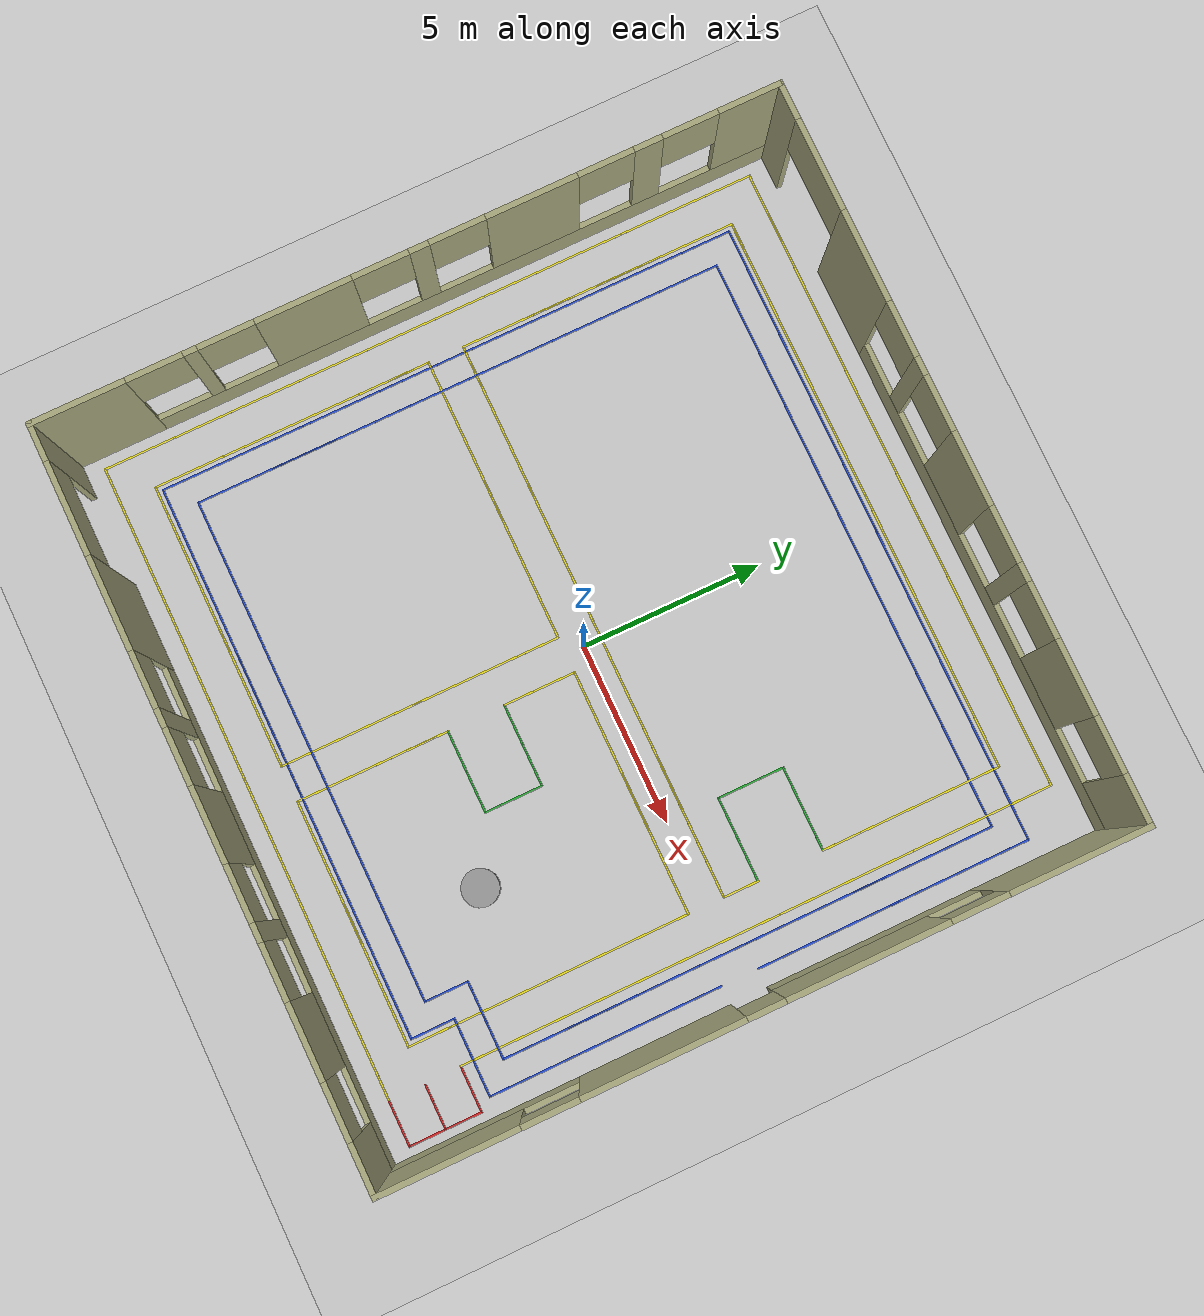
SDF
<sdf version="1.7">
 <world name="default">
  <light name="sun" type="directional">
   <pose>0 0 10 0 -0 0</pose>
   <diffuse>0.8 0.8 0.8 1</diffuse>
   <specular>0.2 0.2 0.2 1</specular>
   <attenuation>
    <range>1000</range>
    <constant>0.9</constant>
    <linear>0.01</linear>
    <quadratic>0.001</quadratic>
   </attenuation>
   <direction>-0.5 0.1 -0.9</direction>
   <spot><inner_angle>0</inner_angle><outer_angle>0</outer_angle><falloff>0</falloff></spot>
  </light>
  <model name="ground_plane">
   <static>1</static>
   <link name="link">
    <collision name="collision">
     <geometry><plane><normal>0 0 1</normal><size>100 100</size></plane></geometry>
     <surface>
      <contact><collide_bitmask>65535</collide_bitmask></contact>
      <friction><ode><mu>100</mu><mu2>50</mu2></ode></friction>
     </surface>
    </collision>
    <visual name="visual">
     <cast_shadows>0</cast_shadows>
     <geometry><plane><normal>0 0 1</normal><size>100 100</size></plane></geometry>
     <material>
      <script><uri>file://media/materials/scripts/gazebo.material</uri><name>Gazebo/Grey</name></script>
     </material>
    </visual>
   </link>
  </model>
  <gravity>0 0 -9.8</gravity>
  <magnetic_field>6e-06 2.3e-05 -4.2e-05</magnetic_field>
  <atmosphere type="adiabatic"/>
  <physics type="ode">
   <max_step_size>0.001</max_step_size>
   <real_time_factor>1</real_time_factor>
   <real_time_update_rate>1000</real_time_update_rate>
  </physics>
  <scene><ambient>0.4 0.4 0.4 1</ambient><background>0.7 0.7 0.7 1</background><shadows>1</shadows></scene>
  <spherical_coordinates>
   <surface_model>EARTH_WGS84</surface_model>
   <latitude_deg>0</latitude_deg>
   <longitude_deg>0</longitude_deg>
   <elevation>0</elevation>
   <heading_deg>0</heading_deg>
  </spherical_coordinates>
  <model name="20x20">
   <link name="Wall_10">
    <pose>0 -9.925 0 0 -0 0</pose>
    <visual name="Wall_10_Visual_0">
     <pose>-9.46251 0 2.5 0 -0 0</pose>
     <geometry><box><size>1.07503 0.15 5</size></box></geometry>
     <material>
      <script><uri>file://media/materials/scripts/gazebo.material</uri><name>Gazebo/Grey</name></script>
      <ambient>0.666667 0.666667 0.498039 1</ambient>
     </material>
    </visual>
    <collision name="Wall_10_Collision_0">
     <geometry><box><size>1.07503 0.15 5</size></box></geometry>
     <pose>-9.46251 0 2.5 0 -0 0</pose>
    </collision>
    <visual name="Wall_10_Visual_1">
     <pose>-5.175 0 2.5 0 -0 0</pose>
     <geometry><box><size>2.5 0.15 5</size></box></geometry>
     <material>
      <script><uri>file://media/materials/scripts/gazebo.material</uri><name>Gazebo/Grey</name></script>
      <ambient>0.666667 0.666667 0.498039 1</ambient>
     </material>
    </visual>
    <collision name="Wall_10_Collision_1">
     <geometry><box><size>2.5 0.15 5</size></box></geometry>
     <pose>-5.175 0 2.5 0 -0 0</pose>
    </collision>
    <visual name="Wall_10_Visual_2">
     <pose>3.03751 0 0.5 0 -0 0</pose>
     <geometry><box><size>13.925 0.15 1</size></box></geometry>
     <material>
      <script><uri>file://media/materials/scripts/gazebo.material</uri><name>Gazebo/Grey</name></script>
      <ambient>0.666667 0.666667 0.498039 1</ambient>
     </material>
    </visual>
    <collision name="Wall_10_Collision_2">
     <geometry><box><size>13.925 0.15 1</size></box></geometry>
     <pose>3.03751 0 0.5 0 -0 0</pose>
    </collision>
    <visual name="Wall_10_Visual_3">
     <pose>-2.175 0 3 0 -0 0</pose>
     <geometry><box><size>0.5 0.15 4</size></box></geometry>
     <material>
      <script><uri>file://media/materials/scripts/gazebo.material</uri><name>Gazebo/Grey</name></script>
      <ambient>0.666667 0.666667 0.498039 1</ambient>
     </material>
    </visual>
    <collision name="Wall_10_Collision_3">
     <geometry><box><size>0.5 0.15 4</size></box></geometry>
     <pose>-2.175 0 3 0 -0 0</pose>
    </collision>
    <visual name="Wall_10_Visual_4">
     <pose>0.575 0 3 0 -0 0</pose>
     <geometry><box><size>2 0.15 4</size></box></geometry>
     <material>
      <script><uri>file://media/materials/scripts/gazebo.material</uri><name>Gazebo/Grey</name></script>
      <ambient>0.666667 0.666667 0.498039 1</ambient>
     </material>
    </visual>
    <collision name="Wall_10_Collision_4">
     <geometry><box><size>2 0.15 4</size></box></geometry>
     <pose>0.575 0 3 0 -0 0</pose>
    </collision>
    <visual name="Wall_10_Visual_5">
     <pose>3.325 0 3 0 -0 0</pose>
     <geometry><box><size>0.5 0.15 4</size></box></geometry>
     <material>
      <script><uri>file://media/materials/scripts/gazebo.material</uri><name>Gazebo/Grey</name></script>
      <ambient>0.666667 0.666667 0.498039 1</ambient>
     </material>
    </visual>
    <collision name="Wall_10_Collision_5">
     <geometry><box><size>0.5 0.15 4</size></box></geometry>
     <pose>3.325 0 3 0 -0 0</pose>
    </collision>
    <visual name="Wall_10_Visual_6">
     <pose>6.075 0 3 0 -0 0</pose>
     <geometry><box><size>2 0.15 4</size></box></geometry>
     <material>
      <script><uri>file://media/materials/scripts/gazebo.material</uri><name>Gazebo/Grey</name></script>
      <ambient>0.666667 0.666667 0.498039 1</ambient>
     </material>
    </visual>
    <collision name="Wall_10_Collision_6">
     <geometry><box><size>2 0.15 4</size></box></geometry>
     <pose>6.075 0 3 0 -0 0</pose>
    </collision>
    <visual name="Wall_10_Visual_7">
     <pose>9.28752 0 3 0 -0 0</pose>
     <geometry><box><size>1.42503 0.15 4</size></box></geometry>
     <material>
      <script><uri>file://media/materials/scripts/gazebo.material</uri><name>Gazebo/Grey</name></script>
      <ambient>0.666667 0.666667 0.498039 1</ambient>
     </material>
    </visual>
    <collision name="Wall_10_Collision_7">
     <geometry><box><size>1.42503 0.15 4</size></box></geometry>
     <pose>9.28752 0 3 0 -0 0</pose>
    </collision>
    <visual name="Wall_10_Visual_8">
     <pose>-7.675 0 4 0 -0 0</pose>
     <geometry><box><size>2.5 0.15 2</size></box></geometry>
     <material>
      <script><uri>file://media/materials/scripts/gazebo.material</uri><name>Gazebo/Grey</name></script>
      <ambient>0.666667 0.666667 0.498039 1</ambient>
     </material>
    </visual>
    <collision name="Wall_10_Collision_8">
     <geometry><box><size>2.5 0.15 2</size></box></geometry>
     <pose>-7.675 0 4 0 -0 0</pose>
    </collision>
    <visual name="Wall_10_Visual_9">
     <pose>-3.175 0 4 0 -0 0</pose>
     <geometry><box><size>1.5 0.15 2</size></box></geometry>
     <material>
      <script><uri>file://media/materials/scripts/gazebo.material</uri><name>Gazebo/Grey</name></script>
      <ambient>0.666667 0.666667 0.498039 1</ambient>
     </material>
    </visual>
    <collision name="Wall_10_Collision_9">
     <geometry><box><size>1.5 0.15 2</size></box></geometry>
     <pose>-3.175 0 4 0 -0 0</pose>
    </collision>
    <visual name="Wall_10_Visual_10">
     <pose>-1.175 0 4 0 -0 0</pose>
     <geometry><box><size>1.5 0.15 2</size></box></geometry>
     <material>
      <script><uri>file://media/materials/scripts/gazebo.material</uri><name>Gazebo/Grey</name></script>
      <ambient>0.666667 0.666667 0.498039 1</ambient>
     </material>
    </visual>
    <collision name="Wall_10_Collision_10">
     <geometry><box><size>1.5 0.15 2</size></box></geometry>
     <pose>-1.175 0 4 0 -0 0</pose>
    </collision>
    <visual name="Wall_10_Visual_11">
     <pose>2.325 0 4 0 -0 0</pose>
     <geometry><box><size>1.5 0.15 2</size></box></geometry>
     <material>
      <script><uri>file://media/materials/scripts/gazebo.material</uri><name>Gazebo/Grey</name></script>
      <ambient>0.666667 0.666667 0.498039 1</ambient>
     </material>
    </visual>
    <collision name="Wall_10_Collision_11">
     <geometry><box><size>1.5 0.15 2</size></box></geometry>
     <pose>2.325 0 4 0 -0 0</pose>
    </collision>
    <visual name="Wall_10_Visual_12">
     <pose>4.325 0 4 0 -0 0</pose>
     <geometry><box><size>1.5 0.15 2</size></box></geometry>
     <material>
      <script><uri>file://media/materials/scripts/gazebo.material</uri><name>Gazebo/Grey</name></script>
      <ambient>0.666667 0.666667 0.498039 1</ambient>
     </material>
    </visual>
    <collision name="Wall_10_Collision_12">
     <geometry><box><size>1.5 0.15 2</size></box></geometry>
     <pose>4.325 0 4 0 -0 0</pose>
    </collision>
    <visual name="Wall_10_Visual_13">
     <pose>7.825 0 4 0 -0 0</pose>
     <geometry><box><size>1.5 0.15 2</size></box></geometry>
     <material>
      <script><uri>file://media/materials/scripts/gazebo.material</uri><name>Gazebo/Grey</name></script>
      <ambient>0.666667 0.666667 0.498039 1</ambient>
     </material>
    </visual>
    <collision name="Wall_10_Collision_13">
     <geometry><box><size>1.5 0.15 2</size></box></geometry>
     <pose>7.825 0 4 0 -0 0</pose>
    </collision>
   </link>
   <link name="Wall_41">
    <pose>9.925 0 0 0 0 -1.5708</pose>
    <visual name="Wall_41_Visual_0">
     <pose>-8.125 0 2.5 0 -0 0</pose>
     <geometry><box><size>3.75 0.15 5</size></box></geometry>
     <material>
      <script><uri>file://media/materials/scripts/gazebo.material</uri><name>Gazebo/Grey</name></script>
      <ambient>0.666667 0.666667 0.498039 1</ambient>
     </material>
    </visual>
    <collision name="Wall_41_Collision_0">
     <geometry><box><size>3.75 0.15 5</size></box></geometry>
     <pose>-8.125 0 2.5 0 -0 0</pose>
    </collision>
    <visual name="Wall_41_Visual_1">
     <pose>2.625 0 2.5 0 -0 0</pose>
     <geometry><box><size>4.25 0.15 5</size></box></geometry>
     <material>
      <script><uri>file://media/materials/scripts/gazebo.material</uri><name>Gazebo/Grey</name></script>
      <ambient>0.666667 0.666667 0.498039 1</ambient>
     </material>
    </visual>
    <collision name="Wall_41_Collision_1">
     <geometry><box><size>4.25 0.15 5</size></box></geometry>
     <pose>2.625 0 2.5 0 -0 0</pose>
    </collision>
    <visual name="Wall_41_Visual_2">
     <pose>-3.375 0 0.75 0 -0 0</pose>
     <geometry><box><size>5.75 0.15 1.5</size></box></geometry>
     <material>
      <script><uri>file://media/materials/scripts/gazebo.material</uri><name>Gazebo/Grey</name></script>
      <ambient>0.666667 0.666667 0.498039 1</ambient>
     </material>
    </visual>
    <collision name="Wall_41_Collision_2">
     <geometry><box><size>5.75 0.15 1.5</size></box></geometry>
     <pose>-3.375 0 0.75 0 -0 0</pose>
    </collision>
    <visual name="Wall_41_Visual_3">
     <pose>7.375 0 0.75 0 -0 0</pose>
     <geometry><box><size>5.25 0.15 1.5</size></box></geometry>
     <material>
      <script><uri>file://media/materials/scripts/gazebo.material</uri><name>Gazebo/Grey</name></script>
      <ambient>0.666667 0.666667 0.498039 1</ambient>
     </material>
    </visual>
    <collision name="Wall_41_Collision_3">
     <geometry><box><size>5.25 0.15 1.5</size></box></geometry>
     <pose>7.375 0 0.75 0 -0 0</pose>
    </collision>
    <visual name="Wall_41_Visual_4">
     <pose>-2.625 0 3.25 0 -0 0</pose>
     <geometry><box><size>4.25 0.15 3.5</size></box></geometry>
     <material>
      <script><uri>file://media/materials/scripts/gazebo.material</uri><name>Gazebo/Grey</name></script>
      <ambient>0.666667 0.666667 0.498039 1</ambient>
     </material>
    </visual>
    <collision name="Wall_41_Collision_4">
     <geometry><box><size>4.25 0.15 3.5</size></box></geometry>
     <pose>-2.625 0 3.25 0 -0 0</pose>
    </collision>
    <visual name="Wall_41_Visual_5">
     <pose>-2.625 0 3.25 0 -0 0</pose>
     <geometry><box><size>4.25 0.15 3.5</size></box></geometry>
     <material>
      <script><uri>file://media/materials/scripts/gazebo.material</uri><name>Gazebo/Grey</name></script>
      <ambient>0.666667 0.666667 0.498039 1</ambient>
     </material>
    </visual>
    <collision name="Wall_41_Collision_5">
     <geometry><box><size>4.25 0.15 3.5</size></box></geometry>
     <pose>-2.625 0 3.25 0 -0 0</pose>
    </collision>
    <visual name="Wall_41_Visual_6">
     <pose>8.125 0 3.25 0 -0 0</pose>
     <geometry><box><size>3.75 0.15 3.5</size></box></geometry>
     <material>
      <script><uri>file://media/materials/scripts/gazebo.material</uri><name>Gazebo/Grey</name></script>
      <ambient>0.666667 0.666667 0.498039 1</ambient>
     </material>
    </visual>
    <collision name="Wall_41_Collision_6">
     <geometry><box><size>3.75 0.15 3.5</size></box></geometry>
     <pose>8.125 0 3.25 0 -0 0</pose>
    </collision>
    <visual name="Wall_41_Visual_7">
     <pose>0 0 3.5 0 -0 0</pose>
     <geometry><box><size>1 0.15 3</size></box></geometry>
     <material>
      <script><uri>file://media/materials/scripts/gazebo.material</uri><name>Gazebo/Grey</name></script>
      <ambient>0.666667 0.666667 0.498039 1</ambient>
     </material>
    </visual>
    <collision name="Wall_41_Collision_7">
     <geometry><box><size>1 0.15 3</size></box></geometry>
     <pose>0 0 3.5 0 -0 0</pose>
    </collision>
    <visual name="Wall_41_Visual_8">
     <pose>0 0 3.5 0 -0 0</pose>
     <geometry><box><size>1 0.15 3</size></box></geometry>
     <material>
      <script><uri>file://media/materials/scripts/gazebo.material</uri><name>Gazebo/Grey</name></script>
      <ambient>0.666667 0.666667 0.498039 1</ambient>
     </material>
    </visual>
    <collision name="Wall_41_Collision_8">
     <geometry><box><size>1 0.15 3</size></box></geometry>
     <pose>0 0 3.5 0 -0 0</pose>
    </collision>
    <visual name="Wall_41_Visual_9">
     <pose>-5.5 0 4.25 0 -0 0</pose>
     <geometry><box><size>1.5 0.15 1.5</size></box></geometry>
     <material>
      <script><uri>file://media/materials/scripts/gazebo.material</uri><name>Gazebo/Grey</name></script>
      <ambient>0.666667 0.666667 0.498039 1</ambient>
     </material>
    </visual>
    <collision name="Wall_41_Collision_9">
     <geometry><box><size>1.5 0.15 1.5</size></box></geometry>
     <pose>-5.5 0 4.25 0 -0 0</pose>
    </collision>
    <visual name="Wall_41_Visual_10">
     <pose>5.5 0 4.25 0 -0 0</pose>
     <geometry><box><size>1.5 0.15 1.5</size></box></geometry>
     <material>
      <script><uri>file://media/materials/scripts/gazebo.material</uri><name>Gazebo/Grey</name></script>
      <ambient>0.666667 0.666667 0.498039 1</ambient>
     </material>
    </visual>
    <collision name="Wall_41_Collision_10">
     <geometry><box><size>1.5 0.15 1.5</size></box></geometry>
     <pose>5.5 0 4.25 0 -0 0</pose>
    </collision>
   </link>
   <link name="Wall_6">
    <pose>-9.925 0 0 0 -0 1.5708</pose>
    <visual name="Wall_6_Visual_0">
     <pose>-8.71763 0 2.5 0 -0 0</pose>
     <geometry><box><size>2.56474 0.15 5</size></box></geometry>
     <material>
      <script><uri>file://media/materials/scripts/gazebo.material</uri><name>Gazebo/Grey</name></script>
      <ambient>0.666667 0.666667 0.498039 1</ambient>
     </material>
    </visual>
    <collision name="Wall_6_Collision_0">
     <geometry><box><size>2.56474 0.15 5</size></box></geometry>
     <pose>-8.71763 0 2.5 0 -0 0</pose>
    </collision>
    <visual name="Wall_6_Visual_1">
     <pose>1.28237 0 0.5 0 -0 0</pose>
     <geometry><box><size>17.4353 0.15 1</size></box></geometry>
     <material>
      <script><uri>file://media/materials/scripts/gazebo.material</uri><name>Gazebo/Grey</name></script>
      <ambient>0.666667 0.666667 0.498039 1</ambient>
     </material>
    </visual>
    <collision name="Wall_6_Collision_1">
     <geometry><box><size>17.4353 0.15 1</size></box></geometry>
     <pose>1.28237 0 0.5 0 -0 0</pose>
    </collision>
    <visual name="Wall_6_Visual_2">
     <pose>-5.74896 0 3 0 -0 0</pose>
     <geometry><box><size>0.372588 0.15 4</size></box></geometry>
     <material>
      <script><uri>file://media/materials/scripts/gazebo.material</uri><name>Gazebo/Grey</name></script>
      <ambient>0.666667 0.666667 0.498039 1</ambient>
     </material>
    </visual>
    <collision name="Wall_6_Collision_2">
     <geometry><box><size>0.372588 0.15 4</size></box></geometry>
     <pose>-5.74896 0 3 0 -0 0</pose>
    </collision>
    <visual name="Wall_6_Visual_3">
     <pose>-2.77957 0 3 0 -0 0</pose>
     <geometry><box><size>2.56619 0.15 4</size></box></geometry>
     <material>
      <script><uri>file://media/materials/scripts/gazebo.material</uri><name>Gazebo/Grey</name></script>
      <ambient>0.666667 0.666667 0.498039 1</ambient>
     </material>
    </visual>
    <collision name="Wall_6_Collision_3">
     <geometry><box><size>2.56619 0.15 4</size></box></geometry>
     <pose>-2.77957 0 3 0 -0 0</pose>
    </collision>
    <visual name="Wall_6_Visual_4">
     <pose>0.270069 0 3 0 -0 0</pose>
     <geometry><box><size>0.533095 0.15 4</size></box></geometry>
     <material>
      <script><uri>file://media/materials/scripts/gazebo.material</uri><name>Gazebo/Grey</name></script>
      <ambient>0.666667 0.666667 0.498039 1</ambient>
     </material>
    </visual>
    <collision name="Wall_6_Collision_4">
     <geometry><box><size>0.533095 0.15 4</size></box></geometry>
     <pose>0.270069 0 3 0 -0 0</pose>
    </collision>
    <visual name="Wall_6_Visual_5">
     <pose>3.26574 0 3 0 -0 0</pose>
     <geometry><box><size>2.45825 0.15 4</size></box></geometry>
     <material>
      <script><uri>file://media/materials/scripts/gazebo.material</uri><name>Gazebo/Grey</name></script>
      <ambient>0.666667 0.666667 0.498039 1</ambient>
     </material>
    </visual>
    <collision name="Wall_6_Collision_5">
     <geometry><box><size>2.45825 0.15 4</size></box></geometry>
     <pose>3.26574 0 3 0 -0 0</pose>
    </collision>
    <visual name="Wall_6_Visual_6">
     <pose>6.37762 0 3 0 -0 0</pose>
     <geometry><box><size>0.765512 0.15 4</size></box></geometry>
     <material>
      <script><uri>file://media/materials/scripts/gazebo.material</uri><name>Gazebo/Grey</name></script>
      <ambient>0.666667 0.666667 0.498039 1</ambient>
     </material>
    </visual>
    <collision name="Wall_6_Collision_6">
     <geometry><box><size>0.765512 0.15 4</size></box></geometry>
     <pose>6.37762 0 3 0 -0 0</pose>
    </collision>
    <visual name="Wall_6_Visual_7">
     <pose>9.13019 0 3 0 -0 0</pose>
     <geometry><box><size>1.73962 0.15 4</size></box></geometry>
     <material>
      <script><uri>file://media/materials/scripts/gazebo.material</uri><name>Gazebo/Grey</name></script>
      <ambient>0.666667 0.666667 0.498039 1</ambient>
     </material>
    </visual>
    <collision name="Wall_6_Collision_7">
     <geometry><box><size>1.73962 0.15 4</size></box></geometry>
     <pose>9.13019 0 3 0 -0 0</pose>
    </collision>
    <visual name="Wall_6_Visual_8">
     <pose>-6.68526 0 4 0 -0 0</pose>
     <geometry><box><size>1.5 0.15 2</size></box></geometry>
     <material>
      <script><uri>file://media/materials/scripts/gazebo.material</uri><name>Gazebo/Grey</name></script>
      <ambient>0.666667 0.666667 0.498039 1</ambient>
     </material>
    </visual>
    <collision name="Wall_6_Collision_8">
     <geometry><box><size>1.5 0.15 2</size></box></geometry>
     <pose>-6.68526 0 4 0 -0 0</pose>
    </collision>
    <visual name="Wall_6_Visual_9">
     <pose>-4.81267 0 4 0 -0 0</pose>
     <geometry><box><size>1.5 0.15 2</size></box></geometry>
     <material>
      <script><uri>file://media/materials/scripts/gazebo.material</uri><name>Gazebo/Grey</name></script>
      <ambient>0.666667 0.666667 0.498039 1</ambient>
     </material>
    </visual>
    <collision name="Wall_6_Collision_9">
     <geometry><box><size>1.5 0.15 2</size></box></geometry>
     <pose>-4.81267 0 4 0 -0 0</pose>
    </collision>
    <visual name="Wall_6_Visual_10">
     <pose>-0.746479 0 4 0 -0 0</pose>
     <geometry><box><size>1.5 0.15 2</size></box></geometry>
     <material>
      <script><uri>file://media/materials/scripts/gazebo.material</uri><name>Gazebo/Grey</name></script>
      <ambient>0.666667 0.666667 0.498039 1</ambient>
     </material>
    </visual>
    <collision name="Wall_6_Collision_10">
     <geometry><box><size>1.5 0.15 2</size></box></geometry>
     <pose>-0.746479 0 4 0 -0 0</pose>
    </collision>
    <visual name="Wall_6_Visual_11">
     <pose>1.28662 0 4 0 -0 0</pose>
     <geometry><box><size>1.5 0.15 2</size></box></geometry>
     <material>
      <script><uri>file://media/materials/scripts/gazebo.material</uri><name>Gazebo/Grey</name></script>
      <ambient>0.666667 0.666667 0.498039 1</ambient>
     </material>
    </visual>
    <collision name="Wall_6_Collision_11">
     <geometry><box><size>1.5 0.15 2</size></box></geometry>
     <pose>1.28662 0 4 0 -0 0</pose>
    </collision>
    <visual name="Wall_6_Visual_12">
     <pose>5.24486 0 4 0 -0 0</pose>
     <geometry><box><size>1.5 0.15 2</size></box></geometry>
     <material>
      <script><uri>file://media/materials/scripts/gazebo.material</uri><name>Gazebo/Grey</name></script>
      <ambient>0.666667 0.666667 0.498039 1</ambient>
     </material>
    </visual>
    <collision name="Wall_6_Collision_12">
     <geometry><box><size>1.5 0.15 2</size></box></geometry>
     <pose>5.24486 0 4 0 -0 0</pose>
    </collision>
    <visual name="Wall_6_Visual_13">
     <pose>7.51038 0 4 0 -0 0</pose>
     <geometry><box><size>1.5 0.15 2</size></box></geometry>
     <material>
      <script><uri>file://media/materials/scripts/gazebo.material</uri><name>Gazebo/Grey</name></script>
      <ambient>0.666667 0.666667 0.498039 1</ambient>
     </material>
    </visual>
    <collision name="Wall_6_Collision_13">
     <geometry><box><size>1.5 0.15 2</size></box></geometry>
     <pose>7.51038 0 4 0 -0 0</pose>
    </collision>
   </link>
   <link name="Wall_7">
    <pose>0 9.925 0 0 -0 0</pose>
    <visual name="Wall_7_Visual_0">
     <pose>-9.4625 0 2.5 0 -0 0</pose>
     <geometry><box><size>1.075 0.15 5</size></box></geometry>
     <material>
      <script><uri>file://media/materials/scripts/gazebo.material</uri><name>Gazebo/Grey</name></script>
      <ambient>0.666667 0.666667 0.498039 1</ambient>
     </material>
    </visual>
    <collision name="Wall_7_Collision_0">
     <geometry><box><size>1.075 0.15 5</size></box></geometry>
     <pose>-9.4625 0 2.5 0 -0 0</pose>
    </collision>
    <visual name="Wall_7_Visual_1">
     <pose>-5.175 0 2.5 0 -0 0</pose>
     <geometry><box><size>2.5 0.15 5</size></box></geometry>
     <material>
      <script><uri>file://media/materials/scripts/gazebo.material</uri><name>Gazebo/Grey</name></script>
      <ambient>0.666667 0.666667 0.498039 1</ambient>
     </material>
    </visual>
    <collision name="Wall_7_Collision_1">
     <geometry><box><size>2.5 0.15 5</size></box></geometry>
     <pose>-5.175 0 2.5 0 -0 0</pose>
    </collision>
    <visual name="Wall_7_Visual_2">
     <pose>3.0375 0 0.5 0 -0 0</pose>
     <geometry><box><size>13.925 0.15 1</size></box></geometry>
     <material>
      <script><uri>file://media/materials/scripts/gazebo.material</uri><name>Gazebo/Grey</name></script>
      <ambient>0.666667 0.666667 0.498039 1</ambient>
     </material>
    </visual>
    <collision name="Wall_7_Collision_2">
     <geometry><box><size>13.925 0.15 1</size></box></geometry>
     <pose>3.0375 0 0.5 0 -0 0</pose>
    </collision>
    <visual name="Wall_7_Visual_3">
     <pose>-2.175 0 3 0 -0 0</pose>
     <geometry><box><size>0.5 0.15 4</size></box></geometry>
     <material>
      <script><uri>file://media/materials/scripts/gazebo.material</uri><name>Gazebo/Grey</name></script>
      <ambient>0.666667 0.666667 0.498039 1</ambient>
     </material>
    </visual>
    <collision name="Wall_7_Collision_3">
     <geometry><box><size>0.5 0.15 4</size></box></geometry>
     <pose>-2.175 0 3 0 -0 0</pose>
    </collision>
    <visual name="Wall_7_Visual_4">
     <pose>0.575 0 3 0 -0 0</pose>
     <geometry><box><size>2 0.15 4</size></box></geometry>
     <material>
      <script><uri>file://media/materials/scripts/gazebo.material</uri><name>Gazebo/Grey</name></script>
      <ambient>0.666667 0.666667 0.498039 1</ambient>
     </material>
    </visual>
    <collision name="Wall_7_Collision_4">
     <geometry><box><size>2 0.15 4</size></box></geometry>
     <pose>0.575 0 3 0 -0 0</pose>
    </collision>
    <visual name="Wall_7_Visual_5">
     <pose>3.325 0 3 0 -0 0</pose>
     <geometry><box><size>0.5 0.15 4</size></box></geometry>
     <material>
      <script><uri>file://media/materials/scripts/gazebo.material</uri><name>Gazebo/Grey</name></script>
      <ambient>0.666667 0.666667 0.498039 1</ambient>
     </material>
    </visual>
    <collision name="Wall_7_Collision_5">
     <geometry><box><size>0.5 0.15 4</size></box></geometry>
     <pose>3.325 0 3 0 -0 0</pose>
    </collision>
    <visual name="Wall_7_Visual_6">
     <pose>6.075 0 3 0 -0 0</pose>
     <geometry><box><size>2 0.15 4</size></box></geometry>
     <material>
      <script><uri>file://media/materials/scripts/gazebo.material</uri><name>Gazebo/Grey</name></script>
      <ambient>0.666667 0.666667 0.498039 1</ambient>
     </material>
    </visual>
    <collision name="Wall_7_Collision_6">
     <geometry><box><size>2 0.15 4</size></box></geometry>
     <pose>6.075 0 3 0 -0 0</pose>
    </collision>
    <visual name="Wall_7_Visual_7">
     <pose>9.2875 0 3 0 -0 0</pose>
     <geometry><box><size>1.425 0.15 4</size></box></geometry>
     <material>
      <script><uri>file://media/materials/scripts/gazebo.material</uri><name>Gazebo/Grey</name></script>
      <ambient>0.666667 0.666667 0.498039 1</ambient>
     </material>
    </visual>
    <collision name="Wall_7_Collision_7">
     <geometry><box><size>1.425 0.15 4</size></box></geometry>
     <pose>9.2875 0 3 0 -0 0</pose>
    </collision>
    <visual name="Wall_7_Visual_8">
     <pose>-7.675 0 4 0 -0 0</pose>
     <geometry><box><size>2.5 0.15 2</size></box></geometry>
     <material>
      <script><uri>file://media/materials/scripts/gazebo.material</uri><name>Gazebo/Grey</name></script>
      <ambient>0.666667 0.666667 0.498039 1</ambient>
     </material>
    </visual>
    <collision name="Wall_7_Collision_8">
     <geometry><box><size>2.5 0.15 2</size></box></geometry>
     <pose>-7.675 0 4 0 -0 0</pose>
    </collision>
    <visual name="Wall_7_Visual_9">
     <pose>-3.175 0 4 0 -0 0</pose>
     <geometry><box><size>1.5 0.15 2</size></box></geometry>
     <material>
      <script><uri>file://media/materials/scripts/gazebo.material</uri><name>Gazebo/Grey</name></script>
      <ambient>0.666667 0.666667 0.498039 1</ambient>
     </material>
    </visual>
    <collision name="Wall_7_Collision_9">
     <geometry><box><size>1.5 0.15 2</size></box></geometry>
     <pose>-3.175 0 4 0 -0 0</pose>
    </collision>
    <visual name="Wall_7_Visual_10">
     <pose>-1.175 0 4 0 -0 0</pose>
     <geometry><box><size>1.5 0.15 2</size></box></geometry>
     <material>
      <script><uri>file://media/materials/scripts/gazebo.material</uri><name>Gazebo/Grey</name></script>
      <ambient>0.666667 0.666667 0.498039 1</ambient>
     </material>
    </visual>
    <collision name="Wall_7_Collision_10">
     <geometry><box><size>1.5 0.15 2</size></box></geometry>
     <pose>-1.175 0 4 0 -0 0</pose>
    </collision>
    <visual name="Wall_7_Visual_11">
     <pose>2.325 0 4 0 -0 0</pose>
     <geometry><box><size>1.5 0.15 2</size></box></geometry>
     <material>
      <script><uri>file://media/materials/scripts/gazebo.material</uri><name>Gazebo/Grey</name></script>
      <ambient>0.666667 0.666667 0.498039 1</ambient>
     </material>
    </visual>
    <collision name="Wall_7_Collision_11">
     <geometry><box><size>1.5 0.15 2</size></box></geometry>
     <pose>2.325 0 4 0 -0 0</pose>
    </collision>
    <visual name="Wall_7_Visual_12">
     <pose>4.325 0 4 0 -0 0</pose>
     <geometry><box><size>1.5 0.15 2</size></box></geometry>
     <material>
      <script><uri>file://media/materials/scripts/gazebo.material</uri><name>Gazebo/Grey</name></script>
      <ambient>0.666667 0.666667 0.498039 1</ambient>
     </material>
    </visual>
    <collision name="Wall_7_Collision_12">
     <geometry><box><size>1.5 0.15 2</size></box></geometry>
     <pose>4.325 0 4 0 -0 0</pose>
    </collision>
    <visual name="Wall_7_Visual_13">
     <pose>7.825 0 4 0 -0 0</pose>
     <geometry><box><size>1.5 0.15 2</size></box></geometry>
     <material>
      <script><uri>file://media/materials/scripts/gazebo.material</uri><name>Gazebo/Grey</name></script>
      <ambient>0.666667 0.666667 0.498039 1</ambient>
     </material>
    </visual>
    <collision name="Wall_7_Collision_13">
     <geometry><box><size>1.5 0.15 2</size></box></geometry>
     <pose>7.825 0 4 0 -0 0</pose>
    </collision>
   </link>
   <static>1</static>
  </model>
  <model name="line9m">
   <link name="link_1">
    <inertial>
     <mass>1</mass>
     <inertia>
      <ixx>0.166667</ixx>
      <ixy>0</ixy>
      <ixz>0</ixz>
      <iyy>0.166667</iyy>
      <iyz>0</iyz>
      <izz>0.166667</izz>
     </inertia>
    </inertial>
    <visual name="visual">
     <geometry><box><size>9 0.05 0.001</size></box></geometry>
     <material>
      <lighting>1</lighting>
      <script><uri>file://media/materials/scripts/gazebo.material</uri><name>Gazebo/Yellow</name></script>
     </material>
    </visual>
    <collision name="collision">
     <geometry><box><size>9 0.05 0.001</size></box></geometry>
     <surface>
      <friction>
       <ode><mu>1</mu><mu2>1</mu2><fdir1>0 0 0</fdir1><slip1>0</slip1><slip2>0</slip2></ode>
       <torsional>
        <coefficient>1</coefficient>
        <patch_radius>0</patch_radius>
        <surface_radius>0</surface_radius>
        <use_patch_radius>1</use_patch_radius>
        <ode><slip>0</slip></ode>
       </torsional>
      </friction>
      <bounce><restitution_coefficient>0</restitution_coefficient><threshold>1e+06</threshold></bounce>
      <contact>
       <collide_without_contact>0</collide_without_contact>
       <collide_without_contact_bitmask>1</collide_without_contact_bitmask>
       <collide_bitmask>1</collide_bitmask>
       <ode>
        <soft_cfm>0</soft_cfm>
        <soft_erp>0.2</soft_erp>
        <kp>1e+13</kp>
        <kd>1</kd>
        <max_vel>0.01</max_vel>
        <min_depth>0</min_depth>
       </ode>
       <bullet>
        <split_impulse>1</split_impulse>
        <split_impulse_penetration_threshold>-0.01</split_impulse_penetration_threshold>
        <soft_cfm>0</soft_cfm>
        <soft_erp>0.2</soft_erp>
        <kp>1e+13</kp>
        <kd>1</kd>
       </bullet>
      </contact>
     </surface>
    </collision>
   </link>
   <static>1</static>
   <pose>3.87 -9.35 0 0 -0 0</pose>
  </model>
  <model name="line9m_0">
   <link name="link_1">
    <inertial>
     <mass>1</mass>
     <inertia>
      <ixx>0.166667</ixx>
      <ixy>0</ixy>
      <ixz>0</ixz>
      <iyy>0.166667</iyy>
      <iyz>0</iyz>
      <izz>0.166667</izz>
     </inertia>
    </inertial>
    <visual name="visual">
     <geometry><box><size>9 0.05 0.001</size></box></geometry>
     <material>
      <lighting>1</lighting>
      <script><uri>file://media/materials/scripts/gazebo.material</uri><name>Gazebo/Yellow</name></script>
     </material>
    </visual>
    <collision name="collision">
     <geometry><box><size>9 0.05 0.001</size></box></geometry>
     <surface>
      <friction>
       <ode><mu>1</mu><mu2>1</mu2><fdir1>0 0 0</fdir1><slip1>0</slip1><slip2>0</slip2></ode>
       <torsional>
        <coefficient>1</coefficient>
        <patch_radius>0</patch_radius>
        <surface_radius>0</surface_radius>
        <use_patch_radius>1</use_patch_radius>
        <ode><slip>0</slip></ode>
       </torsional>
      </friction>
      <bounce><restitution_coefficient>0</restitution_coefficient><threshold>1e+06</threshold></bounce>
      <contact>
       <collide_without_contact>0</collide_without_contact>
       <collide_without_contact_bitmask>1</collide_without_contact_bitmask>
       <collide_bitmask>1</collide_bitmask>
       <ode>
        <soft_cfm>0</soft_cfm>
        <soft_erp>0.2</soft_erp>
        <kp>1e+13</kp>
        <kd>1</kd>
        <max_vel>0.01</max_vel>
        <min_depth>0</min_depth>
       </ode>
       <bullet>
        <split_impulse>1</split_impulse>
        <split_impulse_penetration_threshold>-0.01</split_impulse_penetration_threshold>
        <soft_cfm>0</soft_cfm>
        <soft_erp>0.2</soft_erp>
        <kp>1e+13</kp>
        <kd>1</kd>
       </bullet>
      </contact>
     </surface>
    </collision>
   </link>
   <static>1</static>
   <pose>8.345 -2.875 0 0 0 -1.571</pose>
  </model>
  <model name="oneDemoParking_0">
   <link name="link_1">
    <inertial>
     <mass>1</mass>
     <inertia>
      <ixx>0.166667</ixx>
      <ixy>0</ixy>
      <ixz>0</ixz>
      <iyy>0.166667</iyy>
      <iyz>0</iyz>
      <izz>0.166667</izz>
     </inertia>
    </inertial>
    <visual name="visual">
     <pose>-0.5 0 0 0 -0 0</pose>
     <geometry><box><size>0.05 1.26 0.001</size></box></geometry>
     <material>
      <lighting>1</lighting>
      <script><uri>file://media/materials/scripts/gazebo.material</uri><name>Gazebo/Red</name></script>
      <shader type="pixel"><normal_map>__default__</normal_map></shader>
     </material>
    </visual>
    <visual name="ModelPreview_3::link_1::visual_3">
     <pose>0 0.605 0 0 -0 0</pose>
     <geometry><box><size>1.05 0.05 0.001</size></box></geometry>
     <material>
      <lighting>1</lighting>
      <script><uri>file://media/materials/scripts/gazebo.material</uri><name>Gazebo/Red</name></script>
      <shader type="pixel"><normal_map>__default__</normal_map></shader>
     </material>
    </visual>
    <visual name="ModelPreview_3::link_1::visual_2">
     <pose>0.5 0 0 0 -0 0</pose>
     <geometry><box><size>0.05 1.26 0.001</size></box></geometry>
     <material>
      <lighting>1</lighting>
      <script><uri>file://media/materials/scripts/gazebo.material</uri><name>Gazebo/Red</name></script>
      <shader type="pixel"><normal_map>__default__</normal_map></shader>
     </material>
    </visual>
    <collision name="collision">
     <pose>-0.5 0 0 0 -0 0</pose>
     <geometry><box><size>0.05 1.26 0.001</size></box></geometry>
     <surface>
      <friction>
       <ode><mu>1</mu><mu2>1</mu2><fdir1>0 0 0</fdir1><slip1>0</slip1><slip2>0</slip2></ode>
       <torsional>
        <coefficient>1</coefficient>
        <patch_radius>0</patch_radius>
        <surface_radius>0</surface_radius>
        <use_patch_radius>1</use_patch_radius>
        <ode><slip>0</slip></ode>
       </torsional>
      </friction>
      <bounce><restitution_coefficient>0</restitution_coefficient><threshold>1e+06</threshold></bounce>
      <contact>
       <collide_without_contact>0</collide_without_contact>
       <collide_without_contact_bitmask>1</collide_without_contact_bitmask>
       <collide_bitmask>1</collide_bitmask>
       <ode>
        <soft_cfm>0</soft_cfm>
        <soft_erp>0.2</soft_erp>
        <kp>1e+13</kp>
        <kd>1</kd>
        <max_vel>0.01</max_vel>
        <min_depth>0</min_depth>
       </ode>
       <bullet>
        <split_impulse>1</split_impulse>
        <split_impulse_penetration_threshold>-0.01</split_impulse_penetration_threshold>
        <soft_cfm>0</soft_cfm>
        <soft_erp>0.2</soft_erp>
        <kp>1e+13</kp>
        <kd>1</kd>
       </bullet>
      </contact>
     </surface>
    </collision>
    <collision name="collision_1">
     <pose>0.5 0 0 0 -0 0</pose>
     <geometry><box><size>0.05 1.26 0.001</size></box></geometry>
     <surface>
      <friction>
       <ode><mu>1</mu><mu2>1</mu2><fdir1>0 0 0</fdir1><slip1>0</slip1><slip2>0</slip2></ode>
       <torsional>
        <coefficient>1</coefficient>
        <patch_radius>0</patch_radius>
        <surface_radius>0</surface_radius>
        <use_patch_radius>1</use_patch_radius>
        <ode><slip>0</slip></ode>
       </torsional>
      </friction>
      <bounce><restitution_coefficient>0</restitution_coefficient><threshold>1e+06</threshold></bounce>
      <contact>
       <collide_without_contact>0</collide_without_contact>
       <collide_without_contact_bitmask>1</collide_without_contact_bitmask>
       <collide_bitmask>1</collide_bitmask>
       <ode>
        <soft_cfm>0</soft_cfm>
        <soft_erp>0.2</soft_erp>
        <kp>1e+13</kp>
        <kd>1</kd>
        <max_vel>0.01</max_vel>
        <min_depth>0</min_depth>
       </ode>
       <bullet>
        <split_impulse>1</split_impulse>
        <split_impulse_penetration_threshold>-0.01</split_impulse_penetration_threshold>
        <soft_cfm>0</soft_cfm>
        <soft_erp>0.2</soft_erp>
        <kp>1e+13</kp>
        <kd>1</kd>
       </bullet>
      </contact>
     </surface>
    </collision>
    <collision name="collision_2">
     <pose>0 0.605 0 0 -0 0</pose>
     <geometry><box><size>1.05 0.05 0.001</size></box></geometry>
     <surface>
      <friction>
       <ode><mu>1</mu><mu2>1</mu2><fdir1>0 0 0</fdir1><slip1>0</slip1><slip2>0</slip2></ode>
       <torsional>
        <coefficient>1</coefficient>
        <patch_radius>0</patch_radius>
        <surface_radius>0</surface_radius>
        <use_patch_radius>1</use_patch_radius>
        <ode><slip>0</slip></ode>
       </torsional>
      </friction>
      <bounce><restitution_coefficient>0</restitution_coefficient><threshold>1e+06</threshold></bounce>
      <contact>
       <collide_without_contact>0</collide_without_contact>
       <collide_without_contact_bitmask>1</collide_without_contact_bitmask>
       <collide_bitmask>1</collide_bitmask>
       <ode>
        <soft_cfm>0</soft_cfm>
        <soft_erp>0.2</soft_erp>
        <kp>1e+13</kp>
        <kd>1</kd>
        <max_vel>0.01</max_vel>
        <min_depth>0</min_depth>
       </ode>
       <bullet>
        <split_impulse>1</split_impulse>
        <split_impulse_penetration_threshold>-0.01</split_impulse_penetration_threshold>
        <soft_cfm>0</soft_cfm>
        <soft_erp>0.2</soft_erp>
        <kp>1e+13</kp>
        <kd>1</kd>
       </bullet>
      </contact>
     </surface>
    </collision>
    <collision name="collision_3">
     <pose>-0 -0.4 0 0 -0 0</pose>
     <geometry><cylinder><radius>0.2</radius><length>0.001</length></cylinder></geometry>
     <surface>
      <friction>
       <ode><mu>1</mu><mu2>1</mu2><fdir1>0 0 0</fdir1><slip1>0</slip1><slip2>0</slip2></ode>
       <torsional>
        <coefficient>1</coefficient>
        <patch_radius>0</patch_radius>
        <surface_radius>0</surface_radius>
        <use_patch_radius>1</use_patch_radius>
        <ode><slip>0</slip></ode>
       </torsional>
      </friction>
      <bounce><restitution_coefficient>0</restitution_coefficient><threshold>1e+06</threshold></bounce>
      <contact>
       <collide_without_contact>0</collide_without_contact>
       <collide_without_contact_bitmask>1</collide_without_contact_bitmask>
       <collide_bitmask>1</collide_bitmask>
       <ode>
        <soft_cfm>0</soft_cfm>
        <soft_erp>0.2</soft_erp>
        <kp>1e+13</kp>
        <kd>1</kd>
        <max_vel>0.01</max_vel>
        <min_depth>0</min_depth>
       </ode>
       <bullet>
        <split_impulse>1</split_impulse>
        <split_impulse_penetration_threshold>-0.01</split_impulse_penetration_threshold>
        <soft_cfm>0</soft_cfm>
        <soft_erp>0.2</soft_erp>
        <kp>1e+13</kp>
        <kd>1</kd>
       </bullet>
      </contact>
     </surface>
    </collision>
   </link>
   <static>1</static>
   <pose>9 -8.85 0 0 0 -1.571</pose>
  </model>
  <light name="user_point_light_0" type="point">
   <pose>0.558767 -1.48936 1 0 -0 0</pose>
   <diffuse>0.5 0.5 0.5 1</diffuse>
   <specular>0.1 0.1 0.1 1</specular>
   <attenuation>
    <range>20</range>
    <constant>1</constant>
    <linear>0.02</linear>
    <quadratic>0.02</quadratic>
   </attenuation>
   <cast_shadows>0</cast_shadows>
   <direction>0 0 -1</direction>
   <spot><inner_angle>0</inner_angle><outer_angle>0</outer_angle><falloff>0</falloff></spot>
  </light>
  <model name="oneDemoParking">
   <link name="link_1">
    <inertial>
     <mass>1</mass>
     <inertia>
      <ixx>0.166667</ixx>
      <ixy>0</ixy>
      <ixz>0</ixz>
      <iyy>0.166667</iyy>
      <iyz>0</iyz>
      <izz>0.166667</izz>
     </inertia>
    </inertial>
    <visual name="visual">
     <pose>-0.5 0 0 0 -0 0</pose>
     <geometry><box><size>0.05 1.26 0.001</size></box></geometry>
     <material>
      <lighting>1</lighting>
      <script><uri>file://media/materials/scripts/gazebo.material</uri><name>Gazebo/Red</name></script>
      <shader type="pixel"><normal_map>__default__</normal_map></shader>
     </material>
    </visual>
    <visual name="ModelPreview_3::link_1::visual_3">
     <pose>0 0.605 0 0 -0 0</pose>
     <geometry><box><size>1.05 0.05 0.001</size></box></geometry>
     <material>
      <lighting>1</lighting>
      <script><uri>file://media/materials/scripts/gazebo.material</uri><name>Gazebo/Red</name></script>
      <shader type="pixel"><normal_map>__default__</normal_map></shader>
     </material>
    </visual>
    <visual name="ModelPreview_3::link_1::visual_2">
     <pose>0.5 0 0 0 -0 0</pose>
     <geometry><box><size>0.05 1.26 0.001</size></box></geometry>
     <material>
      <lighting>1</lighting>
      <script><uri>file://media/materials/scripts/gazebo.material</uri><name>Gazebo/Red</name></script>
      <shader type="pixel"><normal_map>__default__</normal_map></shader>
     </material>
    </visual>
    <collision name="collision">
     <pose>-0.5 0 0 0 -0 0</pose>
     <geometry><box><size>0.05 1.26 0.001</size></box></geometry>
     <surface>
      <friction>
       <ode><mu>1</mu><mu2>1</mu2><fdir1>0 0 0</fdir1><slip1>0</slip1><slip2>0</slip2></ode>
       <torsional>
        <coefficient>1</coefficient>
        <patch_radius>0</patch_radius>
        <surface_radius>0</surface_radius>
        <use_patch_radius>1</use_patch_radius>
        <ode><slip>0</slip></ode>
       </torsional>
      </friction>
      <bounce><restitution_coefficient>0</restitution_coefficient><threshold>1e+06</threshold></bounce>
      <contact>
       <collide_without_contact>0</collide_without_contact>
       <collide_without_contact_bitmask>1</collide_without_contact_bitmask>
       <collide_bitmask>1</collide_bitmask>
       <ode>
        <soft_cfm>0</soft_cfm>
        <soft_erp>0.2</soft_erp>
        <kp>1e+13</kp>
        <kd>1</kd>
        <max_vel>0.01</max_vel>
        <min_depth>0</min_depth>
       </ode>
       <bullet>
        <split_impulse>1</split_impulse>
        <split_impulse_penetration_threshold>-0.01</split_impulse_penetration_threshold>
        <soft_cfm>0</soft_cfm>
        <soft_erp>0.2</soft_erp>
        <kp>1e+13</kp>
        <kd>1</kd>
       </bullet>
      </contact>
     </surface>
    </collision>
    <collision name="collision_1">
     <pose>0.5 0 0 0 -0 0</pose>
     <geometry><box><size>0.05 1.26 0.001</size></box></geometry>
     <surface>
      <friction>
       <ode><mu>1</mu><mu2>1</mu2><fdir1>0 0 0</fdir1><slip1>0</slip1><slip2>0</slip2></ode>
       <torsional>
        <coefficient>1</coefficient>
        <patch_radius>0</patch_radius>
        <surface_radius>0</surface_radius>
        <use_patch_radius>1</use_patch_radius>
        <ode><slip>0</slip></ode>
       </torsional>
      </friction>
      <bounce><restitution_coefficient>0</restitution_coefficient><threshold>1e+06</threshold></bounce>
      <contact>
       <collide_without_contact>0</collide_without_contact>
       <collide_without_contact_bitmask>1</collide_without_contact_bitmask>
       <collide_bitmask>1</collide_bitmask>
       <ode>
        <soft_cfm>0</soft_cfm>
        <soft_erp>0.2</soft_erp>
        <kp>1e+13</kp>
        <kd>1</kd>
        <max_vel>0.01</max_vel>
        <min_depth>0</min_depth>
       </ode>
       <bullet>
        <split_impulse>1</split_impulse>
        <split_impulse_penetration_threshold>-0.01</split_impulse_penetration_threshold>
        <soft_cfm>0</soft_cfm>
        <soft_erp>0.2</soft_erp>
        <kp>1e+13</kp>
        <kd>1</kd>
       </bullet>
      </contact>
     </surface>
    </collision>
    <collision name="collision_2">
     <pose>0 0.605 0 0 -0 0</pose>
     <geometry><box><size>1.05 0.05 0.001</size></box></geometry>
     <surface>
      <friction>
       <ode><mu>1</mu><mu2>1</mu2><fdir1>0 0 0</fdir1><slip1>0</slip1><slip2>0</slip2></ode>
       <torsional>
        <coefficient>1</coefficient>
        <patch_radius>0</patch_radius>
        <surface_radius>0</surface_radius>
        <use_patch_radius>1</use_patch_radius>
        <ode><slip>0</slip></ode>
       </torsional>
      </friction>
      <bounce><restitution_coefficient>0</restitution_coefficient><threshold>1e+06</threshold></bounce>
      <contact>
       <collide_without_contact>0</collide_without_contact>
       <collide_without_contact_bitmask>1</collide_without_contact_bitmask>
       <collide_bitmask>1</collide_bitmask>
       <ode>
        <soft_cfm>0</soft_cfm>
        <soft_erp>0.2</soft_erp>
        <kp>1e+13</kp>
        <kd>1</kd>
        <max_vel>0.01</max_vel>
        <min_depth>0</min_depth>
       </ode>
       <bullet>
        <split_impulse>1</split_impulse>
        <split_impulse_penetration_threshold>-0.01</split_impulse_penetration_threshold>
        <soft_cfm>0</soft_cfm>
        <soft_erp>0.2</soft_erp>
        <kp>1e+13</kp>
        <kd>1</kd>
       </bullet>
      </contact>
     </surface>
    </collision>
    <collision name="collision_3">
     <pose>-0 -0.4 0 0 -0 0</pose>
     <geometry><cylinder><radius>0.2</radius><length>0.001</length></cylinder></geometry>
     <surface>
      <friction>
       <ode><mu>1</mu><mu2>1</mu2><fdir1>0 0 0</fdir1><slip1>0</slip1><slip2>0</slip2></ode>
       <torsional>
        <coefficient>1</coefficient>
        <patch_radius>0</patch_radius>
        <surface_radius>0</surface_radius>
        <use_patch_radius>1</use_patch_radius>
        <ode><slip>0</slip></ode>
       </torsional>
      </friction>
      <bounce><restitution_coefficient>0</restitution_coefficient><threshold>1e+06</threshold></bounce>
      <contact>
       <collide_without_contact>0</collide_without_contact>
       <collide_without_contact_bitmask>1</collide_without_contact_bitmask>
       <collide_bitmask>1</collide_bitmask>
       <ode>
        <soft_cfm>0</soft_cfm>
        <soft_erp>0.2</soft_erp>
        <kp>1e+13</kp>
        <kd>1</kd>
        <max_vel>0.01</max_vel>
        <min_depth>0</min_depth>
       </ode>
       <bullet>
        <split_impulse>1</split_impulse>
        <split_impulse_penetration_threshold>-0.01</split_impulse_penetration_threshold>
        <soft_cfm>0</soft_cfm>
        <soft_erp>0.2</soft_erp>
        <kp>1e+13</kp>
        <kd>1</kd>
       </bullet>
      </contact>
     </surface>
    </collision>
   </link>
   <static>1</static>
   <pose>9 -7.85 0 0 0 -1.571</pose>
  </model>
  <model name="line4m">
   <link name="link_3">
    <inertial>
     <mass>1</mass>
     <inertia>
      <ixx>0.166667</ixx>
      <ixy>0</ixy>
      <ixz>0</ixz>
      <iyy>0.166667</iyy>
      <iyz>0</iyz>
      <izz>0.166667</izz>
     </inertia>
    </inertial>
    <visual name="visual">
     <geometry><box><size>0.05 4 0.001</size></box></geometry>
     <material>
      <lighting>1</lighting>
      <script><uri>file://media/materials/scripts/gazebo.material</uri><name>Gazebo/Yellow</name></script>
     </material>
    </visual>
    <collision name="collision">
     <geometry><box><size>0.05 4 1e-06</size></box></geometry>
     <surface>
      <friction>
       <ode><mu>1</mu><mu2>1</mu2><fdir1>0 0 0</fdir1><slip1>0</slip1><slip2>0</slip2></ode>
       <torsional>
        <coefficient>1</coefficient>
        <patch_radius>0</patch_radius>
        <surface_radius>0</surface_radius>
        <use_patch_radius>1</use_patch_radius>
        <ode><slip>0</slip></ode>
       </torsional>
      </friction>
      <bounce><restitution_coefficient>0</restitution_coefficient><threshold>1e+06</threshold></bounce>
      <contact>
       <collide_without_contact>0</collide_without_contact>
       <collide_without_contact_bitmask>1</collide_without_contact_bitmask>
       <collide_bitmask>1</collide_bitmask>
       <ode>
        <soft_cfm>0</soft_cfm>
        <soft_erp>0.2</soft_erp>
        <kp>1e+13</kp>
        <kd>1</kd>
        <max_vel>0.01</max_vel>
        <min_depth>0</min_depth>
       </ode>
       <bullet>
        <split_impulse>1</split_impulse>
        <split_impulse_penetration_threshold>-0.01</split_impulse_penetration_threshold>
        <soft_cfm>0</soft_cfm>
        <soft_erp>0.2</soft_erp>
        <kp>1e+13</kp>
        <kd>1</kd>
       </bullet>
      </contact>
     </surface>
    </collision>
   </link>
   <static>1</static>
   <pose>8.345 7.37225 0 0 -0 0</pose>
  </model>
  <model name="line9m_1">
   <link name="link_1">
    <inertial>
     <mass>1</mass>
     <inertia>
      <ixx>0.166667</ixx>
      <ixy>0</ixy>
      <ixz>0</ixz>
      <iyy>0.166667</iyy>
      <iyz>0</iyz>
      <izz>0.166667</izz>
     </inertia>
    </inertial>
    <visual name="visual">
     <geometry><box><size>9 0.05 0.001</size></box></geometry>
     <material>
      <lighting>1</lighting>
      <script><uri>file://media/materials/scripts/gazebo.material</uri><name>Gazebo/Yellow</name></script>
     </material>
    </visual>
    <collision name="collision">
     <geometry><box><size>9 0.05 0.001</size></box></geometry>
     <surface>
      <friction>
       <ode><mu>1</mu><mu2>1</mu2><fdir1>0 0 0</fdir1><slip1>0</slip1><slip2>0</slip2></ode>
       <torsional>
        <coefficient>1</coefficient>
        <patch_radius>0</patch_radius>
        <surface_radius>0</surface_radius>
        <use_patch_radius>1</use_patch_radius>
        <ode><slip>0</slip></ode>
       </torsional>
      </friction>
      <bounce><restitution_coefficient>0</restitution_coefficient><threshold>1e+06</threshold></bounce>
      <contact>
       <collide_without_contact>0</collide_without_contact>
       <collide_without_contact_bitmask>1</collide_without_contact_bitmask>
       <collide_bitmask>1</collide_bitmask>
       <ode>
        <soft_cfm>0</soft_cfm>
        <soft_erp>0.2</soft_erp>
        <kp>1e+13</kp>
        <kd>1</kd>
        <max_vel>0.01</max_vel>
        <min_depth>0</min_depth>
       </ode>
       <bullet>
        <split_impulse>1</split_impulse>
        <split_impulse_penetration_threshold>-0.01</split_impulse_penetration_threshold>
        <soft_cfm>0</soft_cfm>
        <soft_erp>0.2</soft_erp>
        <kp>1e+13</kp>
        <kd>1</kd>
       </bullet>
      </contact>
     </surface>
    </collision>
   </link>
   <static>1</static>
   <pose>3.87 9.35 0 0 -0 0</pose>
  </model>
  <model name="line4m_clone">
   <link name="link_3">
    <inertial>
     <mass>1</mass>
     <inertia>
      <ixx>0.166667</ixx>
      <ixy>0</ixy>
      <ixz>0</ixz>
      <iyy>0.166667</iyy>
      <iyz>0</iyz>
      <izz>0.166667</izz>
     </inertia>
    </inertial>
    <visual name="visual">
     <geometry><box><size>0.05 4 0.001</size></box></geometry>
     <material>
      <lighting>1</lighting>
      <script><uri>file://media/materials/scripts/gazebo.material</uri><name>Gazebo/Yellow</name></script>
     </material>
    </visual>
    <collision name="collision">
     <geometry><box><size>0.05 4 1e-06</size></box></geometry>
     <surface>
      <friction>
       <ode><mu>1</mu><mu2>1</mu2><fdir1>0 0 0</fdir1><slip1>0</slip1><slip2>0</slip2></ode>
       <torsional>
        <coefficient>1</coefficient>
        <patch_radius>0</patch_radius>
        <surface_radius>0</surface_radius>
        <use_patch_radius>1</use_patch_radius>
        <ode><slip>0</slip></ode>
       </torsional>
      </friction>
      <bounce><restitution_coefficient>0</restitution_coefficient><threshold>1e+06</threshold></bounce>
      <contact>
       <collide_without_contact>0</collide_without_contact>
       <collide_without_contact_bitmask>1</collide_without_contact_bitmask>
       <collide_bitmask>1</collide_bitmask>
       <ode>
        <soft_cfm>0</soft_cfm>
        <soft_erp>0.2</soft_erp>
        <kp>1e+13</kp>
        <kd>1</kd>
        <max_vel>0.01</max_vel>
        <min_depth>0</min_depth>
       </ode>
       <bullet>
        <split_impulse>1</split_impulse>
        <split_impulse_penetration_threshold>-0.01</split_impulse_penetration_threshold>
        <soft_cfm>0</soft_cfm>
        <soft_erp>0.2</soft_erp>
        <kp>1e+13</kp>
        <kd>1</kd>
       </bullet>
      </contact>
     </surface>
    </collision>
   </link>
   <static>1</static>
   <pose>8.345 3.39734 0 0 -0 0</pose>
  </model>
  <model name="line120cm">
   <link name="link_1">
    <inertial>
     <mass>1</mass>
     <inertia>
      <ixx>0.166667</ixx>
      <ixy>0</ixy>
      <ixz>0</ixz>
      <iyy>0.166667</iyy>
      <iyz>0</iyz>
      <izz>0.166667</izz>
     </inertia>
    </inertial>
    <visual name="visual">
     <geometry><box><size>1.2 0.05 0.001</size></box></geometry>
     <material>
      <script><uri>file://media/materials/scripts/gazebo.material</uri><name>Gazebo/Yellow</name></script>
     </material>
    </visual>
    <collision name="collision">
     <geometry><box><size>1.2 0.05 1e-05</size></box></geometry>
     <surface>
      <friction>
       <ode><mu>1</mu><mu2>1</mu2><fdir1>0 0 0</fdir1><slip1>0</slip1><slip2>0</slip2></ode>
       <torsional>
        <coefficient>1</coefficient>
        <patch_radius>0</patch_radius>
        <surface_radius>0</surface_radius>
        <use_patch_radius>1</use_patch_radius>
        <ode><slip>0</slip></ode>
       </torsional>
      </friction>
      <bounce><restitution_coefficient>0</restitution_coefficient><threshold>1e+06</threshold></bounce>
      <contact>
       <collide_without_contact>0</collide_without_contact>
       <collide_without_contact_bitmask>1</collide_without_contact_bitmask>
       <collide_bitmask>1</collide_bitmask>
       <ode>
        <soft_cfm>0</soft_cfm>
        <soft_erp>0.2</soft_erp>
        <kp>1e+13</kp>
        <kd>1</kd>
        <max_vel>0.01</max_vel>
        <min_depth>0</min_depth>
       </ode>
       <bullet>
        <split_impulse>1</split_impulse>
        <split_impulse_penetration_threshold>-0.01</split_impulse_penetration_threshold>
        <soft_cfm>0</soft_cfm>
        <soft_erp>0.2</soft_erp>
        <kp>1e+13</kp>
        <kd>1</kd>
       </bullet>
      </contact>
     </surface>
    </collision>
   </link>
   <static>1</static>
   <pose>7.3449 -7.76422 0 0 0 -1.571</pose>
  </model>
  <model name="line9m_4">
   <link name="link_1">
    <inertial>
     <mass>1</mass>
     <inertia>
      <ixx>0.166667</ixx>
      <ixy>0</ixy>
      <ixz>0</ixz>
      <iyy>0.166667</iyy>
      <iyz>0</iyz>
      <izz>0.166667</izz>
     </inertia>
    </inertial>
    <visual name="visual">
     <geometry><box><size>9 0.05 0.001</size></box></geometry>
     <material>
      <lighting>1</lighting>
      <script><uri>file://media/materials/scripts/gazebo.material</uri><name>Gazebo/Yellow</name></script>
     </material>
    </visual>
    <collision name="collision">
     <geometry><box><size>9 0.05 0.001</size></box></geometry>
     <surface>
      <friction>
       <ode><mu>1</mu><mu2>1</mu2><fdir1>0 0 0</fdir1><slip1>0</slip1><slip2>0</slip2></ode>
       <torsional>
        <coefficient>1</coefficient>
        <patch_radius>0</patch_radius>
        <surface_radius>0</surface_radius>
        <use_patch_radius>1</use_patch_radius>
        <ode><slip>0</slip></ode>
       </torsional>
      </friction>
      <bounce><restitution_coefficient>0</restitution_coefficient><threshold>1e+06</threshold></bounce>
      <contact>
       <collide_without_contact>0</collide_without_contact>
       <collide_without_contact_bitmask>1</collide_without_contact_bitmask>
       <collide_bitmask>1</collide_bitmask>
       <ode>
        <soft_cfm>0</soft_cfm>
        <soft_erp>0.2</soft_erp>
        <kp>1e+13</kp>
        <kd>1</kd>
        <max_vel>0.01</max_vel>
        <min_depth>0</min_depth>
       </ode>
       <bullet>
        <split_impulse>1</split_impulse>
        <split_impulse_penetration_threshold>-0.01</split_impulse_penetration_threshold>
        <soft_cfm>0</soft_cfm>
        <soft_erp>0.2</soft_erp>
        <kp>1e+13</kp>
        <kd>1</kd>
       </bullet>
      </contact>
     </surface>
    </collision>
   </link>
   <static>1</static>
   <pose>-5.075 -9.35 0 0 -0 0</pose>
  </model>
  <model name="line2m">
   <link name="link_0">
    <inertial>
     <mass>1</mass>
     <inertia>
      <ixx>0.166667</ixx>
      <ixy>0</ixy>
      <ixz>0</ixz>
      <iyy>0.166667</iyy>
      <iyz>0</iyz>
      <izz>0.166667</izz>
     </inertia>
    </inertial>
    <visual name="visual">
     <geometry><box><size>2 0.05 0.001</size></box></geometry>
     <material>
      <lighting>1</lighting>
      <script><uri>file://media/materials/scripts/gazebo.material</uri><name>Gazebo/Yellow</name></script>
     </material>
    </visual>
    <collision name="collision">
     <geometry><box><size>2 0.05 1e-05</size></box></geometry>
     <surface>
      <friction>
       <ode><mu>1</mu><mu2>1</mu2><fdir1>0 0 0</fdir1><slip1>0</slip1><slip2>0</slip2></ode>
       <torsional>
        <coefficient>1</coefficient>
        <patch_radius>0</patch_radius>
        <surface_radius>0</surface_radius>
        <use_patch_radius>1</use_patch_radius>
        <ode><slip>0</slip></ode>
       </torsional>
      </friction>
      <bounce><restitution_coefficient>0</restitution_coefficient><threshold>1e+06</threshold></bounce>
      <contact>
       <collide_without_contact>0</collide_without_contact>
       <collide_without_contact_bitmask>1</collide_without_contact_bitmask>
       <collide_bitmask>1</collide_bitmask>
       <ode>
        <soft_cfm>0</soft_cfm>
        <soft_erp>0.2</soft_erp>
        <kp>1e+13</kp>
        <kd>1</kd>
        <max_vel>0.01</max_vel>
        <min_depth>0</min_depth>
       </ode>
       <bullet>
        <split_impulse>1</split_impulse>
        <split_impulse_penetration_threshold>-0.01</split_impulse_penetration_threshold>
        <soft_cfm>0</soft_cfm>
        <soft_erp>0.2</soft_erp>
        <kp>1e+13</kp>
        <kd>1</kd>
       </bullet>
      </contact>
     </surface>
    </collision>
   </link>
   <static>1</static>
   <pose>-9.55 -8.345 0 0 -0 1.571</pose>
  </model>
  <model name="line2m_clone">
   <link name="link_0">
    <inertial>
     <mass>1</mass>
     <inertia>
      <ixx>0.166667</ixx>
      <ixy>0</ixy>
      <ixz>0</ixz>
      <iyy>0.166667</iyy>
      <iyz>0</iyz>
      <izz>0.166667</izz>
     </inertia>
    </inertial>
    <visual name="visual">
     <geometry><box><size>2 0.05 0.001</size></box></geometry>
     <material>
      <lighting>1</lighting>
      <script><uri>file://media/materials/scripts/gazebo.material</uri><name>Gazebo/Yellow</name></script>
     </material>
    </visual>
    <collision name="collision">
     <geometry><box><size>2 0.05 1e-05</size></box></geometry>
     <surface>
      <friction>
       <ode><mu>1</mu><mu2>1</mu2><fdir1>0 0 0</fdir1><slip1>0</slip1><slip2>0</slip2></ode>
       <torsional>
        <coefficient>1</coefficient>
        <patch_radius>0</patch_radius>
        <surface_radius>0</surface_radius>
        <use_patch_radius>1</use_patch_radius>
        <ode><slip>0</slip></ode>
       </torsional>
      </friction>
      <bounce><restitution_coefficient>0</restitution_coefficient><threshold>1e+06</threshold></bounce>
      <contact>
       <collide_without_contact>0</collide_without_contact>
       <collide_without_contact_bitmask>1</collide_without_contact_bitmask>
       <collide_bitmask>1</collide_bitmask>
       <ode>
        <soft_cfm>0</soft_cfm>
        <soft_erp>0.2</soft_erp>
        <kp>1e+13</kp>
        <kd>1</kd>
        <max_vel>0.01</max_vel>
        <min_depth>0</min_depth>
       </ode>
       <bullet>
        <split_impulse>1</split_impulse>
        <split_impulse_penetration_threshold>-0.01</split_impulse_penetration_threshold>
        <soft_cfm>0</soft_cfm>
        <soft_erp>0.2</soft_erp>
        <kp>1e+13</kp>
        <kd>1</kd>
       </bullet>
      </contact>
     </surface>
    </collision>
   </link>
   <static>1</static>
   <pose>-8.55 -7.37342 0 0 -0 1.571</pose>
  </model>
  <model name="line9m_6_clone">
   <link name="link_1">
    <inertial>
     <mass>1</mass>
     <inertia>
      <ixx>0.166667</ixx>
      <ixy>0</ixy>
      <ixz>0</ixz>
      <iyy>0.166667</iyy>
      <iyz>0</iyz>
      <izz>0.166667</izz>
     </inertia>
    </inertial>
    <visual name="visual">
     <geometry><box><size>9 0.05 0.001</size></box></geometry>
     <material>
      <lighting>1</lighting>
      <script><uri>file://media/materials/scripts/gazebo.material</uri><name>Gazebo/Yellow</name></script>
     </material>
    </visual>
    <collision name="collision">
     <geometry><box><size>9 0.05 0.001</size></box></geometry>
     <surface>
      <friction>
       <ode><mu>1</mu><mu2>1</mu2><fdir1>0 0 0</fdir1><slip1>0</slip1><slip2>0</slip2></ode>
       <torsional>
        <coefficient>1</coefficient>
        <patch_radius>0</patch_radius>
        <surface_radius>0</surface_radius>
        <use_patch_radius>1</use_patch_radius>
        <ode><slip>0</slip></ode>
       </torsional>
      </friction>
      <bounce><restitution_coefficient>0</restitution_coefficient><threshold>1e+06</threshold></bounce>
      <contact>
       <collide_without_contact>0</collide_without_contact>
       <collide_without_contact_bitmask>1</collide_without_contact_bitmask>
       <collide_bitmask>1</collide_bitmask>
       <ode>
        <soft_cfm>0</soft_cfm>
        <soft_erp>0.2</soft_erp>
        <kp>1e+13</kp>
        <kd>1</kd>
        <max_vel>0.01</max_vel>
        <min_depth>0</min_depth>
       </ode>
       <bullet>
        <split_impulse>1</split_impulse>
        <split_impulse_penetration_threshold>-0.01</split_impulse_penetration_threshold>
        <soft_cfm>0</soft_cfm>
        <soft_erp>0.2</soft_erp>
        <kp>1e+13</kp>
        <kd>1</kd>
       </bullet>
      </contact>
     </surface>
    </collision>
   </link>
   <static>1</static>
   <pose>-9.55 -2.89705 0 0 -0 1.571</pose>
  </model>
  <model name="line9m_7">
   <link name="link_1">
    <inertial>
     <mass>1</mass>
     <inertia>
      <ixx>0.166667</ixx>
      <ixy>0</ixy>
      <ixz>0</ixz>
      <iyy>0.166667</iyy>
      <iyz>0</iyz>
      <izz>0.166667</izz>
     </inertia>
    </inertial>
    <visual name="visual">
     <geometry><box><size>9 0.05 0.001</size></box></geometry>
     <material>
      <lighting>1</lighting>
      <script><uri>file://media/materials/scripts/gazebo.material</uri><name>Gazebo/Yellow</name></script>
     </material>
    </visual>
    <collision name="collision">
     <geometry><box><size>9 0.05 0.001</size></box></geometry>
     <surface>
      <friction>
       <ode><mu>1</mu><mu2>1</mu2><fdir1>0 0 0</fdir1><slip1>0</slip1><slip2>0</slip2></ode>
       <torsional>
        <coefficient>1</coefficient>
        <patch_radius>0</patch_radius>
        <surface_radius>0</surface_radius>
        <use_patch_radius>1</use_patch_radius>
        <ode><slip>0</slip></ode>
       </torsional>
      </friction>
      <bounce><restitution_coefficient>0</restitution_coefficient><threshold>1e+06</threshold></bounce>
      <contact>
       <collide_without_contact>0</collide_without_contact>
       <collide_without_contact_bitmask>1</collide_without_contact_bitmask>
       <collide_bitmask>1</collide_bitmask>
       <ode>
        <soft_cfm>0</soft_cfm>
        <soft_erp>0.2</soft_erp>
        <kp>1e+13</kp>
        <kd>1</kd>
        <max_vel>0.01</max_vel>
        <min_depth>0</min_depth>
       </ode>
       <bullet>
        <split_impulse>1</split_impulse>
        <split_impulse_penetration_threshold>-0.01</split_impulse_penetration_threshold>
        <soft_cfm>0</soft_cfm>
        <soft_erp>0.2</soft_erp>
        <kp>1e+13</kp>
        <kd>1</kd>
       </bullet>
      </contact>
     </surface>
    </collision>
   </link>
   <static>1</static>
   <pose>-3.87 9.35 0 0 -0 0</pose>
  </model>
  <model name="line4m_0">
   <link name="link_3">
    <inertial>
     <mass>1</mass>
     <inertia>
      <ixx>0.166667</ixx>
      <ixy>0</ixy>
      <ixz>0</ixz>
      <iyy>0.166667</iyy>
      <iyz>0</iyz>
      <izz>0.166667</izz>
     </inertia>
    </inertial>
    <visual name="visual">
     <geometry><box><size>0.05 4 0.001</size></box></geometry>
     <material>
      <lighting>1</lighting>
      <script><uri>file://media/materials/scripts/gazebo.material</uri><name>Gazebo/Yellow</name></script>
     </material>
    </visual>
    <collision name="collision">
     <geometry><box><size>0.05 4 1e-06</size></box></geometry>
     <surface>
      <friction>
       <ode><mu>1</mu><mu2>1</mu2><fdir1>0 0 0</fdir1><slip1>0</slip1><slip2>0</slip2></ode>
       <torsional>
        <coefficient>1</coefficient>
        <patch_radius>0</patch_radius>
        <surface_radius>0</surface_radius>
        <use_patch_radius>1</use_patch_radius>
        <ode><slip>0</slip></ode>
       </torsional>
      </friction>
      <bounce><restitution_coefficient>0</restitution_coefficient><threshold>1e+06</threshold></bounce>
      <contact>
       <collide_without_contact>0</collide_without_contact>
       <collide_without_contact_bitmask>1</collide_without_contact_bitmask>
       <collide_bitmask>1</collide_bitmask>
       <ode>
        <soft_cfm>0</soft_cfm>
        <soft_erp>0.2</soft_erp>
        <kp>1e+13</kp>
        <kd>1</kd>
        <max_vel>0.01</max_vel>
        <min_depth>0</min_depth>
       </ode>
       <bullet>
        <split_impulse>1</split_impulse>
        <split_impulse_penetration_threshold>-0.01</split_impulse_penetration_threshold>
        <soft_cfm>0</soft_cfm>
        <soft_erp>0.2</soft_erp>
        <kp>1e+13</kp>
        <kd>1</kd>
       </bullet>
      </contact>
     </surface>
    </collision>
   </link>
   <static>1</static>
   <pose>-8.55 4.28851 0 0 -0 0</pose>
  </model>
  <model name="line4m_1">
   <link name="link_3">
    <inertial>
     <mass>1</mass>
     <inertia>
      <ixx>0.166667</ixx>
      <ixy>0</ixy>
      <ixz>0</ixz>
      <iyy>0.166667</iyy>
      <iyz>0</iyz>
      <izz>0.166667</izz>
     </inertia>
    </inertial>
    <visual name="visual">
     <geometry><box><size>0.05 4 0.001</size></box></geometry>
     <material>
      <lighting>1</lighting>
      <script><uri>file://media/materials/scripts/gazebo.material</uri><name>Gazebo/Yellow</name></script>
     </material>
    </visual>
    <collision name="collision">
     <geometry><box><size>0.05 4 1e-06</size></box></geometry>
     <surface>
      <friction>
       <ode><mu>1</mu><mu2>1</mu2><fdir1>0 0 0</fdir1><slip1>0</slip1><slip2>0</slip2></ode>
       <torsional>
        <coefficient>1</coefficient>
        <patch_radius>0</patch_radius>
        <surface_radius>0</surface_radius>
        <use_patch_radius>1</use_patch_radius>
        <ode><slip>0</slip></ode>
       </torsional>
      </friction>
      <bounce><restitution_coefficient>0</restitution_coefficient><threshold>1e+06</threshold></bounce>
      <contact>
       <collide_without_contact>0</collide_without_contact>
       <collide_without_contact_bitmask>1</collide_without_contact_bitmask>
       <collide_bitmask>1</collide_bitmask>
       <ode>
        <soft_cfm>0</soft_cfm>
        <soft_erp>0.2</soft_erp>
        <kp>1e+13</kp>
        <kd>1</kd>
        <max_vel>0.01</max_vel>
        <min_depth>0</min_depth>
       </ode>
       <bullet>
        <split_impulse>1</split_impulse>
        <split_impulse_penetration_threshold>-0.01</split_impulse_penetration_threshold>
        <soft_cfm>0</soft_cfm>
        <soft_erp>0.2</soft_erp>
        <kp>1e+13</kp>
        <kd>1</kd>
       </bullet>
      </contact>
     </surface>
    </collision>
   </link>
   <static>1</static>
   <pose>-9.55 3.56802 0 0 -0 0</pose>
  </model>
  <model name="line4m_2">
   <link name="link_3">
    <inertial>
     <mass>1</mass>
     <inertia>
      <ixx>0.166667</ixx>
      <ixy>0</ixy>
      <ixz>0</ixz>
      <iyy>0.166667</iyy>
      <iyz>0</iyz>
      <izz>0.166667</izz>
     </inertia>
    </inertial>
    <visual name="visual">
     <geometry><box><size>0.05 4 0.001</size></box></geometry>
     <material>
      <lighting>1</lighting>
      <script><uri>file://media/materials/scripts/gazebo.material</uri><name>Gazebo/Yellow</name></script>
     </material>
    </visual>
    <collision name="collision">
     <geometry><box><size>0.05 4 1e-06</size></box></geometry>
     <surface>
      <friction>
       <ode><mu>1</mu><mu2>1</mu2><fdir1>0 0 0</fdir1><slip1>0</slip1><slip2>0</slip2></ode>
       <torsional>
        <coefficient>1</coefficient>
        <patch_radius>0</patch_radius>
        <surface_radius>0</surface_radius>
        <use_patch_radius>1</use_patch_radius>
        <ode><slip>0</slip></ode>
       </torsional>
      </friction>
      <bounce><restitution_coefficient>0</restitution_coefficient><threshold>1e+06</threshold></bounce>
      <contact>
       <collide_without_contact>0</collide_without_contact>
       <collide_without_contact_bitmask>1</collide_without_contact_bitmask>
       <collide_bitmask>1</collide_bitmask>
       <ode>
        <soft_cfm>0</soft_cfm>
        <soft_erp>0.2</soft_erp>
        <kp>1e+13</kp>
        <kd>1</kd>
        <max_vel>0.01</max_vel>
        <min_depth>0</min_depth>
       </ode>
       <bullet>
        <split_impulse>1</split_impulse>
        <split_impulse_penetration_threshold>-0.01</split_impulse_penetration_threshold>
        <soft_cfm>0</soft_cfm>
        <soft_erp>0.2</soft_erp>
        <kp>1e+13</kp>
        <kd>1</kd>
       </bullet>
      </contact>
     </surface>
    </collision>
   </link>
   <static>1</static>
   <pose>-9.55 7.37 0 0 -0 0</pose>
  </model>
  <model name="line4m_3">
   <link name="link_3">
    <inertial>
     <mass>1</mass>
     <inertia>
      <ixx>0.166667</ixx>
      <ixy>0</ixy>
      <ixz>0</ixz>
      <iyy>0.166667</iyy>
      <iyz>0</iyz>
      <izz>0.166667</izz>
     </inertia>
    </inertial>
    <visual name="visual">
     <geometry><box><size>0.05 4 0.001</size></box></geometry>
     <material>
      <lighting>1</lighting>
      <script><uri>file://media/materials/scripts/gazebo.material</uri><name>Gazebo/Yellow</name></script>
     </material>
    </visual>
    <collision name="collision">
     <geometry><box><size>0.05 4 1e-06</size></box></geometry>
     <surface>
      <friction>
       <ode><mu>1</mu><mu2>1</mu2><fdir1>0 0 0</fdir1><slip1>0</slip1><slip2>0</slip2></ode>
       <torsional>
        <coefficient>1</coefficient>
        <patch_radius>0</patch_radius>
        <surface_radius>0</surface_radius>
        <use_patch_radius>1</use_patch_radius>
        <ode><slip>0</slip></ode>
       </torsional>
      </friction>
      <bounce><restitution_coefficient>0</restitution_coefficient><threshold>1e+06</threshold></bounce>
      <contact>
       <collide_without_contact>0</collide_without_contact>
       <collide_without_contact_bitmask>1</collide_without_contact_bitmask>
       <collide_bitmask>1</collide_bitmask>
       <ode>
        <soft_cfm>0</soft_cfm>
        <soft_erp>0.2</soft_erp>
        <kp>1e+13</kp>
        <kd>1</kd>
        <max_vel>0.01</max_vel>
        <min_depth>0</min_depth>
       </ode>
       <bullet>
        <split_impulse>1</split_impulse>
        <split_impulse_penetration_threshold>-0.01</split_impulse_penetration_threshold>
        <soft_cfm>0</soft_cfm>
        <soft_erp>0.2</soft_erp>
        <kp>1e+13</kp>
        <kd>1</kd>
       </bullet>
      </contact>
     </surface>
    </collision>
   </link>
   <static>1</static>
   <pose>-8.55 6.375 0 0 -0 0</pose>
  </model>
  <model name="line2m_0">
   <link name="link_0">
    <inertial>
     <mass>1</mass>
     <inertia>
      <ixx>0.166667</ixx>
      <ixy>0</ixy>
      <ixz>0</ixz>
      <iyy>0.166667</iyy>
      <iyz>0</iyz>
      <izz>0.166667</izz>
     </inertia>
    </inertial>
    <visual name="visual">
     <geometry><box><size>2 0.05 0.001</size></box></geometry>
     <material>
      <lighting>1</lighting>
      <script><uri>file://media/materials/scripts/gazebo.material</uri><name>Gazebo/Yellow</name></script>
     </material>
    </visual>
    <collision name="collision">
     <geometry><box><size>2 0.05 1e-05</size></box></geometry>
     <surface>
      <friction>
       <ode><mu>1</mu><mu2>1</mu2><fdir1>0 0 0</fdir1><slip1>0</slip1><slip2>0</slip2></ode>
       <torsional>
        <coefficient>1</coefficient>
        <patch_radius>0</patch_radius>
        <surface_radius>0</surface_radius>
        <use_patch_radius>1</use_patch_radius>
        <ode><slip>0</slip></ode>
       </torsional>
      </friction>
      <bounce><restitution_coefficient>0</restitution_coefficient><threshold>1e+06</threshold></bounce>
      <contact>
       <collide_without_contact>0</collide_without_contact>
       <collide_without_contact_bitmask>1</collide_without_contact_bitmask>
       <collide_bitmask>1</collide_bitmask>
       <ode>
        <soft_cfm>0</soft_cfm>
        <soft_erp>0.2</soft_erp>
        <kp>1e+13</kp>
        <kd>1</kd>
        <max_vel>0.01</max_vel>
        <min_depth>0</min_depth>
       </ode>
       <bullet>
        <split_impulse>1</split_impulse>
        <split_impulse_penetration_threshold>-0.01</split_impulse_penetration_threshold>
        <soft_cfm>0</soft_cfm>
        <soft_erp>0.2</soft_erp>
        <kp>1e+13</kp>
        <kd>1</kd>
       </bullet>
      </contact>
     </surface>
    </collision>
   </link>
   <static>1</static>
   <pose>-8.575 9.35 0 0 -0 0</pose>
  </model>
  <model name="line4m_4">
   <link name="link_3">
    <inertial>
     <mass>1</mass>
     <inertia>
      <ixx>0.166667</ixx>
      <ixy>0</ixy>
      <ixz>0</ixz>
      <iyy>0.166667</iyy>
      <iyz>0</iyz>
      <izz>0.166667</izz>
     </inertia>
    </inertial>
    <visual name="visual">
     <geometry><box><size>0.05 4 0.001</size></box></geometry>
     <material>
      <lighting>1</lighting>
      <script><uri>file://media/materials/scripts/gazebo.material</uri><name>Gazebo/Blue</name></script>
     </material>
    </visual>
    <collision name="collision">
     <geometry><box><size>0.05 4 1e-06</size></box></geometry>
     <surface>
      <friction>
       <ode><mu>1</mu><mu2>1</mu2><fdir1>0 0 0</fdir1><slip1>0</slip1><slip2>0</slip2></ode>
       <torsional>
        <coefficient>1</coefficient>
        <patch_radius>0</patch_radius>
        <surface_radius>0</surface_radius>
        <use_patch_radius>1</use_patch_radius>
        <ode><slip>0</slip></ode>
       </torsional>
      </friction>
      <bounce><restitution_coefficient>0</restitution_coefficient><threshold>1e+06</threshold></bounce>
      <contact>
       <collide_without_contact>0</collide_without_contact>
       <collide_without_contact_bitmask>1</collide_without_contact_bitmask>
       <collide_bitmask>1</collide_bitmask>
       <ode>
        <soft_cfm>0</soft_cfm>
        <soft_erp>0.2</soft_erp>
        <kp>1e+13</kp>
        <kd>1</kd>
        <max_vel>0.01</max_vel>
        <min_depth>0</min_depth>
       </ode>
       <bullet>
        <split_impulse>1</split_impulse>
        <split_impulse_penetration_threshold>-0.01</split_impulse_penetration_threshold>
        <soft_cfm>0</soft_cfm>
        <soft_erp>0.2</soft_erp>
        <kp>1e+13</kp>
        <kd>1</kd>
       </bullet>
      </contact>
     </surface>
    </collision>
   </link>
   <static>1</static>
   <pose>9.345 2.5 0 0 -0 0</pose>
  </model>
  <model name="line4m_4_clone">
   <link name="link_3">
    <inertial>
     <mass>1</mass>
     <inertia>
      <ixx>0.166667</ixx>
      <ixy>0</ixy>
      <ixz>0</ixz>
      <iyy>0.166667</iyy>
      <iyz>0</iyz>
      <izz>0.166667</izz>
     </inertia>
    </inertial>
    <visual name="visual">
     <geometry><box><size>0.05 4 0.001</size></box></geometry>
     <material>
      <lighting>1</lighting>
      <script><uri>file://media/materials/scripts/gazebo.material</uri><name>Gazebo/Blue</name></script>
     </material>
    </visual>
    <collision name="collision">
     <geometry><box><size>0.05 4 1e-06</size></box></geometry>
     <surface>
      <friction>
       <ode><mu>1</mu><mu2>1</mu2><fdir1>0 0 0</fdir1><slip1>0</slip1><slip2>0</slip2></ode>
       <torsional>
        <coefficient>1</coefficient>
        <patch_radius>0</patch_radius>
        <surface_radius>0</surface_radius>
        <use_patch_radius>1</use_patch_radius>
        <ode><slip>0</slip></ode>
       </torsional>
      </friction>
      <bounce><restitution_coefficient>0</restitution_coefficient><threshold>1e+06</threshold></bounce>
      <contact>
       <collide_without_contact>0</collide_without_contact>
       <collide_without_contact_bitmask>1</collide_without_contact_bitmask>
       <collide_bitmask>1</collide_bitmask>
       <ode>
        <soft_cfm>0</soft_cfm>
        <soft_erp>0.2</soft_erp>
        <kp>1e+13</kp>
        <kd>1</kd>
        <max_vel>0.01</max_vel>
        <min_depth>0</min_depth>
       </ode>
       <bullet>
        <split_impulse>1</split_impulse>
        <split_impulse_penetration_threshold>-0.01</split_impulse_penetration_threshold>
        <soft_cfm>0</soft_cfm>
        <soft_erp>0.2</soft_erp>
        <kp>1e+13</kp>
        <kd>1</kd>
       </bullet>
      </contact>
     </surface>
    </collision>
   </link>
   <static>1</static>
   <pose>9.345 6.225 0 0 -0 0</pose>
  </model>
  <model name="line9m_11">
   <link name="link_1">
    <inertial>
     <mass>1</mass>
     <inertia>
      <ixx>0.166667</ixx>
      <ixy>0</ixy>
      <ixz>0</ixz>
      <iyy>0.166667</iyy>
      <iyz>0</iyz>
      <izz>0.166667</izz>
     </inertia>
    </inertial>
    <visual name="visual">
     <geometry><box><size>9 0.05 0.001</size></box></geometry>
     <material>
      <lighting>1</lighting>
      <script><uri>file://media/materials/scripts/gazebo.material</uri><name>Gazebo/Blue</name></script>
     </material>
    </visual>
    <collision name="collision">
     <geometry><box><size>9 0.05 0.001</size></box></geometry>
     <surface>
      <friction>
       <ode><mu>1</mu><mu2>1</mu2><fdir1>0 0 0</fdir1><slip1>0</slip1><slip2>0</slip2></ode>
       <torsional>
        <coefficient>1</coefficient>
        <patch_radius>0</patch_radius>
        <surface_radius>0</surface_radius>
        <use_patch_radius>1</use_patch_radius>
        <ode><slip>0</slip></ode>
       </torsional>
      </friction>
      <bounce><restitution_coefficient>0</restitution_coefficient><threshold>1e+06</threshold></bounce>
      <contact>
       <collide_without_contact>0</collide_without_contact>
       <collide_without_contact_bitmask>1</collide_without_contact_bitmask>
       <collide_bitmask>1</collide_bitmask>
       <ode>
        <soft_cfm>0</soft_cfm>
        <soft_erp>0.2</soft_erp>
        <kp>1e+13</kp>
        <kd>1</kd>
        <max_vel>0.01</max_vel>
        <min_depth>0</min_depth>
       </ode>
       <bullet>
        <split_impulse>1</split_impulse>
        <split_impulse_penetration_threshold>-0.01</split_impulse_penetration_threshold>
        <soft_cfm>0</soft_cfm>
        <soft_erp>0.2</soft_erp>
        <kp>1e+13</kp>
        <kd>1</kd>
       </bullet>
      </contact>
     </surface>
    </collision>
   </link>
   <static>1</static>
   <pose>4.867 8.2 0 0 -0 0</pose>
  </model>
  <model name="line9m_11_clone">
   <link name="link_1">
    <inertial>
     <mass>1</mass>
     <inertia>
      <ixx>0.166667</ixx>
      <ixy>0</ixy>
      <ixz>0</ixz>
      <iyy>0.166667</iyy>
      <iyz>0</iyz>
      <izz>0.166667</izz>
     </inertia>
    </inertial>
    <visual name="visual">
     <geometry><box><size>9 0.05 0.001</size></box></geometry>
     <material>
      <lighting>1</lighting>
      <script><uri>file://media/materials/scripts/gazebo.material</uri><name>Gazebo/Blue</name></script>
     </material>
    </visual>
    <collision name="collision">
     <geometry><box><size>9 0.05 0.001</size></box></geometry>
     <surface>
      <friction>
       <ode><mu>1</mu><mu2>1</mu2><fdir1>0 0 0</fdir1><slip1>0</slip1><slip2>0</slip2></ode>
       <torsional>
        <coefficient>1</coefficient>
        <patch_radius>0</patch_radius>
        <surface_radius>0</surface_radius>
        <use_patch_radius>1</use_patch_radius>
        <ode><slip>0</slip></ode>
       </torsional>
      </friction>
      <bounce><restitution_coefficient>0</restitution_coefficient><threshold>1e+06</threshold></bounce>
      <contact>
       <collide_without_contact>0</collide_without_contact>
       <collide_without_contact_bitmask>1</collide_without_contact_bitmask>
       <collide_bitmask>1</collide_bitmask>
       <ode>
        <soft_cfm>0</soft_cfm>
        <soft_erp>0.2</soft_erp>
        <kp>1e+13</kp>
        <kd>1</kd>
        <max_vel>0.01</max_vel>
        <min_depth>0</min_depth>
       </ode>
       <bullet>
        <split_impulse>1</split_impulse>
        <split_impulse_penetration_threshold>-0.01</split_impulse_penetration_threshold>
        <soft_cfm>0</soft_cfm>
        <soft_erp>0.2</soft_erp>
        <kp>1e+13</kp>
        <kd>1</kd>
       </bullet>
      </contact>
     </surface>
    </collision>
   </link>
   <static>1</static>
   <pose>-3.92317 8.2 0 0 -0 0</pose>
  </model>
  <model name="line160cm">
   <link name="link_1">
    <inertial>
     <mass>1</mass>
     <inertia>
      <ixx>0.166667</ixx>
      <ixy>0</ixy>
      <ixz>0</ixz>
      <iyy>0.166667</iyy>
      <iyz>0</iyz>
      <izz>0.166667</izz>
     </inertia>
    </inertial>
    <visual name="visual">
     <geometry><box><size>1.6 0.05 0.001</size></box></geometry>
     <material>
      <script><uri>file://media/materials/scripts/gazebo.material</uri><name>Gazebo/Blue</name></script>
     </material>
    </visual>
    <collision name="collision">
     <geometry><box><size>1.6 0.05 1e-05</size></box></geometry>
     <surface>
      <friction>
       <ode><mu>1</mu><mu2>1</mu2><fdir1>0 0 0</fdir1><slip1>0</slip1><slip2>0</slip2></ode>
       <torsional>
        <coefficient>1</coefficient>
        <patch_radius>0</patch_radius>
        <surface_radius>0</surface_radius>
        <use_patch_radius>1</use_patch_radius>
        <ode><slip>0</slip></ode>
       </torsional>
      </friction>
      <bounce><restitution_coefficient>0</restitution_coefficient><threshold>1e+06</threshold></bounce>
      <contact>
       <collide_without_contact>0</collide_without_contact>
       <collide_without_contact_bitmask>1</collide_without_contact_bitmask>
       <collide_bitmask>1</collide_bitmask>
       <ode>
        <soft_cfm>0</soft_cfm>
        <soft_erp>0.2</soft_erp>
        <kp>1e+13</kp>
        <kd>1</kd>
        <max_vel>0.01</max_vel>
        <min_depth>0</min_depth>
       </ode>
       <bullet>
        <split_impulse>1</split_impulse>
        <split_impulse_penetration_threshold>-0.01</split_impulse_penetration_threshold>
        <soft_cfm>0</soft_cfm>
        <soft_erp>0.2</soft_erp>
        <kp>1e+13</kp>
        <kd>1</kd>
       </bullet>
      </contact>
     </surface>
    </collision>
   </link>
   <static>1</static>
   <pose>-8.4 7.4248 0 0 -0 1.571</pose>
  </model>
  <model name="line9m_12">
   <link name="link_1">
    <inertial>
     <mass>1</mass>
     <inertia>
      <ixx>0.166667</ixx>
      <ixy>0</ixy>
      <ixz>0</ixz>
      <iyy>0.166667</iyy>
      <iyz>0</iyz>
      <izz>0.166667</izz>
     </inertia>
    </inertial>
    <visual name="visual">
     <geometry><box><size>9 0.05 0.001</size></box></geometry>
     <material>
      <lighting>1</lighting>
      <script><uri>file://media/materials/scripts/gazebo.material</uri><name>Gazebo/Blue</name></script>
     </material>
    </visual>
    <collision name="collision">
     <geometry><box><size>9 0.05 0.001</size></box></geometry>
     <surface>
      <friction>
       <ode><mu>1</mu><mu2>1</mu2><fdir1>0 0 0</fdir1><slip1>0</slip1><slip2>0</slip2></ode>
       <torsional>
        <coefficient>1</coefficient>
        <patch_radius>0</patch_radius>
        <surface_radius>0</surface_radius>
        <use_patch_radius>1</use_patch_radius>
        <ode><slip>0</slip></ode>
       </torsional>
      </friction>
      <bounce><restitution_coefficient>0</restitution_coefficient><threshold>1e+06</threshold></bounce>
      <contact>
       <collide_without_contact>0</collide_without_contact>
       <collide_without_contact_bitmask>1</collide_without_contact_bitmask>
       <collide_bitmask>1</collide_bitmask>
       <ode>
        <soft_cfm>0</soft_cfm>
        <soft_erp>0.2</soft_erp>
        <kp>1e+13</kp>
        <kd>1</kd>
        <max_vel>0.01</max_vel>
        <min_depth>0</min_depth>
       </ode>
       <bullet>
        <split_impulse>1</split_impulse>
        <split_impulse_penetration_threshold>-0.01</split_impulse_penetration_threshold>
        <soft_cfm>0</soft_cfm>
        <soft_erp>0.2</soft_erp>
        <kp>1e+13</kp>
        <kd>1</kd>
       </bullet>
      </contact>
     </surface>
    </collision>
   </link>
   <static>1</static>
   <pose>-3.2268 7.5 0 0 -0 0</pose>
  </model>
  <model name="line9m_13">
   <link name="link_1">
    <inertial>
     <mass>1</mass>
     <inertia>
      <ixx>0.166667</ixx>
      <ixy>0</ixy>
      <ixz>0</ixz>
      <iyy>0.166667</iyy>
      <iyz>0</iyz>
      <izz>0.166667</izz>
     </inertia>
    </inertial>
    <visual name="visual">
     <geometry><box><size>9 0.05 0.001</size></box></geometry>
     <material>
      <lighting>1</lighting>
      <script><uri>file://media/materials/scripts/gazebo.material</uri><name>Gazebo/Blue</name></script>
     </material>
    </visual>
    <collision name="collision">
     <geometry><box><size>9 0.05 0.001</size></box></geometry>
     <surface>
      <friction>
       <ode><mu>1</mu><mu2>1</mu2><fdir1>0 0 0</fdir1><slip1>0</slip1><slip2>0</slip2></ode>
       <torsional>
        <coefficient>1</coefficient>
        <patch_radius>0</patch_radius>
        <surface_radius>0</surface_radius>
        <use_patch_radius>1</use_patch_radius>
        <ode><slip>0</slip></ode>
       </torsional>
      </friction>
      <bounce><restitution_coefficient>0</restitution_coefficient><threshold>1e+06</threshold></bounce>
      <contact>
       <collide_without_contact>0</collide_without_contact>
       <collide_without_contact_bitmask>1</collide_without_contact_bitmask>
       <collide_bitmask>1</collide_bitmask>
       <ode>
        <soft_cfm>0</soft_cfm>
        <soft_erp>0.2</soft_erp>
        <kp>1e+13</kp>
        <kd>1</kd>
        <max_vel>0.01</max_vel>
        <min_depth>0</min_depth>
       </ode>
       <bullet>
        <split_impulse>1</split_impulse>
        <split_impulse_penetration_threshold>-0.01</split_impulse_penetration_threshold>
        <soft_cfm>0</soft_cfm>
        <soft_erp>0.2</soft_erp>
        <kp>1e+13</kp>
        <kd>1</kd>
       </bullet>
      </contact>
     </surface>
    </collision>
   </link>
   <static>1</static>
   <pose>-7.7 3.025 0 0 -0 1.571</pose>
  </model>
  <model name="line9m_14">
   <link name="link_1">
    <inertial>
     <mass>1</mass>
     <inertia>
      <ixx>0.166667</ixx>
      <ixy>0</ixy>
      <ixz>0</ixz>
      <iyy>0.166667</iyy>
      <iyz>0</iyz>
      <izz>0.166667</izz>
     </inertia>
    </inertial>
    <visual name="visual">
     <geometry><box><size>9 0.05 0.001</size></box></geometry>
     <material>
      <lighting>1</lighting>
      <script><uri>file://media/materials/scripts/gazebo.material</uri><name>Gazebo/Blue</name></script>
     </material>
    </visual>
    <collision name="collision">
     <geometry><box><size>9 0.05 0.001</size></box></geometry>
     <surface>
      <friction>
       <ode><mu>1</mu><mu2>1</mu2><fdir1>0 0 0</fdir1><slip1>0</slip1><slip2>0</slip2></ode>
       <torsional>
        <coefficient>1</coefficient>
        <patch_radius>0</patch_radius>
        <surface_radius>0</surface_radius>
        <use_patch_radius>1</use_patch_radius>
        <ode><slip>0</slip></ode>
       </torsional>
      </friction>
      <bounce><restitution_coefficient>0</restitution_coefficient><threshold>1e+06</threshold></bounce>
      <contact>
       <collide_without_contact>0</collide_without_contact>
       <collide_without_contact_bitmask>1</collide_without_contact_bitmask>
       <collide_bitmask>1</collide_bitmask>
       <ode>
        <soft_cfm>0</soft_cfm>
        <soft_erp>0.2</soft_erp>
        <kp>1e+13</kp>
        <kd>1</kd>
        <max_vel>0.01</max_vel>
        <min_depth>0</min_depth>
       </ode>
       <bullet>
        <split_impulse>1</split_impulse>
        <split_impulse_penetration_threshold>-0.01</split_impulse_penetration_threshold>
        <soft_cfm>0</soft_cfm>
        <soft_erp>0.2</soft_erp>
        <kp>1e+13</kp>
        <kd>1</kd>
       </bullet>
      </contact>
     </surface>
    </collision>
   </link>
   <static>1</static>
   <pose>4.16033 7.5 0 0 -0 0</pose>
  </model>
  <model name="line4m_5">
   <link name="link_3">
    <inertial>
     <mass>1</mass>
     <inertia>
      <ixx>0.166667</ixx>
      <ixy>0</ixy>
      <ixz>0</ixz>
      <iyy>0.166667</iyy>
      <iyz>0</iyz>
      <izz>0.166667</izz>
     </inertia>
    </inertial>
    <visual name="visual">
     <geometry><box><size>0.05 4 0.001</size></box></geometry>
     <material>
      <lighting>1</lighting>
      <script><uri>file://media/materials/scripts/gazebo.material</uri><name>Gazebo/Blue</name></script>
     </material>
    </visual>
    <collision name="collision">
     <geometry><box><size>0.05 4 1e-06</size></box></geometry>
     <surface>
      <friction>
       <ode><mu>1</mu><mu2>1</mu2><fdir1>0 0 0</fdir1><slip1>0</slip1><slip2>0</slip2></ode>
       <torsional>
        <coefficient>1</coefficient>
        <patch_radius>0</patch_radius>
        <surface_radius>0</surface_radius>
        <use_patch_radius>1</use_patch_radius>
        <ode><slip>0</slip></ode>
       </torsional>
      </friction>
      <bounce><restitution_coefficient>0</restitution_coefficient><threshold>1e+06</threshold></bounce>
      <contact>
       <collide_without_contact>0</collide_without_contact>
       <collide_without_contact_bitmask>1</collide_without_contact_bitmask>
       <collide_bitmask>1</collide_bitmask>
       <ode>
        <soft_cfm>0</soft_cfm>
        <soft_erp>0.2</soft_erp>
        <kp>1e+13</kp>
        <kd>1</kd>
        <max_vel>0.01</max_vel>
        <min_depth>0</min_depth>
       </ode>
       <bullet>
        <split_impulse>1</split_impulse>
        <split_impulse_penetration_threshold>-0.01</split_impulse_penetration_threshold>
        <soft_cfm>0</soft_cfm>
        <soft_erp>0.2</soft_erp>
        <kp>1e+13</kp>
        <kd>1</kd>
       </bullet>
      </contact>
     </surface>
    </collision>
   </link>
   <static>1</static>
   <pose>8.645 5.52339 0 0 -0 0</pose>
  </model>
  <model name="line9m_15">
   <link name="link_1">
    <inertial>
     <mass>1</mass>
     <inertia>
      <ixx>0.166667</ixx>
      <ixy>0</ixy>
      <ixz>0</ixz>
      <iyy>0.166667</iyy>
      <iyz>0</iyz>
      <izz>0.166667</izz>
     </inertia>
    </inertial>
    <visual name="visual">
     <geometry><box><size>9 0.05 0.001</size></box></geometry>
     <material>
      <lighting>1</lighting>
      <script><uri>file://media/materials/scripts/gazebo.material</uri><name>Gazebo/Blue</name></script>
     </material>
    </visual>
    <collision name="collision">
     <geometry><box><size>9 0.05 0.001</size></box></geometry>
     <surface>
      <friction>
       <ode><mu>1</mu><mu2>1</mu2><fdir1>0 0 0</fdir1><slip1>0</slip1><slip2>0</slip2></ode>
       <torsional>
        <coefficient>1</coefficient>
        <patch_radius>0</patch_radius>
        <surface_radius>0</surface_radius>
        <use_patch_radius>1</use_patch_radius>
        <ode><slip>0</slip></ode>
       </torsional>
      </friction>
      <bounce><restitution_coefficient>0</restitution_coefficient><threshold>1e+06</threshold></bounce>
      <contact>
       <collide_without_contact>0</collide_without_contact>
       <collide_without_contact_bitmask>1</collide_without_contact_bitmask>
       <collide_bitmask>1</collide_bitmask>
       <ode>
        <soft_cfm>0</soft_cfm>
        <soft_erp>0.2</soft_erp>
        <kp>1e+13</kp>
        <kd>1</kd>
        <max_vel>0.01</max_vel>
        <min_depth>0</min_depth>
       </ode>
       <bullet>
        <split_impulse>1</split_impulse>
        <split_impulse_penetration_threshold>-0.01</split_impulse_penetration_threshold>
        <soft_cfm>0</soft_cfm>
        <soft_erp>0.2</soft_erp>
        <kp>1e+13</kp>
        <kd>1</kd>
       </bullet>
      </contact>
     </surface>
    </collision>
   </link>
   <static>1</static>
   <pose>-8.40007 2.31121 0 0 -0 1.571</pose>
  </model>
  <model name="line4m_6">
   <link name="link_3">
    <inertial>
     <mass>1</mass>
     <inertia>
      <ixx>0.166667</ixx>
      <ixy>0</ixy>
      <ixz>0</ixz>
      <iyy>0.166667</iyy>
      <iyz>0</iyz>
      <izz>0.166667</izz>
     </inertia>
    </inertial>
    <visual name="visual">
     <geometry><box><size>0.05 4 0.001</size></box></geometry>
     <material>
      <lighting>1</lighting>
      <script><uri>file://media/materials/scripts/gazebo.material</uri><name>Gazebo/Blue</name></script>
     </material>
    </visual>
    <collision name="collision">
     <geometry><box><size>0.05 4 1e-06</size></box></geometry>
     <surface>
      <friction>
       <ode><mu>1</mu><mu2>1</mu2><fdir1>0 0 0</fdir1><slip1>0</slip1><slip2>0</slip2></ode>
       <torsional>
        <coefficient>1</coefficient>
        <patch_radius>0</patch_radius>
        <surface_radius>0</surface_radius>
        <use_patch_radius>1</use_patch_radius>
        <ode><slip>0</slip></ode>
       </torsional>
      </friction>
      <bounce><restitution_coefficient>0</restitution_coefficient><threshold>1e+06</threshold></bounce>
      <contact>
       <collide_without_contact>0</collide_without_contact>
       <collide_without_contact_bitmask>1</collide_without_contact_bitmask>
       <collide_bitmask>1</collide_bitmask>
       <ode>
        <soft_cfm>0</soft_cfm>
        <soft_erp>0.2</soft_erp>
        <kp>1e+13</kp>
        <kd>1</kd>
        <max_vel>0.01</max_vel>
        <min_depth>0</min_depth>
       </ode>
       <bullet>
        <split_impulse>1</split_impulse>
        <split_impulse_penetration_threshold>-0.01</split_impulse_penetration_threshold>
        <soft_cfm>0</soft_cfm>
        <soft_erp>0.2</soft_erp>
        <kp>1e+13</kp>
        <kd>1</kd>
       </bullet>
      </contact>
     </surface>
    </collision>
   </link>
   <static>1</static>
   <pose>-8.4 -3.97754 0 0 -0 0</pose>
  </model>
  <model name="line4m_6_clone">
   <link name="link_3">
    <inertial>
     <mass>1</mass>
     <inertia>
      <ixx>0.166667</ixx>
      <ixy>0</ixy>
      <ixz>0</ixz>
      <iyy>0.166667</iyy>
      <iyz>0</iyz>
      <izz>0.166667</izz>
     </inertia>
    </inertial>
    <visual name="visual">
     <geometry><box><size>0.05 4 0.001</size></box></geometry>
     <material>
      <lighting>1</lighting>
      <script><uri>file://media/materials/scripts/gazebo.material</uri><name>Gazebo/Blue</name></script>
     </material>
    </visual>
    <collision name="collision">
     <geometry><box><size>0.05 4 1e-06</size></box></geometry>
     <surface>
      <friction>
       <ode><mu>1</mu><mu2>1</mu2><fdir1>0 0 0</fdir1><slip1>0</slip1><slip2>0</slip2></ode>
       <torsional>
        <coefficient>1</coefficient>
        <patch_radius>0</patch_radius>
        <surface_radius>0</surface_radius>
        <use_patch_radius>1</use_patch_radius>
        <ode><slip>0</slip></ode>
       </torsional>
      </friction>
      <bounce><restitution_coefficient>0</restitution_coefficient><threshold>1e+06</threshold></bounce>
      <contact>
       <collide_without_contact>0</collide_without_contact>
       <collide_without_contact_bitmask>1</collide_without_contact_bitmask>
       <collide_bitmask>1</collide_bitmask>
       <ode>
        <soft_cfm>0</soft_cfm>
        <soft_erp>0.2</soft_erp>
        <kp>1e+13</kp>
        <kd>1</kd>
        <max_vel>0.01</max_vel>
        <min_depth>0</min_depth>
       </ode>
       <bullet>
        <split_impulse>1</split_impulse>
        <split_impulse_penetration_threshold>-0.01</split_impulse_penetration_threshold>
        <soft_cfm>0</soft_cfm>
        <soft_erp>0.2</soft_erp>
        <kp>1e+13</kp>
        <kd>1</kd>
       </bullet>
      </contact>
     </surface>
    </collision>
   </link>
   <static>1</static>
   <pose>-7.7 -3.37475 0 0 -0 0</pose>
  </model>
  <model name="line4m_4_clone_0">
   <link name="link_3">
    <inertial>
     <mass>1</mass>
     <inertia>
      <ixx>0.166667</ixx>
      <ixy>0</ixy>
      <ixz>0</ixz>
      <iyy>0.166667</iyy>
      <iyz>0</iyz>
      <izz>0.166667</izz>
     </inertia>
    </inertial>
    <visual name="visual">
     <geometry><box><size>0.05 4 0.001</size></box></geometry>
     <material>
      <lighting>1</lighting>
      <script><uri>file://media/materials/scripts/gazebo.material</uri><name>Gazebo/Blue</name></script>
     </material>
    </visual>
    <collision name="collision">
     <geometry><box><size>0.05 4 1e-06</size></box></geometry>
     <surface>
      <friction>
       <ode><mu>1</mu><mu2>1</mu2><fdir1>0 0 0</fdir1><slip1>0</slip1><slip2>0</slip2></ode>
       <torsional>
        <coefficient>1</coefficient>
        <patch_radius>0</patch_radius>
        <surface_radius>0</surface_radius>
        <use_patch_radius>1</use_patch_radius>
        <ode><slip>0</slip></ode>
       </torsional>
      </friction>
      <bounce><restitution_coefficient>0</restitution_coefficient><threshold>1e+06</threshold></bounce>
      <contact>
       <collide_without_contact>0</collide_without_contact>
       <collide_without_contact_bitmask>1</collide_without_contact_bitmask>
       <collide_bitmask>1</collide_bitmask>
       <ode>
        <soft_cfm>0</soft_cfm>
        <soft_erp>0.2</soft_erp>
        <kp>1e+13</kp>
        <kd>1</kd>
        <max_vel>0.01</max_vel>
        <min_depth>0</min_depth>
       </ode>
       <bullet>
        <split_impulse>1</split_impulse>
        <split_impulse_penetration_threshold>-0.01</split_impulse_penetration_threshold>
        <soft_cfm>0</soft_cfm>
        <soft_erp>0.2</soft_erp>
        <kp>1e+13</kp>
        <kd>1</kd>
       </bullet>
      </contact>
     </surface>
    </collision>
   </link>
   <static>1</static>
   <pose>9.345 -2.5 0 0 -0 0</pose>
  </model>
  <model name="line4m_5_clone">
   <link name="link_3">
    <inertial>
     <mass>1</mass>
     <inertia>
      <ixx>0.166667</ixx>
      <ixy>0</ixy>
      <ixz>0</ixz>
      <iyy>0.166667</iyy>
      <iyz>0</iyz>
      <izz>0.166667</izz>
     </inertia>
    </inertial>
    <visual name="visual">
     <geometry><box><size>0.05 4 0.001</size></box></geometry>
     <material>
      <lighting>1</lighting>
      <script><uri>file://media/materials/scripts/gazebo.material</uri><name>Gazebo/Blue</name></script>
     </material>
    </visual>
    <collision name="collision">
     <geometry><box><size>0.05 4 1e-06</size></box></geometry>
     <surface>
      <friction>
       <ode><mu>1</mu><mu2>1</mu2><fdir1>0 0 0</fdir1><slip1>0</slip1><slip2>0</slip2></ode>
       <torsional>
        <coefficient>1</coefficient>
        <patch_radius>0</patch_radius>
        <surface_radius>0</surface_radius>
        <use_patch_radius>1</use_patch_radius>
        <ode><slip>0</slip></ode>
       </torsional>
      </friction>
      <bounce><restitution_coefficient>0</restitution_coefficient><threshold>1e+06</threshold></bounce>
      <contact>
       <collide_without_contact>0</collide_without_contact>
       <collide_without_contact_bitmask>1</collide_without_contact_bitmask>
       <collide_bitmask>1</collide_bitmask>
       <ode>
        <soft_cfm>0</soft_cfm>
        <soft_erp>0.2</soft_erp>
        <kp>1e+13</kp>
        <kd>1</kd>
        <max_vel>0.01</max_vel>
        <min_depth>0</min_depth>
       </ode>
       <bullet>
        <split_impulse>1</split_impulse>
        <split_impulse_penetration_threshold>-0.01</split_impulse_penetration_threshold>
        <soft_cfm>0</soft_cfm>
        <soft_erp>0.2</soft_erp>
        <kp>1e+13</kp>
        <kd>1</kd>
       </bullet>
      </contact>
     </surface>
    </collision>
   </link>
   <static>1</static>
   <pose>8.645 -2.5 0 0 -0 0</pose>
  </model>
  <model name="line4m_5_clone_0">
   <link name="link_3">
    <inertial>
     <mass>1</mass>
     <inertia>
      <ixx>0.166667</ixx>
      <ixy>0</ixy>
      <ixz>0</ixz>
      <iyy>0.166667</iyy>
      <iyz>0</iyz>
      <izz>0.166667</izz>
     </inertia>
    </inertial>
    <visual name="visual">
     <geometry><box><size>0.05 4 0.001</size></box></geometry>
     <material>
      <lighting>1</lighting>
      <script><uri>file://media/materials/scripts/gazebo.material</uri><name>Gazebo/Blue</name></script>
     </material>
    </visual>
    <collision name="collision">
     <geometry><box><size>0.05 4 1e-06</size></box></geometry>
     <surface>
      <friction>
       <ode><mu>1</mu><mu2>1</mu2><fdir1>0 0 0</fdir1><slip1>0</slip1><slip2>0</slip2></ode>
       <torsional>
        <coefficient>1</coefficient>
        <patch_radius>0</patch_radius>
        <surface_radius>0</surface_radius>
        <use_patch_radius>1</use_patch_radius>
        <ode><slip>0</slip></ode>
       </torsional>
      </friction>
      <bounce><restitution_coefficient>0</restitution_coefficient><threshold>1e+06</threshold></bounce>
      <contact>
       <collide_without_contact>0</collide_without_contact>
       <collide_without_contact_bitmask>1</collide_without_contact_bitmask>
       <collide_bitmask>1</collide_bitmask>
       <ode>
        <soft_cfm>0</soft_cfm>
        <soft_erp>0.2</soft_erp>
        <kp>1e+13</kp>
        <kd>1</kd>
        <max_vel>0.01</max_vel>
        <min_depth>0</min_depth>
       </ode>
       <bullet>
        <split_impulse>1</split_impulse>
        <split_impulse_penetration_threshold>-0.01</split_impulse_penetration_threshold>
        <soft_cfm>0</soft_cfm>
        <soft_erp>0.2</soft_erp>
        <kp>1e+13</kp>
        <kd>1</kd>
       </bullet>
      </contact>
     </surface>
    </collision>
   </link>
   <static>1</static>
   <pose>8.645 2.5 0 0 -0 0</pose>
  </model>
  <model name="line120cm_0">
   <link name="link_1">
    <inertial>
     <mass>1</mass>
     <inertia>
      <ixx>0.166667</ixx>
      <ixy>0</ixy>
      <ixz>0</ixz>
      <iyy>0.166667</iyy>
      <iyz>0</iyz>
      <izz>0.166667</izz>
     </inertia>
    </inertial>
    <visual name="visual">
     <geometry><box><size>1.2 0.05 0.001</size></box></geometry>
     <material>
      <script><uri>file://media/materials/scripts/gazebo.material</uri><name>Gazebo/Blue</name></script>
     </material>
    </visual>
    <collision name="collision">
     <geometry><box><size>1.2 0.05 1e-05</size></box></geometry>
     <surface>
      <friction>
       <ode><mu>1</mu><mu2>1</mu2><fdir1>0 0 0</fdir1><slip1>0</slip1><slip2>0</slip2></ode>
       <torsional>
        <coefficient>1</coefficient>
        <patch_radius>0</patch_radius>
        <surface_radius>0</surface_radius>
        <use_patch_radius>1</use_patch_radius>
        <ode><slip>0</slip></ode>
       </torsional>
      </friction>
      <bounce><restitution_coefficient>0</restitution_coefficient><threshold>1e+06</threshold></bounce>
      <contact>
       <collide_without_contact>0</collide_without_contact>
       <collide_without_contact_bitmask>1</collide_without_contact_bitmask>
       <collide_bitmask>1</collide_bitmask>
       <ode>
        <soft_cfm>0</soft_cfm>
        <soft_erp>0.2</soft_erp>
        <kp>1e+13</kp>
        <kd>1</kd>
        <max_vel>0.01</max_vel>
        <min_depth>0</min_depth>
       </ode>
       <bullet>
        <split_impulse>1</split_impulse>
        <split_impulse_penetration_threshold>-0.01</split_impulse_penetration_threshold>
        <soft_cfm>0</soft_cfm>
        <soft_erp>0.2</soft_erp>
        <kp>1e+13</kp>
        <kd>1</kd>
       </bullet>
      </contact>
     </surface>
    </collision>
   </link>
   <static>1</static>
   <pose>8.76967 -7 0 0 -0 0</pose>
  </model>
  <model name="line4m_4_clone_0_clone">
   <link name="link_3">
    <inertial>
     <mass>1</mass>
     <inertia>
      <ixx>0.166667</ixx>
      <ixy>0</ixy>
      <ixz>0</ixz>
      <iyy>0.166667</iyy>
      <iyz>0</iyz>
      <izz>0.166667</izz>
     </inertia>
    </inertial>
    <visual name="visual">
     <geometry><box><size>0.05 4 0.001</size></box></geometry>
     <material>
      <lighting>1</lighting>
      <script><uri>file://media/materials/scripts/gazebo.material</uri><name>Gazebo/Blue</name></script>
     </material>
    </visual>
    <collision name="collision">
     <geometry><box><size>0.05 4 1e-06</size></box></geometry>
     <surface>
      <friction>
       <ode><mu>1</mu><mu2>1</mu2><fdir1>0 0 0</fdir1><slip1>0</slip1><slip2>0</slip2></ode>
       <torsional>
        <coefficient>1</coefficient>
        <patch_radius>0</patch_radius>
        <surface_radius>0</surface_radius>
        <use_patch_radius>1</use_patch_radius>
        <ode><slip>0</slip></ode>
       </torsional>
      </friction>
      <bounce><restitution_coefficient>0</restitution_coefficient><threshold>1e+06</threshold></bounce>
      <contact>
       <collide_without_contact>0</collide_without_contact>
       <collide_without_contact_bitmask>1</collide_without_contact_bitmask>
       <collide_bitmask>1</collide_bitmask>
       <ode>
        <soft_cfm>0</soft_cfm>
        <soft_erp>0.2</soft_erp>
        <kp>1e+13</kp>
        <kd>1</kd>
        <max_vel>0.01</max_vel>
        <min_depth>0</min_depth>
       </ode>
       <bullet>
        <split_impulse>1</split_impulse>
        <split_impulse_penetration_threshold>-0.01</split_impulse_penetration_threshold>
        <soft_cfm>0</soft_cfm>
        <soft_erp>0.2</soft_erp>
        <kp>1e+13</kp>
        <kd>1</kd>
       </bullet>
      </contact>
     </surface>
    </collision>
   </link>
   <static>1</static>
   <pose>9.345 -5.0128 0 0 -0 0</pose>
  </model>
  <model name="line4m_5_clone_clone">
   <link name="link_3">
    <inertial>
     <mass>1</mass>
     <inertia>
      <ixx>0.166667</ixx>
      <ixy>0</ixy>
      <ixz>0</ixz>
      <iyy>0.166667</iyy>
      <iyz>0</iyz>
      <izz>0.166667</izz>
     </inertia>
    </inertial>
    <visual name="visual">
     <geometry><box><size>0.05 4 0.001</size></box></geometry>
     <material>
      <lighting>1</lighting>
      <script><uri>file://media/materials/scripts/gazebo.material</uri><name>Gazebo/Blue</name></script>
     </material>
    </visual>
    <collision name="collision">
     <geometry><box><size>0.05 4 1e-06</size></box></geometry>
     <surface>
      <friction>
       <ode><mu>1</mu><mu2>1</mu2><fdir1>0 0 0</fdir1><slip1>0</slip1><slip2>0</slip2></ode>
       <torsional>
        <coefficient>1</coefficient>
        <patch_radius>0</patch_radius>
        <surface_radius>0</surface_radius>
        <use_patch_radius>1</use_patch_radius>
        <ode><slip>0</slip></ode>
       </torsional>
      </friction>
      <bounce><restitution_coefficient>0</restitution_coefficient><threshold>1e+06</threshold></bounce>
      <contact>
       <collide_without_contact>0</collide_without_contact>
       <collide_without_contact_bitmask>1</collide_without_contact_bitmask>
       <collide_bitmask>1</collide_bitmask>
       <ode>
        <soft_cfm>0</soft_cfm>
        <soft_erp>0.2</soft_erp>
        <kp>1e+13</kp>
        <kd>1</kd>
        <max_vel>0.01</max_vel>
        <min_depth>0</min_depth>
       </ode>
       <bullet>
        <split_impulse>1</split_impulse>
        <split_impulse_penetration_threshold>-0.01</split_impulse_penetration_threshold>
        <soft_cfm>0</soft_cfm>
        <soft_erp>0.2</soft_erp>
        <kp>1e+13</kp>
        <kd>1</kd>
       </bullet>
      </contact>
     </surface>
    </collision>
   </link>
   <static>1</static>
   <pose>8.645 -4.32357 0 0 -0 0</pose>
  </model>
  <model name="line120cm_0_clone">
   <link name="link_1">
    <inertial>
     <mass>1</mass>
     <inertia>
      <ixx>0.166667</ixx>
      <ixy>0</ixy>
      <ixz>0</ixz>
      <iyy>0.166667</iyy>
      <iyz>0</iyz>
      <izz>0.166667</izz>
     </inertia>
    </inertial>
    <visual name="visual">
     <geometry><box><size>1.2 0.05 0.001</size></box></geometry>
     <material>
      <script><uri>file://media/materials/scripts/gazebo.material</uri><name>Gazebo/Blue</name></script>
     </material>
    </visual>
    <collision name="collision">
     <geometry><box><size>1.2 0.05 1e-05</size></box></geometry>
     <surface>
      <friction>
       <ode><mu>1</mu><mu2>1</mu2><fdir1>0 0 0</fdir1><slip1>0</slip1><slip2>0</slip2></ode>
       <torsional>
        <coefficient>1</coefficient>
        <patch_radius>0</patch_radius>
        <surface_radius>0</surface_radius>
        <use_patch_radius>1</use_patch_radius>
        <ode><slip>0</slip></ode>
       </torsional>
      </friction>
      <bounce><restitution_coefficient>0</restitution_coefficient><threshold>1e+06</threshold></bounce>
      <contact>
       <collide_without_contact>0</collide_without_contact>
       <collide_without_contact_bitmask>1</collide_without_contact_bitmask>
       <collide_bitmask>1</collide_bitmask>
       <ode>
        <soft_cfm>0</soft_cfm>
        <soft_erp>0.2</soft_erp>
        <kp>1e+13</kp>
        <kd>1</kd>
        <max_vel>0.01</max_vel>
        <min_depth>0</min_depth>
       </ode>
       <bullet>
        <split_impulse>1</split_impulse>
        <split_impulse_penetration_threshold>-0.01</split_impulse_penetration_threshold>
        <soft_cfm>0</soft_cfm>
        <soft_erp>0.2</soft_erp>
        <kp>1e+13</kp>
        <kd>1</kd>
       </bullet>
      </contact>
     </surface>
    </collision>
   </link>
   <static>1</static>
   <pose>8.07198 -6.3 0 0 -0 0</pose>
  </model>
  <model name="line2m_1">
   <link name="link_0">
    <inertial>
     <mass>1</mass>
     <inertia>
      <ixx>0.166667</ixx>
      <ixy>0</ixy>
      <ixz>0</ixz>
      <iyy>0.166667</iyy>
      <iyz>0</iyz>
      <izz>0.166667</izz>
     </inertia>
    </inertial>
    <visual name="visual">
     <geometry><box><size>2 0.05 0.001</size></box></geometry>
     <material>
      <lighting>1</lighting>
      <script><uri>file://media/materials/scripts/gazebo.material</uri><name>Gazebo/Blue</name></script>
     </material>
    </visual>
    <collision name="collision">
     <geometry><box><size>2 0.05 1e-05</size></box></geometry>
     <surface>
      <friction>
       <ode><mu>1</mu><mu2>1</mu2><fdir1>0 0 0</fdir1><slip1>0</slip1><slip2>0</slip2></ode>
       <torsional>
        <coefficient>1</coefficient>
        <patch_radius>0</patch_radius>
        <surface_radius>0</surface_radius>
        <use_patch_radius>1</use_patch_radius>
        <ode><slip>0</slip></ode>
       </torsional>
      </friction>
      <bounce><restitution_coefficient>0</restitution_coefficient><threshold>1e+06</threshold></bounce>
      <contact>
       <collide_without_contact>0</collide_without_contact>
       <collide_without_contact_bitmask>1</collide_without_contact_bitmask>
       <collide_bitmask>1</collide_bitmask>
       <ode>
        <soft_cfm>0</soft_cfm>
        <soft_erp>0.2</soft_erp>
        <kp>1e+13</kp>
        <kd>1</kd>
        <max_vel>0.01</max_vel>
        <min_depth>0</min_depth>
       </ode>
       <bullet>
        <split_impulse>1</split_impulse>
        <split_impulse_penetration_threshold>-0.01</split_impulse_penetration_threshold>
        <soft_cfm>0</soft_cfm>
        <soft_erp>0.2</soft_erp>
        <kp>1e+13</kp>
        <kd>1</kd>
       </bullet>
      </contact>
     </surface>
    </collision>
   </link>
   <static>1</static>
   <pose>6.22847 -8.2 0 0 -0 0</pose>
  </model>
  <model name="line120cm_1">
   <link name="link_1">
    <inertial>
     <mass>1</mass>
     <inertia>
      <ixx>0.166667</ixx>
      <ixy>0</ixy>
      <ixz>0</ixz>
      <iyy>0.166667</iyy>
      <iyz>0</iyz>
      <izz>0.166667</izz>
     </inertia>
    </inertial>
    <visual name="visual">
     <geometry><box><size>1.2 0.05 0.001</size></box></geometry>
     <material>
      <script><uri>file://media/materials/scripts/gazebo.material</uri><name>Gazebo/Blue</name></script>
     </material>
    </visual>
    <collision name="collision">
     <geometry><box><size>1.2 0.05 1e-05</size></box></geometry>
     <surface>
      <friction>
       <ode><mu>1</mu><mu2>1</mu2><fdir1>0 0 0</fdir1><slip1>0</slip1><slip2>0</slip2></ode>
       <torsional>
        <coefficient>1</coefficient>
        <patch_radius>0</patch_radius>
        <surface_radius>0</surface_radius>
        <use_patch_radius>1</use_patch_radius>
        <ode><slip>0</slip></ode>
       </torsional>
      </friction>
      <bounce><restitution_coefficient>0</restitution_coefficient><threshold>1e+06</threshold></bounce>
      <contact>
       <collide_without_contact>0</collide_without_contact>
       <collide_without_contact_bitmask>1</collide_without_contact_bitmask>
       <collide_bitmask>1</collide_bitmask>
       <ode>
        <soft_cfm>0</soft_cfm>
        <soft_erp>0.2</soft_erp>
        <kp>1e+13</kp>
        <kd>1</kd>
        <max_vel>0.01</max_vel>
        <min_depth>0</min_depth>
       </ode>
       <bullet>
        <split_impulse>1</split_impulse>
        <split_impulse_penetration_threshold>-0.01</split_impulse_penetration_threshold>
        <soft_cfm>0</soft_cfm>
        <soft_erp>0.2</soft_erp>
        <kp>1e+13</kp>
        <kd>1</kd>
       </bullet>
      </contact>
     </surface>
    </collision>
   </link>
   <static>1</static>
   <pose>7.2 -7.61015 0 0 -0 1.571</pose>
  </model>
  <model name="line120cm_0_clone_clone">
   <link name="link_1">
    <inertial>
     <mass>1</mass>
     <inertia>
      <ixx>0.166667</ixx>
      <ixy>0</ixy>
      <ixz>0</ixz>
      <iyy>0.166667</iyy>
      <iyz>0</iyz>
      <izz>0.166667</izz>
     </inertia>
    </inertial>
    <visual name="visual">
     <geometry><box><size>1.2 0.05 0.001</size></box></geometry>
     <material>
      <script><uri>file://media/materials/scripts/gazebo.material</uri><name>Gazebo/Blue</name></script>
     </material>
    </visual>
    <collision name="collision">
     <geometry><box><size>1.2 0.05 1e-05</size></box></geometry>
     <surface>
      <friction>
       <ode><mu>1</mu><mu2>1</mu2><fdir1>0 0 0</fdir1><slip1>0</slip1><slip2>0</slip2></ode>
       <torsional>
        <coefficient>1</coefficient>
        <patch_radius>0</patch_radius>
        <surface_radius>0</surface_radius>
        <use_patch_radius>1</use_patch_radius>
        <ode><slip>0</slip></ode>
       </torsional>
      </friction>
      <bounce><restitution_coefficient>0</restitution_coefficient><threshold>1e+06</threshold></bounce>
      <contact>
       <collide_without_contact>0</collide_without_contact>
       <collide_without_contact_bitmask>1</collide_without_contact_bitmask>
       <collide_bitmask>1</collide_bitmask>
       <ode>
        <soft_cfm>0</soft_cfm>
        <soft_erp>0.2</soft_erp>
        <kp>1e+13</kp>
        <kd>1</kd>
        <max_vel>0.01</max_vel>
        <min_depth>0</min_depth>
       </ode>
       <bullet>
        <split_impulse>1</split_impulse>
        <split_impulse_penetration_threshold>-0.01</split_impulse_penetration_threshold>
        <soft_cfm>0</soft_cfm>
        <soft_erp>0.2</soft_erp>
        <kp>1e+13</kp>
        <kd>1</kd>
       </bullet>
      </contact>
     </surface>
    </collision>
   </link>
   <static>1</static>
   <pose>7.7715 -6.3 0 0 -0 0</pose>
  </model>
  <model name="line120cm_2">
   <link name="link_1">
    <inertial>
     <mass>1</mass>
     <inertia>
      <ixx>0.166667</ixx>
      <ixy>0</ixy>
      <ixz>0</ixz>
      <iyy>0.166667</iyy>
      <iyz>0</iyz>
      <izz>0.166667</izz>
     </inertia>
    </inertial>
    <visual name="visual">
     <geometry><box><size>1.2 0.05 0.001</size></box></geometry>
     <material>
      <script><uri>file://media/materials/scripts/gazebo.material</uri><name>Gazebo/Blue</name></script>
     </material>
    </visual>
    <collision name="collision">
     <geometry><box><size>1.2 0.05 1e-05</size></box></geometry>
     <surface>
      <friction>
       <ode><mu>1</mu><mu2>1</mu2><fdir1>0 0 0</fdir1><slip1>0</slip1><slip2>0</slip2></ode>
       <torsional>
        <coefficient>1</coefficient>
        <patch_radius>0</patch_radius>
        <surface_radius>0</surface_radius>
        <use_patch_radius>1</use_patch_radius>
        <ode><slip>0</slip></ode>
       </torsional>
      </friction>
      <bounce><restitution_coefficient>0</restitution_coefficient><threshold>1e+06</threshold></bounce>
      <contact>
       <collide_without_contact>0</collide_without_contact>
       <collide_without_contact_bitmask>1</collide_without_contact_bitmask>
       <collide_bitmask>1</collide_bitmask>
       <ode>
        <soft_cfm>0</soft_cfm>
        <soft_erp>0.2</soft_erp>
        <kp>1e+13</kp>
        <kd>1</kd>
        <max_vel>0.01</max_vel>
        <min_depth>0</min_depth>
       </ode>
       <bullet>
        <split_impulse>1</split_impulse>
        <split_impulse_penetration_threshold>-0.01</split_impulse_penetration_threshold>
        <soft_cfm>0</soft_cfm>
        <soft_erp>0.2</soft_erp>
        <kp>1e+13</kp>
        <kd>1</kd>
       </bullet>
      </contact>
     </surface>
    </collision>
   </link>
   <static>1</static>
   <pose>7.77755 -7 0 0 -0 0</pose>
  </model>
  <model name="line120cm_3">
   <link name="link_1">
    <inertial>
     <mass>1</mass>
     <inertia>
      <ixx>0.166667</ixx>
      <ixy>0</ixy>
      <ixz>0</ixz>
      <iyy>0.166667</iyy>
      <iyz>0</iyz>
      <izz>0.166667</izz>
     </inertia>
    </inertial>
    <visual name="visual">
     <geometry><box><size>1.2 0.05 0.001</size></box></geometry>
     <material>
      <script><uri>file://media/materials/scripts/gazebo.material</uri><name>Gazebo/Blue</name></script>
     </material>
    </visual>
    <collision name="collision">
     <geometry><box><size>1.2 0.05 1e-05</size></box></geometry>
     <surface>
      <friction>
       <ode><mu>1</mu><mu2>1</mu2><fdir1>0 0 0</fdir1><slip1>0</slip1><slip2>0</slip2></ode>
       <torsional>
        <coefficient>1</coefficient>
        <patch_radius>0</patch_radius>
        <surface_radius>0</surface_radius>
        <use_patch_radius>1</use_patch_radius>
        <ode><slip>0</slip></ode>
       </torsional>
      </friction>
      <bounce><restitution_coefficient>0</restitution_coefficient><threshold>1e+06</threshold></bounce>
      <contact>
       <collide_without_contact>0</collide_without_contact>
       <collide_without_contact_bitmask>1</collide_without_contact_bitmask>
       <collide_bitmask>1</collide_bitmask>
       <ode>
        <soft_cfm>0</soft_cfm>
        <soft_erp>0.2</soft_erp>
        <kp>1e+13</kp>
        <kd>1</kd>
        <max_vel>0.01</max_vel>
        <min_depth>0</min_depth>
       </ode>
       <bullet>
        <split_impulse>1</split_impulse>
        <split_impulse_penetration_threshold>-0.01</split_impulse_penetration_threshold>
        <soft_cfm>0</soft_cfm>
        <soft_erp>0.2</soft_erp>
        <kp>1e+13</kp>
        <kd>1</kd>
       </bullet>
      </contact>
     </surface>
    </collision>
   </link>
   <static>1</static>
   <pose>5.9263 -7.5 0 0 -0 0</pose>
  </model>
  <model name="line120cm_4">
   <link name="link_1">
    <inertial>
     <mass>1</mass>
     <inertia>
      <ixx>0.166667</ixx>
      <ixy>0</ixy>
      <ixz>0</ixz>
      <iyy>0.166667</iyy>
      <iyz>0</iyz>
      <izz>0.166667</izz>
     </inertia>
    </inertial>
    <visual name="visual">
     <geometry><box><size>1.2 0.05 0.001</size></box></geometry>
     <material>
      <script><uri>file://media/materials/scripts/gazebo.material</uri><name>Gazebo/Blue</name></script>
     </material>
    </visual>
    <collision name="collision">
     <geometry><box><size>1.2 0.05 1e-05</size></box></geometry>
     <surface>
      <friction>
       <ode><mu>1</mu><mu2>1</mu2><fdir1>0 0 0</fdir1><slip1>0</slip1><slip2>0</slip2></ode>
       <torsional>
        <coefficient>1</coefficient>
        <patch_radius>0</patch_radius>
        <surface_radius>0</surface_radius>
        <use_patch_radius>1</use_patch_radius>
        <ode><slip>0</slip></ode>
       </torsional>
      </friction>
      <bounce><restitution_coefficient>0</restitution_coefficient><threshold>1e+06</threshold></bounce>
      <contact>
       <collide_without_contact>0</collide_without_contact>
       <collide_without_contact_bitmask>1</collide_without_contact_bitmask>
       <collide_bitmask>1</collide_bitmask>
       <ode>
        <soft_cfm>0</soft_cfm>
        <soft_erp>0.2</soft_erp>
        <kp>1e+13</kp>
        <kd>1</kd>
        <max_vel>0.01</max_vel>
        <min_depth>0</min_depth>
       </ode>
       <bullet>
        <split_impulse>1</split_impulse>
        <split_impulse_penetration_threshold>-0.01</split_impulse_penetration_threshold>
        <soft_cfm>0</soft_cfm>
        <soft_erp>0.2</soft_erp>
        <kp>1e+13</kp>
        <kd>1</kd>
       </bullet>
      </contact>
     </surface>
    </collision>
   </link>
   <static>1</static>
   <pose>7.07296 -6.3 0 0 -0 0</pose>
  </model>
  <model name="line120cm_5">
   <link name="link_1">
    <inertial>
     <mass>1</mass>
     <inertia>
      <ixx>0.166667</ixx>
      <ixy>0</ixy>
      <ixz>0</ixz>
      <iyy>0.166667</iyy>
      <iyz>0</iyz>
      <izz>0.166667</izz>
     </inertia>
    </inertial>
    <visual name="visual">
     <geometry><box><size>1.2 0.05 0.001</size></box></geometry>
     <material>
      <script><uri>file://media/materials/scripts/gazebo.material</uri><name>Gazebo/Blue</name></script>
     </material>
    </visual>
    <collision name="collision">
     <geometry><box><size>1.2 0.05 1e-05</size></box></geometry>
     <surface>
      <friction>
       <ode><mu>1</mu><mu2>1</mu2><fdir1>0 0 0</fdir1><slip1>0</slip1><slip2>0</slip2></ode>
       <torsional>
        <coefficient>1</coefficient>
        <patch_radius>0</patch_radius>
        <surface_radius>0</surface_radius>
        <use_patch_radius>1</use_patch_radius>
        <ode><slip>0</slip></ode>
       </torsional>
      </friction>
      <bounce><restitution_coefficient>0</restitution_coefficient><threshold>1e+06</threshold></bounce>
      <contact>
       <collide_without_contact>0</collide_without_contact>
       <collide_without_contact_bitmask>1</collide_without_contact_bitmask>
       <collide_bitmask>1</collide_bitmask>
       <ode>
        <soft_cfm>0</soft_cfm>
        <soft_erp>0.2</soft_erp>
        <kp>1e+13</kp>
        <kd>1</kd>
        <max_vel>0.01</max_vel>
        <min_depth>0</min_depth>
       </ode>
       <bullet>
        <split_impulse>1</split_impulse>
        <split_impulse_penetration_threshold>-0.01</split_impulse_penetration_threshold>
        <soft_cfm>0</soft_cfm>
        <soft_erp>0.2</soft_erp>
        <kp>1e+13</kp>
        <kd>1</kd>
       </bullet>
      </contact>
     </surface>
    </collision>
   </link>
   <static>1</static>
   <pose>6.49998 -6.89686 0 0 -0 1.571</pose>
  </model>
  <model name="line9m_16">
   <link name="link_1">
    <inertial>
     <mass>1</mass>
     <inertia>
      <ixx>0.166667</ixx>
      <ixy>0</ixy>
      <ixz>0</ixz>
      <iyy>0.166667</iyy>
      <iyz>0</iyz>
      <izz>0.166667</izz>
     </inertia>
    </inertial>
    <visual name="visual">
     <geometry><box><size>9 0.05 0.001</size></box></geometry>
     <material>
      <lighting>1</lighting>
      <script><uri>file://media/materials/scripts/gazebo.material</uri><name>Gazebo/Blue</name></script>
     </material>
    </visual>
    <collision name="collision">
     <geometry><box><size>9 0.05 0.001</size></box></geometry>
     <surface>
      <friction>
       <ode><mu>1</mu><mu2>1</mu2><fdir1>0 0 0</fdir1><slip1>0</slip1><slip2>0</slip2></ode>
       <torsional>
        <coefficient>1</coefficient>
        <patch_radius>0</patch_radius>
        <surface_radius>0</surface_radius>
        <use_patch_radius>1</use_patch_radius>
        <ode><slip>0</slip></ode>
       </torsional>
      </friction>
      <bounce><restitution_coefficient>0</restitution_coefficient><threshold>1e+06</threshold></bounce>
      <contact>
       <collide_without_contact>0</collide_without_contact>
       <collide_without_contact_bitmask>1</collide_without_contact_bitmask>
       <collide_bitmask>1</collide_bitmask>
       <ode>
        <soft_cfm>0</soft_cfm>
        <soft_erp>0.2</soft_erp>
        <kp>1e+13</kp>
        <kd>1</kd>
        <max_vel>0.01</max_vel>
        <min_depth>0</min_depth>
       </ode>
       <bullet>
        <split_impulse>1</split_impulse>
        <split_impulse_penetration_threshold>-0.01</split_impulse_penetration_threshold>
        <soft_cfm>0</soft_cfm>
        <soft_erp>0.2</soft_erp>
        <kp>1e+13</kp>
        <kd>1</kd>
       </bullet>
      </contact>
     </surface>
    </collision>
   </link>
   <static>1</static>
   <pose>0.976774 -7.5 0 0 -0 0</pose>
  </model>
  <model name="line9m_17">
   <link name="link_1">
    <inertial>
     <mass>1</mass>
     <inertia>
      <ixx>0.166667</ixx>
      <ixy>0</ixy>
      <ixz>0</ixz>
      <iyy>0.166667</iyy>
      <iyz>0</iyz>
      <izz>0.166667</izz>
     </inertia>
    </inertial>
    <visual name="visual">
     <geometry><box><size>9 0.05 0.001</size></box></geometry>
     <material>
      <lighting>1</lighting>
      <script><uri>file://media/materials/scripts/gazebo.material</uri><name>Gazebo/Blue</name></script>
     </material>
    </visual>
    <collision name="collision">
     <geometry><box><size>9 0.05 0.001</size></box></geometry>
     <surface>
      <friction>
       <ode><mu>1</mu><mu2>1</mu2><fdir1>0 0 0</fdir1><slip1>0</slip1><slip2>0</slip2></ode>
       <torsional>
        <coefficient>1</coefficient>
        <patch_radius>0</patch_radius>
        <surface_radius>0</surface_radius>
        <use_patch_radius>1</use_patch_radius>
        <ode><slip>0</slip></ode>
       </torsional>
      </friction>
      <bounce><restitution_coefficient>0</restitution_coefficient><threshold>1e+06</threshold></bounce>
      <contact>
       <collide_without_contact>0</collide_without_contact>
       <collide_without_contact_bitmask>1</collide_without_contact_bitmask>
       <collide_bitmask>1</collide_bitmask>
       <ode>
        <soft_cfm>0</soft_cfm>
        <soft_erp>0.2</soft_erp>
        <kp>1e+13</kp>
        <kd>1</kd>
        <max_vel>0.01</max_vel>
        <min_depth>0</min_depth>
       </ode>
       <bullet>
        <split_impulse>1</split_impulse>
        <split_impulse_penetration_threshold>-0.01</split_impulse_penetration_threshold>
        <soft_cfm>0</soft_cfm>
        <soft_erp>0.2</soft_erp>
        <kp>1e+13</kp>
        <kd>1</kd>
       </bullet>
      </contact>
     </surface>
    </collision>
   </link>
   <static>1</static>
   <pose>0.821237 -8.2 0 0 -0 0</pose>
  </model>
  <model name="line9m_18">
   <link name="link_1">
    <inertial>
     <mass>1</mass>
     <inertia>
      <ixx>0.166667</ixx>
      <ixy>0</ixy>
      <ixz>0</ixz>
      <iyy>0.166667</iyy>
      <iyz>0</iyz>
      <izz>0.166667</izz>
     </inertia>
    </inertial>
    <visual name="visual">
     <geometry><box><size>9 0.05 0.001</size></box></geometry>
     <material>
      <lighting>1</lighting>
      <script><uri>file://media/materials/scripts/gazebo.material</uri><name>Gazebo/Blue</name></script>
     </material>
    </visual>
    <collision name="collision">
     <geometry><box><size>9 0.05 0.001</size></box></geometry>
     <surface>
      <friction>
       <ode><mu>1</mu><mu2>1</mu2><fdir1>0 0 0</fdir1><slip1>0</slip1><slip2>0</slip2></ode>
       <torsional>
        <coefficient>1</coefficient>
        <patch_radius>0</patch_radius>
        <surface_radius>0</surface_radius>
        <use_patch_radius>1</use_patch_radius>
        <ode><slip>0</slip></ode>
       </torsional>
      </friction>
      <bounce><restitution_coefficient>0</restitution_coefficient><threshold>1e+06</threshold></bounce>
      <contact>
       <collide_without_contact>0</collide_without_contact>
       <collide_without_contact_bitmask>1</collide_without_contact_bitmask>
       <collide_bitmask>1</collide_bitmask>
       <ode>
        <soft_cfm>0</soft_cfm>
        <soft_erp>0.2</soft_erp>
        <kp>1e+13</kp>
        <kd>1</kd>
        <max_vel>0.01</max_vel>
        <min_depth>0</min_depth>
       </ode>
       <bullet>
        <split_impulse>1</split_impulse>
        <split_impulse_penetration_threshold>-0.01</split_impulse_penetration_threshold>
        <soft_cfm>0</soft_cfm>
        <soft_erp>0.2</soft_erp>
        <kp>1e+13</kp>
        <kd>1</kd>
       </bullet>
      </contact>
     </surface>
    </collision>
   </link>
   <static>1</static>
   <pose>-3.925 -8.2 0 0 -0 0</pose>
  </model>
  <model name="line4m_7">
   <link name="link_3">
    <inertial>
     <mass>1</mass>
     <inertia>
      <ixx>0.166667</ixx>
      <ixy>0</ixy>
      <ixz>0</ixz>
      <iyy>0.166667</iyy>
      <iyz>0</iyz>
      <izz>0.166667</izz>
     </inertia>
    </inertial>
    <visual name="visual">
     <geometry><box><size>0.05 4 0.001</size></box></geometry>
     <material>
      <lighting>1</lighting>
      <script><uri>file://media/materials/scripts/gazebo.material</uri><name>Gazebo/Blue</name></script>
     </material>
    </visual>
    <collision name="collision">
     <geometry><box><size>0.05 4 1e-06</size></box></geometry>
     <surface>
      <friction>
       <ode><mu>1</mu><mu2>1</mu2><fdir1>0 0 0</fdir1><slip1>0</slip1><slip2>0</slip2></ode>
       <torsional>
        <coefficient>1</coefficient>
        <patch_radius>0</patch_radius>
        <surface_radius>0</surface_radius>
        <use_patch_radius>1</use_patch_radius>
        <ode><slip>0</slip></ode>
       </torsional>
      </friction>
      <bounce><restitution_coefficient>0</restitution_coefficient><threshold>1e+06</threshold></bounce>
      <contact>
       <collide_without_contact>0</collide_without_contact>
       <collide_without_contact_bitmask>1</collide_without_contact_bitmask>
       <collide_bitmask>1</collide_bitmask>
       <ode>
        <soft_cfm>0</soft_cfm>
        <soft_erp>0.2</soft_erp>
        <kp>1e+13</kp>
        <kd>1</kd>
        <max_vel>0.01</max_vel>
        <min_depth>0</min_depth>
       </ode>
       <bullet>
        <split_impulse>1</split_impulse>
        <split_impulse_penetration_threshold>-0.01</split_impulse_penetration_threshold>
        <soft_cfm>0</soft_cfm>
        <soft_erp>0.2</soft_erp>
        <kp>1e+13</kp>
        <kd>1</kd>
       </bullet>
      </contact>
     </surface>
    </collision>
   </link>
   <static>1</static>
   <pose>-8.4 -6.19248 0 0 -0 0</pose>
  </model>
  <model name="line4m_8">
   <link name="link_3">
    <inertial>
     <mass>1</mass>
     <inertia>
      <ixx>0.166667</ixx>
      <ixy>0</ixy>
      <ixz>0</ixz>
      <iyy>0.166667</iyy>
      <iyz>0</iyz>
      <izz>0.166667</izz>
     </inertia>
    </inertial>
    <visual name="visual">
     <geometry><box><size>0.05 4 0.001</size></box></geometry>
     <material>
      <lighting>1</lighting>
      <script><uri>file://media/materials/scripts/gazebo.material</uri><name>Gazebo/Blue</name></script>
     </material>
    </visual>
    <collision name="collision">
     <geometry><box><size>0.05 4 1e-06</size></box></geometry>
     <surface>
      <friction>
       <ode><mu>1</mu><mu2>1</mu2><fdir1>0 0 0</fdir1><slip1>0</slip1><slip2>0</slip2></ode>
       <torsional>
        <coefficient>1</coefficient>
        <patch_radius>0</patch_radius>
        <surface_radius>0</surface_radius>
        <use_patch_radius>1</use_patch_radius>
        <ode><slip>0</slip></ode>
       </torsional>
      </friction>
      <bounce><restitution_coefficient>0</restitution_coefficient><threshold>1e+06</threshold></bounce>
      <contact>
       <collide_without_contact>0</collide_without_contact>
       <collide_without_contact_bitmask>1</collide_without_contact_bitmask>
       <collide_bitmask>1</collide_bitmask>
       <ode>
        <soft_cfm>0</soft_cfm>
        <soft_erp>0.2</soft_erp>
        <kp>1e+13</kp>
        <kd>1</kd>
        <max_vel>0.01</max_vel>
        <min_depth>0</min_depth>
       </ode>
       <bullet>
        <split_impulse>1</split_impulse>
        <split_impulse_penetration_threshold>-0.01</split_impulse_penetration_threshold>
        <soft_cfm>0</soft_cfm>
        <soft_erp>0.2</soft_erp>
        <kp>1e+13</kp>
        <kd>1</kd>
       </bullet>
      </contact>
     </surface>
    </collision>
   </link>
   <static>1</static>
   <pose>-7.7 -5.52029 0 0 -0 0</pose>
  </model>
  <model name="line9m_19">
   <link name="link_1">
    <inertial>
     <mass>1</mass>
     <inertia>
      <ixx>0.166667</ixx>
      <ixy>0</ixy>
      <ixz>0</ixz>
      <iyy>0.166667</iyy>
      <iyz>0</iyz>
      <izz>0.166667</izz>
     </inertia>
    </inertial>
    <visual name="visual">
     <geometry><box><size>9 0.05 0.001</size></box></geometry>
     <material>
      <lighting>1</lighting>
      <script><uri>file://media/materials/scripts/gazebo.material</uri><name>Gazebo/Blue</name></script>
     </material>
    </visual>
    <collision name="collision">
     <geometry><box><size>9 0.05 0.001</size></box></geometry>
     <surface>
      <friction>
       <ode><mu>1</mu><mu2>1</mu2><fdir1>0 0 0</fdir1><slip1>0</slip1><slip2>0</slip2></ode>
       <torsional>
        <coefficient>1</coefficient>
        <patch_radius>0</patch_radius>
        <surface_radius>0</surface_radius>
        <use_patch_radius>1</use_patch_radius>
        <ode><slip>0</slip></ode>
       </torsional>
      </friction>
      <bounce><restitution_coefficient>0</restitution_coefficient><threshold>1e+06</threshold></bounce>
      <contact>
       <collide_without_contact>0</collide_without_contact>
       <collide_without_contact_bitmask>1</collide_without_contact_bitmask>
       <collide_bitmask>1</collide_bitmask>
       <ode>
        <soft_cfm>0</soft_cfm>
        <soft_erp>0.2</soft_erp>
        <kp>1e+13</kp>
        <kd>1</kd>
        <max_vel>0.01</max_vel>
        <min_depth>0</min_depth>
       </ode>
       <bullet>
        <split_impulse>1</split_impulse>
        <split_impulse_penetration_threshold>-0.01</split_impulse_penetration_threshold>
        <soft_cfm>0</soft_cfm>
        <soft_erp>0.2</soft_erp>
        <kp>1e+13</kp>
        <kd>1</kd>
       </bullet>
      </contact>
     </surface>
    </collision>
   </link>
   <static>1</static>
   <pose>-3.22729 -7.5 0 0 -0 0</pose>
  </model>
  <model name="line4m_13">
   <link name="link_3">
    <inertial>
     <mass>1</mass>
     <inertia>
      <ixx>0.166667</ixx>
      <ixy>0</ixy>
      <ixz>0</ixz>
      <iyy>0.166667</iyy>
      <iyz>0</iyz>
      <izz>0.166667</izz>
     </inertia>
    </inertial>
    <visual name="visual">
     <geometry><box><size>0.05 4 0.001</size></box></geometry>
     <material>
      <lighting>1</lighting>
      <script><uri>file://media/materials/scripts/gazebo.material</uri><name>Gazebo/Yellow</name></script>
     </material>
    </visual>
    <collision name="collision">
     <geometry><box><size>0.05 4 1e-06</size></box></geometry>
     <surface>
      <friction>
       <ode><mu>1</mu><mu2>1</mu2><fdir1>0 0 0</fdir1><slip1>0</slip1><slip2>0</slip2></ode>
       <torsional>
        <coefficient>1</coefficient>
        <patch_radius>0</patch_radius>
        <surface_radius>0</surface_radius>
        <use_patch_radius>1</use_patch_radius>
        <ode><slip>0</slip></ode>
       </torsional>
      </friction>
      <bounce><restitution_coefficient>0</restitution_coefficient><threshold>1e+06</threshold></bounce>
      <contact>
       <collide_without_contact>0</collide_without_contact>
       <collide_without_contact_bitmask>1</collide_without_contact_bitmask>
       <collide_bitmask>1</collide_bitmask>
       <ode>
        <soft_cfm>0</soft_cfm>
        <soft_erp>0.2</soft_erp>
        <kp>1e+13</kp>
        <kd>1</kd>
        <max_vel>0.01</max_vel>
        <min_depth>0</min_depth>
       </ode>
       <bullet>
        <split_impulse>1</split_impulse>
        <split_impulse_penetration_threshold>-0.01</split_impulse_penetration_threshold>
        <soft_cfm>0</soft_cfm>
        <soft_erp>0.2</soft_erp>
        <kp>1e+13</kp>
        <kd>1</kd>
       </bullet>
      </contact>
     </surface>
    </collision>
   </link>
   <static>1</static>
   <pose>-0.5 -2.6557 0 0 -0 0</pose>
  </model>
  <model name="line4m_15">
   <link name="link_3">
    <inertial>
     <mass>1</mass>
     <inertia>
      <ixx>0.166667</ixx>
      <ixy>0</ixy>
      <ixz>0</ixz>
      <iyy>0.166667</iyy>
      <iyz>0</iyz>
      <izz>0.166667</izz>
     </inertia>
    </inertial>
    <visual name="visual">
     <geometry><box><size>0.05 4 0.001</size></box></geometry>
     <material>
      <lighting>1</lighting>
      <script><uri>file://media/materials/scripts/gazebo.material</uri><name>Gazebo/Yellow</name></script>
     </material>
    </visual>
    <collision name="collision">
     <geometry><box><size>0.05 4 1e-06</size></box></geometry>
     <surface>
      <friction>
       <ode><mu>1</mu><mu2>1</mu2><fdir1>0 0 0</fdir1><slip1>0</slip1><slip2>0</slip2></ode>
       <torsional>
        <coefficient>1</coefficient>
        <patch_radius>0</patch_radius>
        <surface_radius>0</surface_radius>
        <use_patch_radius>1</use_patch_radius>
        <ode><slip>0</slip></ode>
       </torsional>
      </friction>
      <bounce><restitution_coefficient>0</restitution_coefficient><threshold>1e+06</threshold></bounce>
      <contact>
       <collide_without_contact>0</collide_without_contact>
       <collide_without_contact_bitmask>1</collide_without_contact_bitmask>
       <collide_bitmask>1</collide_bitmask>
       <ode>
        <soft_cfm>0</soft_cfm>
        <soft_erp>0.2</soft_erp>
        <kp>1e+13</kp>
        <kd>1</kd>
        <max_vel>0.01</max_vel>
        <min_depth>0</min_depth>
       </ode>
       <bullet>
        <split_impulse>1</split_impulse>
        <split_impulse_penetration_threshold>-0.01</split_impulse_penetration_threshold>
        <soft_cfm>0</soft_cfm>
        <soft_erp>0.2</soft_erp>
        <kp>1e+13</kp>
        <kd>1</kd>
       </bullet>
      </contact>
     </surface>
    </collision>
   </link>
   <static>1</static>
   <pose>-0.5 -6.36887 0 0 -0 0</pose>
  </model>
  <model name="line4m_16">
   <link name="link_3">
    <inertial>
     <mass>1</mass>
     <inertia>
      <ixx>0.166667</ixx>
      <ixy>0</ixy>
      <ixz>0</ixz>
      <iyy>0.166667</iyy>
      <iyz>0</iyz>
      <izz>0.166667</izz>
     </inertia>
    </inertial>
    <visual name="visual">
     <geometry><box><size>0.05 4 0.001</size></box></geometry>
     <material>
      <lighting>1</lighting>
      <script><uri>file://media/materials/scripts/gazebo.material</uri><name>Gazebo/Yellow</name></script>
     </material>
    </visual>
    <collision name="collision">
     <geometry><box><size>0.05 4 1e-06</size></box></geometry>
     <surface>
      <friction>
       <ode><mu>1</mu><mu2>1</mu2><fdir1>0 0 0</fdir1><slip1>0</slip1><slip2>0</slip2></ode>
       <torsional>
        <coefficient>1</coefficient>
        <patch_radius>0</patch_radius>
        <surface_radius>0</surface_radius>
        <use_patch_radius>1</use_patch_radius>
        <ode><slip>0</slip></ode>
       </torsional>
      </friction>
      <bounce><restitution_coefficient>0</restitution_coefficient><threshold>1e+06</threshold></bounce>
      <contact>
       <collide_without_contact>0</collide_without_contact>
       <collide_without_contact_bitmask>1</collide_without_contact_bitmask>
       <collide_bitmask>1</collide_bitmask>
       <ode>
        <soft_cfm>0</soft_cfm>
        <soft_erp>0.2</soft_erp>
        <kp>1e+13</kp>
        <kd>1</kd>
        <max_vel>0.01</max_vel>
        <min_depth>0</min_depth>
       </ode>
       <bullet>
        <split_impulse>1</split_impulse>
        <split_impulse_penetration_threshold>-0.01</split_impulse_penetration_threshold>
        <soft_cfm>0</soft_cfm>
        <soft_erp>0.2</soft_erp>
        <kp>1e+13</kp>
        <kd>1</kd>
       </bullet>
      </contact>
     </surface>
    </collision>
   </link>
   <static>1</static>
   <pose>0.5 -6.3639 0 0 -0 0</pose>
  </model>
  <model name="line4m_17">
   <link name="link_3">
    <inertial>
     <mass>1</mass>
     <inertia>
      <ixx>0.166667</ixx>
      <ixy>0</ixy>
      <ixz>0</ixz>
      <iyy>0.166667</iyy>
      <iyz>0</iyz>
      <izz>0.166667</izz>
     </inertia>
    </inertial>
    <visual name="visual">
     <geometry><box><size>0.05 4 0.001</size></box></geometry>
     <material>
      <lighting>1</lighting>
      <script><uri>file://media/materials/scripts/gazebo.material</uri><name>Gazebo/Yellow</name></script>
     </material>
    </visual>
    <collision name="collision">
     <geometry><box><size>0.05 4 1e-06</size></box></geometry>
     <surface>
      <friction>
       <ode><mu>1</mu><mu2>1</mu2><fdir1>0 0 0</fdir1><slip1>0</slip1><slip2>0</slip2></ode>
       <torsional>
        <coefficient>1</coefficient>
        <patch_radius>0</patch_radius>
        <surface_radius>0</surface_radius>
        <use_patch_radius>1</use_patch_radius>
        <ode><slip>0</slip></ode>
       </torsional>
      </friction>
      <bounce><restitution_coefficient>0</restitution_coefficient><threshold>1e+06</threshold></bounce>
      <contact>
       <collide_without_contact>0</collide_without_contact>
       <collide_without_contact_bitmask>1</collide_without_contact_bitmask>
       <collide_bitmask>1</collide_bitmask>
       <ode>
        <soft_cfm>0</soft_cfm>
        <soft_erp>0.2</soft_erp>
        <kp>1e+13</kp>
        <kd>1</kd>
        <max_vel>0.01</max_vel>
        <min_depth>0</min_depth>
       </ode>
       <bullet>
        <split_impulse>1</split_impulse>
        <split_impulse_penetration_threshold>-0.01</split_impulse_penetration_threshold>
        <soft_cfm>0</soft_cfm>
        <soft_erp>0.2</soft_erp>
        <kp>1e+13</kp>
        <kd>1</kd>
       </bullet>
      </contact>
     </surface>
    </collision>
   </link>
   <static>1</static>
   <pose>2.87113 0.499943 0 0 -0 1.571</pose>
  </model>
  <model name="line4m_18">
   <link name="link_3">
    <inertial>
     <mass>1</mass>
     <inertia>
      <ixx>0.166667</ixx>
      <ixy>0</ixy>
      <ixz>0</ixz>
      <iyy>0.166667</iyy>
      <iyz>0</iyz>
      <izz>0.166667</izz>
     </inertia>
    </inertial>
    <visual name="visual">
     <geometry><box><size>0.05 4 0.001</size></box></geometry>
     <material>
      <lighting>1</lighting>
      <script><uri>file://media/materials/scripts/gazebo.material</uri><name>Gazebo/Yellow</name></script>
     </material>
    </visual>
    <collision name="collision">
     <geometry><box><size>0.05 4 1e-06</size></box></geometry>
     <surface>
      <friction>
       <ode><mu>1</mu><mu2>1</mu2><fdir1>0 0 0</fdir1><slip1>0</slip1><slip2>0</slip2></ode>
       <torsional>
        <coefficient>1</coefficient>
        <patch_radius>0</patch_radius>
        <surface_radius>0</surface_radius>
        <use_patch_radius>1</use_patch_radius>
        <ode><slip>0</slip></ode>
       </torsional>
      </friction>
      <bounce><restitution_coefficient>0</restitution_coefficient><threshold>1e+06</threshold></bounce>
      <contact>
       <collide_without_contact>0</collide_without_contact>
       <collide_without_contact_bitmask>1</collide_without_contact_bitmask>
       <collide_bitmask>1</collide_bitmask>
       <ode>
        <soft_cfm>0</soft_cfm>
        <soft_erp>0.2</soft_erp>
        <kp>1e+13</kp>
        <kd>1</kd>
        <max_vel>0.01</max_vel>
        <min_depth>0</min_depth>
       </ode>
       <bullet>
        <split_impulse>1</split_impulse>
        <split_impulse_penetration_threshold>-0.01</split_impulse_penetration_threshold>
        <soft_cfm>0</soft_cfm>
        <soft_erp>0.2</soft_erp>
        <kp>1e+13</kp>
        <kd>1</kd>
       </bullet>
      </contact>
     </surface>
    </collision>
   </link>
   <static>1</static>
   <pose>2.99534 -0.500248 0 0 -0 1.571</pose>
  </model>
  <model name="line4m_19">
   <link name="link_3">
    <inertial>
     <mass>1</mass>
     <inertia>
      <ixx>0.166667</ixx>
      <ixy>0</ixy>
      <ixz>0</ixz>
      <iyy>0.166667</iyy>
      <iyz>0</iyz>
      <izz>0.166667</izz>
     </inertia>
    </inertial>
    <visual name="visual">
     <geometry><box><size>0.05 4 0.001</size></box></geometry>
     <material>
      <lighting>1</lighting>
      <script><uri>file://media/materials/scripts/gazebo.material</uri><name>Gazebo/Yellow</name></script>
     </material>
    </visual>
    <collision name="collision">
     <geometry><box><size>0.05 4 1e-06</size></box></geometry>
     <surface>
      <friction>
       <ode><mu>1</mu><mu2>1</mu2><fdir1>0 0 0</fdir1><slip1>0</slip1><slip2>0</slip2></ode>
       <torsional>
        <coefficient>1</coefficient>
        <patch_radius>0</patch_radius>
        <surface_radius>0</surface_radius>
        <use_patch_radius>1</use_patch_radius>
        <ode><slip>0</slip></ode>
       </torsional>
      </friction>
      <bounce><restitution_coefficient>0</restitution_coefficient><threshold>1e+06</threshold></bounce>
      <contact>
       <collide_without_contact>0</collide_without_contact>
       <collide_without_contact_bitmask>1</collide_without_contact_bitmask>
       <collide_bitmask>1</collide_bitmask>
       <ode>
        <soft_cfm>0</soft_cfm>
        <soft_erp>0.2</soft_erp>
        <kp>1e+13</kp>
        <kd>1</kd>
        <max_vel>0.01</max_vel>
        <min_depth>0</min_depth>
       </ode>
       <bullet>
        <split_impulse>1</split_impulse>
        <split_impulse_penetration_threshold>-0.01</split_impulse_penetration_threshold>
        <soft_cfm>0</soft_cfm>
        <soft_erp>0.2</soft_erp>
        <kp>1e+13</kp>
        <kd>1</kd>
       </bullet>
      </contact>
     </surface>
    </collision>
   </link>
   <static>1</static>
   <pose>5.34233 -0.50001 0 0 -0 1.571</pose>
  </model>
  <model name="line4m_20">
   <link name="link_3">
    <inertial>
     <mass>1</mass>
     <inertia>
      <ixx>0.166667</ixx>
      <ixy>0</ixy>
      <ixz>0</ixz>
      <iyy>0.166667</iyy>
      <iyz>0</iyz>
      <izz>0.166667</izz>
     </inertia>
    </inertial>
    <visual name="visual">
     <geometry><box><size>0.05 4 0.001</size></box></geometry>
     <material>
      <lighting>1</lighting>
      <script><uri>file://media/materials/scripts/gazebo.material</uri><name>Gazebo/Yellow</name></script>
     </material>
    </visual>
    <collision name="collision">
     <geometry><box><size>0.05 4 1e-06</size></box></geometry>
     <surface>
      <friction>
       <ode><mu>1</mu><mu2>1</mu2><fdir1>0 0 0</fdir1><slip1>0</slip1><slip2>0</slip2></ode>
       <torsional>
        <coefficient>1</coefficient>
        <patch_radius>0</patch_radius>
        <surface_radius>0</surface_radius>
        <use_patch_radius>1</use_patch_radius>
        <ode><slip>0</slip></ode>
       </torsional>
      </friction>
      <bounce><restitution_coefficient>0</restitution_coefficient><threshold>1e+06</threshold></bounce>
      <contact>
       <collide_without_contact>0</collide_without_contact>
       <collide_without_contact_bitmask>1</collide_without_contact_bitmask>
       <collide_bitmask>1</collide_bitmask>
       <ode>
        <soft_cfm>0</soft_cfm>
        <soft_erp>0.2</soft_erp>
        <kp>1e+13</kp>
        <kd>1</kd>
        <max_vel>0.01</max_vel>
        <min_depth>0</min_depth>
       </ode>
       <bullet>
        <split_impulse>1</split_impulse>
        <split_impulse_penetration_threshold>-0.01</split_impulse_penetration_threshold>
        <soft_cfm>0</soft_cfm>
        <soft_erp>0.2</soft_erp>
        <kp>1e+13</kp>
        <kd>1</kd>
       </bullet>
      </contact>
     </surface>
    </collision>
   </link>
   <static>1</static>
   <pose>5.35745 0.500378 0 0 -0 1.571</pose>
  </model>
  <model name="line4m_21">
   <link name="link_3">
    <inertial>
     <mass>1</mass>
     <inertia>
      <ixx>0.166667</ixx>
      <ixy>0</ixy>
      <ixz>0</ixz>
      <iyy>0.166667</iyy>
      <iyz>0</iyz>
      <izz>0.166667</izz>
     </inertia>
    </inertial>
    <visual name="visual">
     <geometry><box><size>0.05 4 0.001</size></box></geometry>
     <material>
      <lighting>1</lighting>
      <script><uri>file://media/materials/scripts/gazebo.material</uri><name>Gazebo/Yellow</name></script>
     </material>
    </visual>
    <collision name="collision">
     <geometry><box><size>0.05 4 1e-06</size></box></geometry>
     <surface>
      <friction>
       <ode><mu>1</mu><mu2>1</mu2><fdir1>0 0 0</fdir1><slip1>0</slip1><slip2>0</slip2></ode>
       <torsional>
        <coefficient>1</coefficient>
        <patch_radius>0</patch_radius>
        <surface_radius>0</surface_radius>
        <use_patch_radius>1</use_patch_radius>
        <ode><slip>0</slip></ode>
       </torsional>
      </friction>
      <bounce><restitution_coefficient>0</restitution_coefficient><threshold>1e+06</threshold></bounce>
      <contact>
       <collide_without_contact>0</collide_without_contact>
       <collide_without_contact_bitmask>1</collide_without_contact_bitmask>
       <collide_bitmask>1</collide_bitmask>
       <ode>
        <soft_cfm>0</soft_cfm>
        <soft_erp>0.2</soft_erp>
        <kp>1e+13</kp>
        <kd>1</kd>
        <max_vel>0.01</max_vel>
        <min_depth>0</min_depth>
       </ode>
       <bullet>
        <split_impulse>1</split_impulse>
        <split_impulse_penetration_threshold>-0.01</split_impulse_penetration_threshold>
        <soft_cfm>0</soft_cfm>
        <soft_erp>0.2</soft_erp>
        <kp>1e+13</kp>
        <kd>1</kd>
       </bullet>
      </contact>
     </surface>
    </collision>
   </link>
   <static>1</static>
   <pose>7.345 -2.47236 0 0 -0 0</pose>
  </model>
  <model name="line4m_22">
   <link name="link_3">
    <inertial>
     <mass>1</mass>
     <inertia>
      <ixx>0.166667</ixx>
      <ixy>0</ixy>
      <ixz>0</ixz>
      <iyy>0.166667</iyy>
      <iyz>0</iyz>
      <izz>0.166667</izz>
     </inertia>
    </inertial>
    <visual name="visual">
     <geometry><box><size>0.05 4 0.001</size></box></geometry>
     <material>
      <lighting>1</lighting>
      <script><uri>file://media/materials/scripts/gazebo.material</uri><name>Gazebo/Yellow</name></script>
     </material>
    </visual>
    <collision name="collision">
     <geometry><box><size>0.05 4 1e-06</size></box></geometry>
     <surface>
      <friction>
       <ode><mu>1</mu><mu2>1</mu2><fdir1>0 0 0</fdir1><slip1>0</slip1><slip2>0</slip2></ode>
       <torsional>
        <coefficient>1</coefficient>
        <patch_radius>0</patch_radius>
        <surface_radius>0</surface_radius>
        <use_patch_radius>1</use_patch_radius>
        <ode><slip>0</slip></ode>
       </torsional>
      </friction>
      <bounce><restitution_coefficient>0</restitution_coefficient><threshold>1e+06</threshold></bounce>
      <contact>
       <collide_without_contact>0</collide_without_contact>
       <collide_without_contact_bitmask>1</collide_without_contact_bitmask>
       <collide_bitmask>1</collide_bitmask>
       <ode>
        <soft_cfm>0</soft_cfm>
        <soft_erp>0.2</soft_erp>
        <kp>1e+13</kp>
        <kd>1</kd>
        <max_vel>0.01</max_vel>
        <min_depth>0</min_depth>
       </ode>
       <bullet>
        <split_impulse>1</split_impulse>
        <split_impulse_penetration_threshold>-0.01</split_impulse_penetration_threshold>
        <soft_cfm>0</soft_cfm>
        <soft_erp>0.2</soft_erp>
        <kp>1e+13</kp>
        <kd>1</kd>
       </bullet>
      </contact>
     </surface>
    </collision>
   </link>
   <static>1</static>
   <pose>7.345 -5.25332 0 0 -0 0</pose>
  </model>
  <model name="line4m_24">
   <link name="link_3">
    <inertial>
     <mass>1</mass>
     <inertia>
      <ixx>0.166667</ixx>
      <ixy>0</ixy>
      <ixz>0</ixz>
      <iyy>0.166667</iyy>
      <iyz>0</iyz>
      <izz>0.166667</izz>
     </inertia>
    </inertial>
    <visual name="visual">
     <geometry><box><size>0.05 4 0.001</size></box></geometry>
     <material>
      <lighting>1</lighting>
      <script><uri>file://media/materials/scripts/gazebo.material</uri><name>Gazebo/Yellow</name></script>
     </material>
    </visual>
    <collision name="collision">
     <geometry><box><size>0.05 4 1e-06</size></box></geometry>
     <surface>
      <friction>
       <ode><mu>1</mu><mu2>1</mu2><fdir1>0 0 0</fdir1><slip1>0</slip1><slip2>0</slip2></ode>
       <torsional>
        <coefficient>1</coefficient>
        <patch_radius>0</patch_radius>
        <surface_radius>0</surface_radius>
        <use_patch_radius>1</use_patch_radius>
        <ode><slip>0</slip></ode>
       </torsional>
      </friction>
      <bounce><restitution_coefficient>0</restitution_coefficient><threshold>1e+06</threshold></bounce>
      <contact>
       <collide_without_contact>0</collide_without_contact>
       <collide_without_contact_bitmask>1</collide_without_contact_bitmask>
       <collide_bitmask>1</collide_bitmask>
       <ode>
        <soft_cfm>0</soft_cfm>
        <soft_erp>0.2</soft_erp>
        <kp>1e+13</kp>
        <kd>1</kd>
        <max_vel>0.01</max_vel>
        <min_depth>0</min_depth>
       </ode>
       <bullet>
        <split_impulse>1</split_impulse>
        <split_impulse_penetration_threshold>-0.01</split_impulse_penetration_threshold>
        <soft_cfm>0</soft_cfm>
        <soft_erp>0.2</soft_erp>
        <kp>1e+13</kp>
        <kd>1</kd>
       </bullet>
      </contact>
     </surface>
    </collision>
   </link>
   <static>1</static>
   <pose>7.35 6.36789 0 0 -0 0</pose>
  </model>
  <model name="line4m_26">
   <link name="link_3">
    <inertial>
     <mass>1</mass>
     <inertia>
      <ixx>0.166667</ixx>
      <ixy>0</ixy>
      <ixz>0</ixz>
      <iyy>0.166667</iyy>
      <iyz>0</iyz>
      <izz>0.166667</izz>
     </inertia>
    </inertial>
    <visual name="visual">
     <geometry><box><size>0.05 4 0.001</size></box></geometry>
     <material>
      <lighting>1</lighting>
      <script><uri>file://media/materials/scripts/gazebo.material</uri><name>Gazebo/Yellow</name></script>
     </material>
    </visual>
    <collision name="collision">
     <geometry><box><size>0.05 4 1e-06</size></box></geometry>
     <surface>
      <friction>
       <ode><mu>1</mu><mu2>1</mu2><fdir1>0 0 0</fdir1><slip1>0</slip1><slip2>0</slip2></ode>
       <torsional>
        <coefficient>1</coefficient>
        <patch_radius>0</patch_radius>
        <surface_radius>0</surface_radius>
        <use_patch_radius>1</use_patch_radius>
        <ode><slip>0</slip></ode>
       </torsional>
      </friction>
      <bounce><restitution_coefficient>0</restitution_coefficient><threshold>1e+06</threshold></bounce>
      <contact>
       <collide_without_contact>0</collide_without_contact>
       <collide_without_contact_bitmask>1</collide_without_contact_bitmask>
       <collide_bitmask>1</collide_bitmask>
       <ode>
        <soft_cfm>0</soft_cfm>
        <soft_erp>0.2</soft_erp>
        <kp>1e+13</kp>
        <kd>1</kd>
        <max_vel>0.01</max_vel>
        <min_depth>0</min_depth>
       </ode>
       <bullet>
        <split_impulse>1</split_impulse>
        <split_impulse_penetration_threshold>-0.01</split_impulse_penetration_threshold>
        <soft_cfm>0</soft_cfm>
        <soft_erp>0.2</soft_erp>
        <kp>1e+13</kp>
        <kd>1</kd>
       </bullet>
      </contact>
     </surface>
    </collision>
   </link>
   <static>1</static>
   <pose>-6.42122 8.34955 0 0 -0 1.571</pose>
  </model>
  <model name="line120cm_6">
   <link name="link_1">
    <inertial>
     <mass>1</mass>
     <inertia>
      <ixx>0.166667</ixx>
      <ixy>0</ixy>
      <ixz>0</ixz>
      <iyy>0.166667</iyy>
      <iyz>0</iyz>
      <izz>0.166667</izz>
     </inertia>
    </inertial>
    <visual name="visual">
     <geometry><box><size>1.2 0.05 0.001</size></box></geometry>
     <material>
      <script><uri>file://media/materials/scripts/gazebo.material</uri><name>Gazebo/Yellow</name></script>
     </material>
    </visual>
    <collision name="collision">
     <geometry><box><size>1.2 0.05 1e-05</size></box></geometry>
     <surface>
      <friction>
       <ode><mu>1</mu><mu2>1</mu2><fdir1>0 0 0</fdir1><slip1>0</slip1><slip2>0</slip2></ode>
       <torsional>
        <coefficient>1</coefficient>
        <patch_radius>0</patch_radius>
        <surface_radius>0</surface_radius>
        <use_patch_radius>1</use_patch_radius>
        <ode><slip>0</slip></ode>
       </torsional>
      </friction>
      <bounce><restitution_coefficient>0</restitution_coefficient><threshold>1e+06</threshold></bounce>
      <contact>
       <collide_without_contact>0</collide_without_contact>
       <collide_without_contact_bitmask>1</collide_without_contact_bitmask>
       <collide_bitmask>1</collide_bitmask>
       <ode>
        <soft_cfm>0</soft_cfm>
        <soft_erp>0.2</soft_erp>
        <kp>1e+13</kp>
        <kd>1</kd>
        <max_vel>0.01</max_vel>
        <min_depth>0</min_depth>
       </ode>
       <bullet>
        <split_impulse>1</split_impulse>
        <split_impulse_penetration_threshold>-0.01</split_impulse_penetration_threshold>
        <soft_cfm>0</soft_cfm>
        <soft_erp>0.2</soft_erp>
        <kp>1e+13</kp>
        <kd>1</kd>
       </bullet>
      </contact>
     </surface>
    </collision>
   </link>
   <static>1</static>
   <pose>-7.96761 8.35 0 0 -0 0</pose>
  </model>
  <model name="line4m_28">
   <link name="link_3">
    <inertial>
     <mass>1</mass>
     <inertia>
      <ixx>0.166667</ixx>
      <ixy>0</ixy>
      <ixz>0</ixz>
      <iyy>0.166667</iyy>
      <iyz>0</iyz>
      <izz>0.166667</izz>
     </inertia>
    </inertial>
    <visual name="visual">
     <geometry><box><size>0.05 4 0.001</size></box></geometry>
     <material>
      <lighting>1</lighting>
      <script><uri>file://media/materials/scripts/gazebo.material</uri><name>Gazebo/Yellow</name></script>
     </material>
    </visual>
    <collision name="collision">
     <geometry><box><size>0.05 4 1e-06</size></box></geometry>
     <surface>
      <friction>
       <ode><mu>1</mu><mu2>1</mu2><fdir1>0 0 0</fdir1><slip1>0</slip1><slip2>0</slip2></ode>
       <torsional>
        <coefficient>1</coefficient>
        <patch_radius>0</patch_radius>
        <surface_radius>0</surface_radius>
        <use_patch_radius>1</use_patch_radius>
        <ode><slip>0</slip></ode>
       </torsional>
      </friction>
      <bounce><restitution_coefficient>0</restitution_coefficient><threshold>1e+06</threshold></bounce>
      <contact>
       <collide_without_contact>0</collide_without_contact>
       <collide_without_contact_bitmask>1</collide_without_contact_bitmask>
       <collide_bitmask>1</collide_bitmask>
       <ode>
        <soft_cfm>0</soft_cfm>
        <soft_erp>0.2</soft_erp>
        <kp>1e+13</kp>
        <kd>1</kd>
        <max_vel>0.01</max_vel>
        <min_depth>0</min_depth>
       </ode>
       <bullet>
        <split_impulse>1</split_impulse>
        <split_impulse_penetration_threshold>-0.01</split_impulse_penetration_threshold>
        <soft_cfm>0</soft_cfm>
        <soft_erp>0.2</soft_erp>
        <kp>1e+13</kp>
        <kd>1</kd>
       </bullet>
      </contact>
     </surface>
    </collision>
   </link>
   <static>1</static>
   <pose>5.35658 8.35024 0 0 -0 1.571</pose>
  </model>
  <model name="line120cm_7">
   <link name="link_1">
    <inertial>
     <mass>1</mass>
     <inertia>
      <ixx>0.166667</ixx>
      <ixy>0</ixy>
      <ixz>0</ixz>
      <iyy>0.166667</iyy>
      <iyz>0</iyz>
      <izz>0.166667</izz>
     </inertia>
    </inertial>
    <visual name="visual">
     <geometry><box><size>1.2 0.05 0.001</size></box></geometry>
     <material>
      <script><uri>file://media/materials/scripts/gazebo.material</uri><name>Gazebo/Yellow</name></script>
     </material>
    </visual>
    <collision name="collision">
     <geometry><box><size>1.2 0.05 1e-05</size></box></geometry>
     <surface>
      <friction>
       <ode><mu>1</mu><mu2>1</mu2><fdir1>0 0 0</fdir1><slip1>0</slip1><slip2>0</slip2></ode>
       <torsional>
        <coefficient>1</coefficient>
        <patch_radius>0</patch_radius>
        <surface_radius>0</surface_radius>
        <use_patch_radius>1</use_patch_radius>
        <ode><slip>0</slip></ode>
       </torsional>
      </friction>
      <bounce><restitution_coefficient>0</restitution_coefficient><threshold>1e+06</threshold></bounce>
      <contact>
       <collide_without_contact>0</collide_without_contact>
       <collide_without_contact_bitmask>1</collide_without_contact_bitmask>
       <collide_bitmask>1</collide_bitmask>
       <ode>
        <soft_cfm>0</soft_cfm>
        <soft_erp>0.2</soft_erp>
        <kp>1e+13</kp>
        <kd>1</kd>
        <max_vel>0.01</max_vel>
        <min_depth>0</min_depth>
       </ode>
       <bullet>
        <split_impulse>1</split_impulse>
        <split_impulse_penetration_threshold>-0.01</split_impulse_penetration_threshold>
        <soft_cfm>0</soft_cfm>
        <soft_erp>0.2</soft_erp>
        <kp>1e+13</kp>
        <kd>1</kd>
       </bullet>
      </contact>
     </surface>
    </collision>
   </link>
   <static>1</static>
   <pose>1.09073 -0.5 0 0 -0 0</pose>
  </model>
  <model name="line120cm_8">
   <link name="link_1">
    <inertial>
     <mass>1</mass>
     <inertia>
      <ixx>0.166667</ixx>
      <ixy>0</ixy>
      <ixz>0</ixz>
      <iyy>0.166667</iyy>
      <iyz>0</iyz>
      <izz>0.166667</izz>
     </inertia>
    </inertial>
    <visual name="visual">
     <geometry><box><size>1.2 0.05 0.001</size></box></geometry>
     <material>
      <script><uri>file://media/materials/scripts/gazebo.material</uri><name>Gazebo/Yellow</name></script>
     </material>
    </visual>
    <collision name="collision">
     <geometry><box><size>1.2 0.05 1e-05</size></box></geometry>
     <surface>
      <friction>
       <ode><mu>1</mu><mu2>1</mu2><fdir1>0 0 0</fdir1><slip1>0</slip1><slip2>0</slip2></ode>
       <torsional>
        <coefficient>1</coefficient>
        <patch_radius>0</patch_radius>
        <surface_radius>0</surface_radius>
        <use_patch_radius>1</use_patch_radius>
        <ode><slip>0</slip></ode>
       </torsional>
      </friction>
      <bounce><restitution_coefficient>0</restitution_coefficient><threshold>1e+06</threshold></bounce>
      <contact>
       <collide_without_contact>0</collide_without_contact>
       <collide_without_contact_bitmask>1</collide_without_contact_bitmask>
       <collide_bitmask>1</collide_bitmask>
       <ode>
        <soft_cfm>0</soft_cfm>
        <soft_erp>0.2</soft_erp>
        <kp>1e+13</kp>
        <kd>1</kd>
        <max_vel>0.01</max_vel>
        <min_depth>0</min_depth>
       </ode>
       <bullet>
        <split_impulse>1</split_impulse>
        <split_impulse_penetration_threshold>-0.01</split_impulse_penetration_threshold>
        <soft_cfm>0</soft_cfm>
        <soft_erp>0.2</soft_erp>
        <kp>1e+13</kp>
        <kd>1</kd>
       </bullet>
      </contact>
     </surface>
    </collision>
   </link>
   <static>1</static>
   <pose>1.07654 0.5 0 0 -0 0</pose>
  </model>
  <model name="line120cm_9">
   <link name="link_1">
    <inertial>
     <mass>1</mass>
     <inertia>
      <ixx>0.166667</ixx>
      <ixy>0</ixy>
      <ixz>0</ixz>
      <iyy>0.166667</iyy>
      <iyz>0</iyz>
      <izz>0.166667</izz>
     </inertia>
    </inertial>
    <visual name="visual">
     <geometry><box><size>1.2 0.05 0.001</size></box></geometry>
     <material>
      <script><uri>file://media/materials/scripts/gazebo.material</uri><name>Gazebo/Yellow</name></script>
     </material>
    </visual>
    <collision name="collision">
     <geometry><box><size>1.2 0.05 1e-05</size></box></geometry>
     <surface>
      <friction>
       <ode><mu>1</mu><mu2>1</mu2><fdir1>0 0 0</fdir1><slip1>0</slip1><slip2>0</slip2></ode>
       <torsional>
        <coefficient>1</coefficient>
        <patch_radius>0</patch_radius>
        <surface_radius>0</surface_radius>
        <use_patch_radius>1</use_patch_radius>
        <ode><slip>0</slip></ode>
       </torsional>
      </friction>
      <bounce><restitution_coefficient>0</restitution_coefficient><threshold>1e+06</threshold></bounce>
      <contact>
       <collide_without_contact>0</collide_without_contact>
       <collide_without_contact_bitmask>1</collide_without_contact_bitmask>
       <collide_bitmask>1</collide_bitmask>
       <ode>
        <soft_cfm>0</soft_cfm>
        <soft_erp>0.2</soft_erp>
        <kp>1e+13</kp>
        <kd>1</kd>
        <max_vel>0.01</max_vel>
        <min_depth>0</min_depth>
       </ode>
       <bullet>
        <split_impulse>1</split_impulse>
        <split_impulse_penetration_threshold>-0.01</split_impulse_penetration_threshold>
        <soft_cfm>0</soft_cfm>
        <soft_erp>0.2</soft_erp>
        <kp>1e+13</kp>
        <kd>1</kd>
       </bullet>
      </contact>
     </surface>
    </collision>
   </link>
   <static>1</static>
   <pose>0.500022 -1.07418 0 0 -0 1.571</pose>
  </model>
  <model name="line4m_29">
   <link name="link_3">
    <inertial>
     <mass>1</mass>
     <inertia>
      <ixx>0.166667</ixx>
      <ixy>0</ixy>
      <ixz>0</ixz>
      <iyy>0.166667</iyy>
      <iyz>0</iyz>
      <izz>0.166667</izz>
     </inertia>
    </inertial>
    <visual name="visual">
     <geometry><box><size>0.05 4 0.001</size></box></geometry>
     <material>
      <lighting>1</lighting>
      <script><uri>file://media/materials/scripts/gazebo.material</uri><name>Gazebo/Yellow</name></script>
     </material>
    </visual>
    <collision name="collision">
     <geometry><box><size>0.05 4 1e-06</size></box></geometry>
     <surface>
      <friction>
       <ode><mu>1</mu><mu2>1</mu2><fdir1>0 0 0</fdir1><slip1>0</slip1><slip2>0</slip2></ode>
       <torsional>
        <coefficient>1</coefficient>
        <patch_radius>0</patch_radius>
        <surface_radius>0</surface_radius>
        <use_patch_radius>1</use_patch_radius>
        <ode><slip>0</slip></ode>
       </torsional>
      </friction>
      <bounce><restitution_coefficient>0</restitution_coefficient><threshold>1e+06</threshold></bounce>
      <contact>
       <collide_without_contact>0</collide_without_contact>
       <collide_without_contact_bitmask>1</collide_without_contact_bitmask>
       <collide_bitmask>1</collide_bitmask>
       <ode>
        <soft_cfm>0</soft_cfm>
        <soft_erp>0.2</soft_erp>
        <kp>1e+13</kp>
        <kd>1</kd>
        <max_vel>0.01</max_vel>
        <min_depth>0</min_depth>
       </ode>
       <bullet>
        <split_impulse>1</split_impulse>
        <split_impulse_penetration_threshold>-0.01</split_impulse_penetration_threshold>
        <soft_cfm>0</soft_cfm>
        <soft_erp>0.2</soft_erp>
        <kp>1e+13</kp>
        <kd>1</kd>
       </bullet>
      </contact>
     </surface>
    </collision>
   </link>
   <static>1</static>
   <pose>-2.4785 -0.5 0 0 -0 1.571</pose>
  </model>
  <model name="line120cm_10">
   <link name="link_1">
    <inertial>
     <mass>1</mass>
     <inertia>
      <ixx>0.166667</ixx>
      <ixy>0</ixy>
      <ixz>0</ixz>
      <iyy>0.166667</iyy>
      <iyz>0</iyz>
      <izz>0.166667</izz>
     </inertia>
    </inertial>
    <visual name="visual">
     <geometry><box><size>1.2 0.05 0.001</size></box></geometry>
     <material>
      <script><uri>file://media/materials/scripts/gazebo.material</uri><name>Gazebo/Yellow</name></script>
     </material>
    </visual>
    <collision name="collision">
     <geometry><box><size>1.2 0.05 1e-05</size></box></geometry>
     <surface>
      <friction>
       <ode><mu>1</mu><mu2>1</mu2><fdir1>0 0 0</fdir1><slip1>0</slip1><slip2>0</slip2></ode>
       <torsional>
        <coefficient>1</coefficient>
        <patch_radius>0</patch_radius>
        <surface_radius>0</surface_radius>
        <use_patch_radius>1</use_patch_radius>
        <ode><slip>0</slip></ode>
       </torsional>
      </friction>
      <bounce><restitution_coefficient>0</restitution_coefficient><threshold>1e+06</threshold></bounce>
      <contact>
       <collide_without_contact>0</collide_without_contact>
       <collide_without_contact_bitmask>1</collide_without_contact_bitmask>
       <collide_bitmask>1</collide_bitmask>
       <ode>
        <soft_cfm>0</soft_cfm>
        <soft_erp>0.2</soft_erp>
        <kp>1e+13</kp>
        <kd>1</kd>
        <max_vel>0.01</max_vel>
        <min_depth>0</min_depth>
       </ode>
       <bullet>
        <split_impulse>1</split_impulse>
        <split_impulse_penetration_threshold>-0.01</split_impulse_penetration_threshold>
        <soft_cfm>0</soft_cfm>
        <soft_erp>0.2</soft_erp>
        <kp>1e+13</kp>
        <kd>1</kd>
       </bullet>
      </contact>
     </surface>
    </collision>
   </link>
   <static>1</static>
   <pose>-0.499997 -1.08233 0 0 -0 1.571</pose>
  </model>
  <model name="line120cm_11">
   <link name="link_1">
    <inertial>
     <mass>1</mass>
     <inertia>
      <ixx>0.166667</ixx>
      <ixy>0</ixy>
      <ixz>0</ixz>
      <iyy>0.166667</iyy>
      <iyz>0</iyz>
      <izz>0.166667</izz>
     </inertia>
    </inertial>
    <visual name="visual">
     <geometry><box><size>1.2 0.05 0.001</size></box></geometry>
     <material>
      <script><uri>file://media/materials/scripts/gazebo.material</uri><name>Gazebo/Yellow</name></script>
     </material>
    </visual>
    <collision name="collision">
     <geometry><box><size>1.2 0.05 1e-05</size></box></geometry>
     <surface>
      <friction>
       <ode><mu>1</mu><mu2>1</mu2><fdir1>0 0 0</fdir1><slip1>0</slip1><slip2>0</slip2></ode>
       <torsional>
        <coefficient>1</coefficient>
        <patch_radius>0</patch_radius>
        <surface_radius>0</surface_radius>
        <use_patch_radius>1</use_patch_radius>
        <ode><slip>0</slip></ode>
       </torsional>
      </friction>
      <bounce><restitution_coefficient>0</restitution_coefficient><threshold>1e+06</threshold></bounce>
      <contact>
       <collide_without_contact>0</collide_without_contact>
       <collide_without_contact_bitmask>1</collide_without_contact_bitmask>
       <collide_bitmask>1</collide_bitmask>
       <ode>
        <soft_cfm>0</soft_cfm>
        <soft_erp>0.2</soft_erp>
        <kp>1e+13</kp>
        <kd>1</kd>
        <max_vel>0.01</max_vel>
        <min_depth>0</min_depth>
       </ode>
       <bullet>
        <split_impulse>1</split_impulse>
        <split_impulse_penetration_threshold>-0.01</split_impulse_penetration_threshold>
        <soft_cfm>0</soft_cfm>
        <soft_erp>0.2</soft_erp>
        <kp>1e+13</kp>
        <kd>1</kd>
       </bullet>
      </contact>
     </surface>
    </collision>
   </link>
   <static>1</static>
   <pose>0.058129 0.5 0 0 -0 0</pose>
  </model>
  <model name="line4m_17_clone">
   <link name="link_3">
    <inertial>
     <mass>1</mass>
     <inertia>
      <ixx>0.166667</ixx>
      <ixy>0</ixy>
      <ixz>0</ixz>
      <iyy>0.166667</iyy>
      <iyz>0</iyz>
      <izz>0.166667</izz>
     </inertia>
    </inertial>
    <visual name="visual">
     <geometry><box><size>0.05 4 0.001</size></box></geometry>
     <material>
      <lighting>1</lighting>
      <script><uri>file://media/materials/scripts/gazebo.material</uri><name>Gazebo/Yellow</name></script>
     </material>
    </visual>
    <collision name="collision">
     <geometry><box><size>0.05 4 1e-06</size></box></geometry>
     <surface>
      <friction>
       <ode><mu>1</mu><mu2>1</mu2><fdir1>0 0 0</fdir1><slip1>0</slip1><slip2>0</slip2></ode>
       <torsional>
        <coefficient>1</coefficient>
        <patch_radius>0</patch_radius>
        <surface_radius>0</surface_radius>
        <use_patch_radius>1</use_patch_radius>
        <ode><slip>0</slip></ode>
       </torsional>
      </friction>
      <bounce><restitution_coefficient>0</restitution_coefficient><threshold>1e+06</threshold></bounce>
      <contact>
       <collide_without_contact>0</collide_without_contact>
       <collide_without_contact_bitmask>1</collide_without_contact_bitmask>
       <collide_bitmask>1</collide_bitmask>
       <ode>
        <soft_cfm>0</soft_cfm>
        <soft_erp>0.2</soft_erp>
        <kp>1e+13</kp>
        <kd>1</kd>
        <max_vel>0.01</max_vel>
        <min_depth>0</min_depth>
       </ode>
       <bullet>
        <split_impulse>1</split_impulse>
        <split_impulse_penetration_threshold>-0.01</split_impulse_penetration_threshold>
        <soft_cfm>0</soft_cfm>
        <soft_erp>0.2</soft_erp>
        <kp>1e+13</kp>
        <kd>1</kd>
       </bullet>
      </contact>
     </surface>
    </collision>
   </link>
   <static>1</static>
   <pose>-2.4726 0.5 0 0 -0 1.571</pose>
  </model>
  <model name="line4m_30">
   <link name="link_3">
    <inertial>
     <mass>1</mass>
     <inertia>
      <ixx>0.166667</ixx>
      <ixy>0</ixy>
      <ixz>0</ixz>
      <iyy>0.166667</iyy>
      <iyz>0</iyz>
      <izz>0.166667</izz>
     </inertia>
    </inertial>
    <visual name="visual">
     <geometry><box><size>0.05 4 0.001</size></box></geometry>
     <material>
      <lighting>1</lighting>
      <script><uri>file://media/materials/scripts/gazebo.material</uri><name>Gazebo/Yellow</name></script>
     </material>
    </visual>
    <collision name="collision">
     <geometry><box><size>0.05 4 1e-06</size></box></geometry>
     <surface>
      <friction>
       <ode><mu>1</mu><mu2>1</mu2><fdir1>0 0 0</fdir1><slip1>0</slip1><slip2>0</slip2></ode>
       <torsional>
        <coefficient>1</coefficient>
        <patch_radius>0</patch_radius>
        <surface_radius>0</surface_radius>
        <use_patch_radius>1</use_patch_radius>
        <ode><slip>0</slip></ode>
       </torsional>
      </friction>
      <bounce><restitution_coefficient>0</restitution_coefficient><threshold>1e+06</threshold></bounce>
      <contact>
       <collide_without_contact>0</collide_without_contact>
       <collide_without_contact_bitmask>1</collide_without_contact_bitmask>
       <collide_bitmask>1</collide_bitmask>
       <ode>
        <soft_cfm>0</soft_cfm>
        <soft_erp>0.2</soft_erp>
        <kp>1e+13</kp>
        <kd>1</kd>
        <max_vel>0.01</max_vel>
        <min_depth>0</min_depth>
       </ode>
       <bullet>
        <split_impulse>1</split_impulse>
        <split_impulse_penetration_threshold>-0.01</split_impulse_penetration_threshold>
        <soft_cfm>0</soft_cfm>
        <soft_erp>0.2</soft_erp>
        <kp>1e+13</kp>
        <kd>1</kd>
       </bullet>
      </contact>
     </surface>
    </collision>
   </link>
   <static>1</static>
   <pose>-6.57312 -0.500728 0 0 -0 1.571</pose>
  </model>
  <model name="line120cm_12">
   <link name="link_1">
    <inertial>
     <mass>1</mass>
     <inertia>
      <ixx>0.166667</ixx>
      <ixy>0</ixy>
      <ixz>0</ixz>
      <iyy>0.166667</iyy>
      <iyz>0</iyz>
      <izz>0.166667</izz>
     </inertia>
    </inertial>
    <visual name="visual">
     <geometry><box><size>1.2 0.05 0.001</size></box></geometry>
     <material>
      <script><uri>file://media/materials/scripts/gazebo.material</uri><name>Gazebo/Yellow</name></script>
     </material>
    </visual>
    <collision name="collision">
     <geometry><box><size>1.2 0.05 1e-05</size></box></geometry>
     <surface>
      <friction>
       <ode><mu>1</mu><mu2>1</mu2><fdir1>0 0 0</fdir1><slip1>0</slip1><slip2>0</slip2></ode>
       <torsional>
        <coefficient>1</coefficient>
        <patch_radius>0</patch_radius>
        <surface_radius>0</surface_radius>
        <use_patch_radius>1</use_patch_radius>
        <ode><slip>0</slip></ode>
       </torsional>
      </friction>
      <bounce><restitution_coefficient>0</restitution_coefficient><threshold>1e+06</threshold></bounce>
      <contact>
       <collide_without_contact>0</collide_without_contact>
       <collide_without_contact_bitmask>1</collide_without_contact_bitmask>
       <collide_bitmask>1</collide_bitmask>
       <ode>
        <soft_cfm>0</soft_cfm>
        <soft_erp>0.2</soft_erp>
        <kp>1e+13</kp>
        <kd>1</kd>
        <max_vel>0.01</max_vel>
        <min_depth>0</min_depth>
       </ode>
       <bullet>
        <split_impulse>1</split_impulse>
        <split_impulse_penetration_threshold>-0.01</split_impulse_penetration_threshold>
        <soft_cfm>0</soft_cfm>
        <soft_erp>0.2</soft_erp>
        <kp>1e+13</kp>
        <kd>1</kd>
       </bullet>
      </contact>
     </surface>
    </collision>
   </link>
   <static>1</static>
   <pose>-4.53692 -0.5 0 0 -0 0</pose>
  </model>
  <model name="line4m_31">
   <link name="link_3">
    <inertial>
     <mass>1</mass>
     <inertia>
      <ixx>0.166667</ixx>
      <ixy>0</ixy>
      <ixz>0</ixz>
      <iyy>0.166667</iyy>
      <iyz>0</iyz>
      <izz>0.166667</izz>
     </inertia>
    </inertial>
    <visual name="visual">
     <geometry><box><size>0.05 4 0.001</size></box></geometry>
     <material>
      <lighting>1</lighting>
      <script><uri>file://media/materials/scripts/gazebo.material</uri><name>Gazebo/Yellow</name></script>
     </material>
    </visual>
    <collision name="collision">
     <geometry><box><size>0.05 4 1e-06</size></box></geometry>
     <surface>
      <friction>
       <ode><mu>1</mu><mu2>1</mu2><fdir1>0 0 0</fdir1><slip1>0</slip1><slip2>0</slip2></ode>
       <torsional>
        <coefficient>1</coefficient>
        <patch_radius>0</patch_radius>
        <surface_radius>0</surface_radius>
        <use_patch_radius>1</use_patch_radius>
        <ode><slip>0</slip></ode>
       </torsional>
      </friction>
      <bounce><restitution_coefficient>0</restitution_coefficient><threshold>1e+06</threshold></bounce>
      <contact>
       <collide_without_contact>0</collide_without_contact>
       <collide_without_contact_bitmask>1</collide_without_contact_bitmask>
       <collide_bitmask>1</collide_bitmask>
       <ode>
        <soft_cfm>0</soft_cfm>
        <soft_erp>0.2</soft_erp>
        <kp>1e+13</kp>
        <kd>1</kd>
        <max_vel>0.01</max_vel>
        <min_depth>0</min_depth>
       </ode>
       <bullet>
        <split_impulse>1</split_impulse>
        <split_impulse_penetration_threshold>-0.01</split_impulse_penetration_threshold>
        <soft_cfm>0</soft_cfm>
        <soft_erp>0.2</soft_erp>
        <kp>1e+13</kp>
        <kd>1</kd>
       </bullet>
      </contact>
     </surface>
    </collision>
   </link>
   <static>1</static>
   <pose>-6.11031 0.499856 0 0 -0 1.571</pose>
  </model>
  <model name="line120cm_13">
   <link name="link_1">
    <inertial>
     <mass>1</mass>
     <inertia>
      <ixx>0.166667</ixx>
      <ixy>0</ixy>
      <ixz>0</ixz>
      <iyy>0.166667</iyy>
      <iyz>0</iyz>
      <izz>0.166667</izz>
     </inertia>
    </inertial>
    <visual name="visual">
     <geometry><box><size>1.2 0.05 0.001</size></box></geometry>
     <material>
      <script><uri>file://media/materials/scripts/gazebo.material</uri><name>Gazebo/Yellow</name></script>
     </material>
    </visual>
    <collision name="collision">
     <geometry><box><size>1.2 0.05 1e-05</size></box></geometry>
     <surface>
      <friction>
       <ode><mu>1</mu><mu2>1</mu2><fdir1>0 0 0</fdir1><slip1>0</slip1><slip2>0</slip2></ode>
       <torsional>
        <coefficient>1</coefficient>
        <patch_radius>0</patch_radius>
        <surface_radius>0</surface_radius>
        <use_patch_radius>1</use_patch_radius>
        <ode><slip>0</slip></ode>
       </torsional>
      </friction>
      <bounce><restitution_coefficient>0</restitution_coefficient><threshold>1e+06</threshold></bounce>
      <contact>
       <collide_without_contact>0</collide_without_contact>
       <collide_without_contact_bitmask>1</collide_without_contact_bitmask>
       <collide_bitmask>1</collide_bitmask>
       <ode>
        <soft_cfm>0</soft_cfm>
        <soft_erp>0.2</soft_erp>
        <kp>1e+13</kp>
        <kd>1</kd>
        <max_vel>0.01</max_vel>
        <min_depth>0</min_depth>
       </ode>
       <bullet>
        <split_impulse>1</split_impulse>
        <split_impulse_penetration_threshold>-0.01</split_impulse_penetration_threshold>
        <soft_cfm>0</soft_cfm>
        <soft_erp>0.2</soft_erp>
        <kp>1e+13</kp>
        <kd>1</kd>
       </bullet>
      </contact>
     </surface>
    </collision>
   </link>
   <static>1</static>
   <pose>-7.97345 0.5 0 0 -0 0</pose>
  </model>
  <model name="line4m_32">
   <link name="link_3">
    <inertial>
     <mass>1</mass>
     <inertia>
      <ixx>0.166667</ixx>
      <ixy>0</ixy>
      <ixz>0</ixz>
      <iyy>0.166667</iyy>
      <iyz>0</iyz>
      <izz>0.166667</izz>
     </inertia>
    </inertial>
    <visual name="visual">
     <geometry><box><size>0.05 4 0.001</size></box></geometry>
     <material>
      <lighting>1</lighting>
      <script><uri>file://media/materials/scripts/gazebo.material</uri><name>Gazebo/Yellow</name></script>
     </material>
    </visual>
    <collision name="collision">
     <geometry><box><size>0.05 4 1e-06</size></box></geometry>
     <surface>
      <friction>
       <ode><mu>1</mu><mu2>1</mu2><fdir1>0 0 0</fdir1><slip1>0</slip1><slip2>0</slip2></ode>
       <torsional>
        <coefficient>1</coefficient>
        <patch_radius>0</patch_radius>
        <surface_radius>0</surface_radius>
        <use_patch_radius>1</use_patch_radius>
        <ode><slip>0</slip></ode>
       </torsional>
      </friction>
      <bounce><restitution_coefficient>0</restitution_coefficient><threshold>1e+06</threshold></bounce>
      <contact>
       <collide_without_contact>0</collide_without_contact>
       <collide_without_contact_bitmask>1</collide_without_contact_bitmask>
       <collide_bitmask>1</collide_bitmask>
       <ode>
        <soft_cfm>0</soft_cfm>
        <soft_erp>0.2</soft_erp>
        <kp>1e+13</kp>
        <kd>1</kd>
        <max_vel>0.01</max_vel>
        <min_depth>0</min_depth>
       </ode>
       <bullet>
        <split_impulse>1</split_impulse>
        <split_impulse_penetration_threshold>-0.01</split_impulse_penetration_threshold>
        <soft_cfm>0</soft_cfm>
        <soft_erp>0.2</soft_erp>
        <kp>1e+13</kp>
        <kd>1</kd>
       </bullet>
      </contact>
     </surface>
    </collision>
   </link>
   <static>1</static>
   <pose>-8.55 -4.44591 0 0 -0 0</pose>
  </model>
  <model name="line160cm_0">
   <link name="link_1">
    <inertial>
     <mass>1</mass>
     <inertia>
      <ixx>0.166667</ixx>
      <ixy>0</ixy>
      <ixz>0</ixz>
      <iyy>0.166667</iyy>
      <iyz>0</iyz>
      <izz>0.166667</izz>
     </inertia>
    </inertial>
    <visual name="visual">
     <geometry><box><size>1.6 0.05 0.001</size></box></geometry>
     <material>
      <script><uri>file://media/materials/scripts/gazebo.material</uri><name>Gazebo/Yellow</name></script>
     </material>
    </visual>
    <collision name="collision">
     <geometry><box><size>1.6 0.05 1e-05</size></box></geometry>
     <surface>
      <friction>
       <ode><mu>1</mu><mu2>1</mu2><fdir1>0 0 0</fdir1><slip1>0</slip1><slip2>0</slip2></ode>
       <torsional>
        <coefficient>1</coefficient>
        <patch_radius>0</patch_radius>
        <surface_radius>0</surface_radius>
        <use_patch_radius>1</use_patch_radius>
        <ode><slip>0</slip></ode>
       </torsional>
      </friction>
      <bounce><restitution_coefficient>0</restitution_coefficient><threshold>1e+06</threshold></bounce>
      <contact>
       <collide_without_contact>0</collide_without_contact>
       <collide_without_contact_bitmask>1</collide_without_contact_bitmask>
       <collide_bitmask>1</collide_bitmask>
       <ode>
        <soft_cfm>0</soft_cfm>
        <soft_erp>0.2</soft_erp>
        <kp>1e+13</kp>
        <kd>1</kd>
        <max_vel>0.01</max_vel>
        <min_depth>0</min_depth>
       </ode>
       <bullet>
        <split_impulse>1</split_impulse>
        <split_impulse_penetration_threshold>-0.01</split_impulse_penetration_threshold>
        <soft_cfm>0</soft_cfm>
        <soft_erp>0.2</soft_erp>
        <kp>1e+13</kp>
        <kd>1</kd>
       </bullet>
      </contact>
     </surface>
    </collision>
   </link>
   <static>1</static>
   <pose>-8.54997 -1.70853 0 0 -0 1.571</pose>
  </model>
  <model name="line120cm_14">
   <link name="link_1">
    <inertial>
     <mass>1</mass>
     <inertia>
      <ixx>0.166667</ixx>
      <ixy>0</ixy>
      <ixz>0</ixz>
      <iyy>0.166667</iyy>
      <iyz>0</iyz>
      <izz>0.166667</izz>
     </inertia>
    </inertial>
    <visual name="visual">
     <geometry><box><size>1.2 0.05 0.001</size></box></geometry>
     <material>
      <script><uri>file://media/materials/scripts/gazebo.material</uri><name>Gazebo/Yellow</name></script>
     </material>
    </visual>
    <collision name="collision">
     <geometry><box><size>1.2 0.05 1e-05</size></box></geometry>
     <surface>
      <friction>
       <ode><mu>1</mu><mu2>1</mu2><fdir1>0 0 0</fdir1><slip1>0</slip1><slip2>0</slip2></ode>
       <torsional>
        <coefficient>1</coefficient>
        <patch_radius>0</patch_radius>
        <surface_radius>0</surface_radius>
        <use_patch_radius>1</use_patch_radius>
        <ode><slip>0</slip></ode>
       </torsional>
      </friction>
      <bounce><restitution_coefficient>0</restitution_coefficient><threshold>1e+06</threshold></bounce>
      <contact>
       <collide_without_contact>0</collide_without_contact>
       <collide_without_contact_bitmask>1</collide_without_contact_bitmask>
       <collide_bitmask>1</collide_bitmask>
       <ode>
        <soft_cfm>0</soft_cfm>
        <soft_erp>0.2</soft_erp>
        <kp>1e+13</kp>
        <kd>1</kd>
        <max_vel>0.01</max_vel>
        <min_depth>0</min_depth>
       </ode>
       <bullet>
        <split_impulse>1</split_impulse>
        <split_impulse_penetration_threshold>-0.01</split_impulse_penetration_threshold>
        <soft_cfm>0</soft_cfm>
        <soft_erp>0.2</soft_erp>
        <kp>1e+13</kp>
        <kd>1</kd>
       </bullet>
      </contact>
     </surface>
    </collision>
   </link>
   <static>1</static>
   <pose>-8.55019 -1.09329 0 0 -0 1.571</pose>
  </model>
  <model name="line4m_33">
   <link name="link_3">
    <inertial>
     <mass>1</mass>
     <inertia>
      <ixx>0.166667</ixx>
      <ixy>0</ixy>
      <ixz>0</ixz>
      <iyy>0.166667</iyy>
      <iyz>0</iyz>
      <izz>0.166667</izz>
     </inertia>
    </inertial>
    <visual name="visual">
     <geometry><box><size>0.05 4 0.001</size></box></geometry>
     <material>
      <lighting>1</lighting>
      <script><uri>file://media/materials/scripts/gazebo.material</uri><name>Gazebo/Yellow</name></script>
     </material>
    </visual>
    <collision name="collision">
     <geometry><box><size>0.05 4 1e-06</size></box></geometry>
     <surface>
      <friction>
       <ode><mu>1</mu><mu2>1</mu2><fdir1>0 0 0</fdir1><slip1>0</slip1><slip2>0</slip2></ode>
       <torsional>
        <coefficient>1</coefficient>
        <patch_radius>0</patch_radius>
        <surface_radius>0</surface_radius>
        <use_patch_radius>1</use_patch_radius>
        <ode><slip>0</slip></ode>
       </torsional>
      </friction>
      <bounce><restitution_coefficient>0</restitution_coefficient><threshold>1e+06</threshold></bounce>
      <contact>
       <collide_without_contact>0</collide_without_contact>
       <collide_without_contact_bitmask>1</collide_without_contact_bitmask>
       <collide_bitmask>1</collide_bitmask>
       <ode>
        <soft_cfm>0</soft_cfm>
        <soft_erp>0.2</soft_erp>
        <kp>1e+13</kp>
        <kd>1</kd>
        <max_vel>0.01</max_vel>
        <min_depth>0</min_depth>
       </ode>
       <bullet>
        <split_impulse>1</split_impulse>
        <split_impulse_penetration_threshold>-0.01</split_impulse_penetration_threshold>
        <soft_cfm>0</soft_cfm>
        <soft_erp>0.2</soft_erp>
        <kp>1e+13</kp>
        <kd>1</kd>
       </bullet>
      </contact>
     </surface>
    </collision>
   </link>
   <static>1</static>
   <pose>-8.55 2.48846 0 0 -0 0</pose>
  </model>
  <model name="line4m_34">
   <link name="link_3">
    <inertial>
     <mass>1</mass>
     <inertia>
      <ixx>0.166667</ixx>
      <ixy>0</ixy>
      <ixz>0</ixz>
      <iyy>0.166667</iyy>
      <iyz>0</iyz>
      <izz>0.166667</izz>
     </inertia>
    </inertial>
    <visual name="visual">
     <geometry><box><size>0.05 4 0.001</size></box></geometry>
     <material>
      <lighting>1</lighting>
      <script><uri>file://media/materials/scripts/gazebo.material</uri><name>Gazebo/Yellow</name></script>
     </material>
    </visual>
    <collision name="collision">
     <geometry><box><size>0.05 4 1e-06</size></box></geometry>
     <surface>
      <friction>
       <ode><mu>1</mu><mu2>1</mu2><fdir1>0 0 0</fdir1><slip1>0</slip1><slip2>0</slip2></ode>
       <torsional>
        <coefficient>1</coefficient>
        <patch_radius>0</patch_radius>
        <surface_radius>0</surface_radius>
        <use_patch_radius>1</use_patch_radius>
        <ode><slip>0</slip></ode>
       </torsional>
      </friction>
      <bounce><restitution_coefficient>0</restitution_coefficient><threshold>1e+06</threshold></bounce>
      <contact>
       <collide_without_contact>0</collide_without_contact>
       <collide_without_contact_bitmask>1</collide_without_contact_bitmask>
       <collide_bitmask>1</collide_bitmask>
       <ode>
        <soft_cfm>0</soft_cfm>
        <soft_erp>0.2</soft_erp>
        <kp>1e+13</kp>
        <kd>1</kd>
        <max_vel>0.01</max_vel>
        <min_depth>0</min_depth>
       </ode>
       <bullet>
        <split_impulse>1</split_impulse>
        <split_impulse_penetration_threshold>-0.01</split_impulse_penetration_threshold>
        <soft_cfm>0</soft_cfm>
        <soft_erp>0.2</soft_erp>
        <kp>1e+13</kp>
        <kd>1</kd>
       </bullet>
      </contact>
     </surface>
    </collision>
   </link>
   <static>1</static>
   <pose>2.47696 -8.35019 0 0 -0 1.571</pose>
  </model>
  <model name="line4m_35">
   <link name="link_3">
    <inertial>
     <mass>1</mass>
     <inertia>
      <ixx>0.166667</ixx>
      <ixy>0</ixy>
      <ixz>0</ixz>
      <iyy>0.166667</iyy>
      <iyz>0</iyz>
      <izz>0.166667</izz>
     </inertia>
    </inertial>
    <visual name="visual">
     <geometry><box><size>0.05 4 0.001</size></box></geometry>
     <material>
      <lighting>1</lighting>
      <script><uri>file://media/materials/scripts/gazebo.material</uri><name>Gazebo/Yellow</name></script>
     </material>
    </visual>
    <collision name="collision">
     <geometry><box><size>0.05 4 1e-06</size></box></geometry>
     <surface>
      <friction>
       <ode><mu>1</mu><mu2>1</mu2><fdir1>0 0 0</fdir1><slip1>0</slip1><slip2>0</slip2></ode>
       <torsional>
        <coefficient>1</coefficient>
        <patch_radius>0</patch_radius>
        <surface_radius>0</surface_radius>
        <use_patch_radius>1</use_patch_radius>
        <ode><slip>0</slip></ode>
       </torsional>
      </friction>
      <bounce><restitution_coefficient>0</restitution_coefficient><threshold>1e+06</threshold></bounce>
      <contact>
       <collide_without_contact>0</collide_without_contact>
       <collide_without_contact_bitmask>1</collide_without_contact_bitmask>
       <collide_bitmask>1</collide_bitmask>
       <ode>
        <soft_cfm>0</soft_cfm>
        <soft_erp>0.2</soft_erp>
        <kp>1e+13</kp>
        <kd>1</kd>
        <max_vel>0.01</max_vel>
        <min_depth>0</min_depth>
       </ode>
       <bullet>
        <split_impulse>1</split_impulse>
        <split_impulse_penetration_threshold>-0.01</split_impulse_penetration_threshold>
        <soft_cfm>0</soft_cfm>
        <soft_erp>0.2</soft_erp>
        <kp>1e+13</kp>
        <kd>1</kd>
       </bullet>
      </contact>
     </surface>
    </collision>
   </link>
   <static>1</static>
   <pose>-2.48344 -8.35051 0 0 -0 1.571</pose>
  </model>
  <model name="line4m_36">
   <link name="link_3">
    <inertial>
     <mass>1</mass>
     <inertia>
      <ixx>0.166667</ixx>
      <ixy>0</ixy>
      <ixz>0</ixz>
      <iyy>0.166667</iyy>
      <iyz>0</iyz>
      <izz>0.166667</izz>
     </inertia>
    </inertial>
    <visual name="visual">
     <geometry><box><size>0.05 4 0.001</size></box></geometry>
     <material>
      <lighting>1</lighting>
      <script><uri>file://media/materials/scripts/gazebo.material</uri><name>Gazebo/Yellow</name></script>
     </material>
    </visual>
    <collision name="collision">
     <geometry><box><size>0.05 4 1e-06</size></box></geometry>
     <surface>
      <friction>
       <ode><mu>1</mu><mu2>1</mu2><fdir1>0 0 0</fdir1><slip1>0</slip1><slip2>0</slip2></ode>
       <torsional>
        <coefficient>1</coefficient>
        <patch_radius>0</patch_radius>
        <surface_radius>0</surface_radius>
        <use_patch_radius>1</use_patch_radius>
        <ode><slip>0</slip></ode>
       </torsional>
      </friction>
      <bounce><restitution_coefficient>0</restitution_coefficient><threshold>1e+06</threshold></bounce>
      <contact>
       <collide_without_contact>0</collide_without_contact>
       <collide_without_contact_bitmask>1</collide_without_contact_bitmask>
       <collide_bitmask>1</collide_bitmask>
       <ode>
        <soft_cfm>0</soft_cfm>
        <soft_erp>0.2</soft_erp>
        <kp>1e+13</kp>
        <kd>1</kd>
        <max_vel>0.01</max_vel>
        <min_depth>0</min_depth>
       </ode>
       <bullet>
        <split_impulse>1</split_impulse>
        <split_impulse_penetration_threshold>-0.01</split_impulse_penetration_threshold>
        <soft_cfm>0</soft_cfm>
        <soft_erp>0.2</soft_erp>
        <kp>1e+13</kp>
        <kd>1</kd>
       </bullet>
      </contact>
     </surface>
    </collision>
   </link>
   <static>1</static>
   <pose>-5.78121 -8.3504 0 0 -0 1.571</pose>
  </model>
  <model name="line4m_37">
   <link name="link_3">
    <inertial>
     <mass>1</mass>
     <inertia>
      <ixx>0.166667</ixx>
      <ixy>0</ixy>
      <ixz>0</ixz>
      <iyy>0.166667</iyy>
      <iyz>0</iyz>
      <izz>0.166667</izz>
     </inertia>
    </inertial>
    <visual name="visual">
     <geometry><box><size>0.05 4 0.001</size></box></geometry>
     <material>
      <lighting>1</lighting>
      <script><uri>file://media/materials/scripts/gazebo.material</uri><name>Gazebo/Yellow</name></script>
     </material>
    </visual>
    <collision name="collision">
     <geometry><box><size>0.05 4 1e-06</size></box></geometry>
     <surface>
      <friction>
       <ode><mu>1</mu><mu2>1</mu2><fdir1>0 0 0</fdir1><slip1>0</slip1><slip2>0</slip2></ode>
       <torsional>
        <coefficient>1</coefficient>
        <patch_radius>0</patch_radius>
        <surface_radius>0</surface_radius>
        <use_patch_radius>1</use_patch_radius>
        <ode><slip>0</slip></ode>
       </torsional>
      </friction>
      <bounce><restitution_coefficient>0</restitution_coefficient><threshold>1e+06</threshold></bounce>
      <contact>
       <collide_without_contact>0</collide_without_contact>
       <collide_without_contact_bitmask>1</collide_without_contact_bitmask>
       <collide_bitmask>1</collide_bitmask>
       <ode>
        <soft_cfm>0</soft_cfm>
        <soft_erp>0.2</soft_erp>
        <kp>1e+13</kp>
        <kd>1</kd>
        <max_vel>0.01</max_vel>
        <min_depth>0</min_depth>
       </ode>
       <bullet>
        <split_impulse>1</split_impulse>
        <split_impulse_penetration_threshold>-0.01</split_impulse_penetration_threshold>
        <soft_cfm>0</soft_cfm>
        <soft_erp>0.2</soft_erp>
        <kp>1e+13</kp>
        <kd>1</kd>
       </bullet>
      </contact>
     </surface>
    </collision>
   </link>
   <static>1</static>
   <pose>-6.56207 -8.35048 0 0 -0 1.571</pose>
  </model>
  <model name="line4m_38">
   <link name="link_3">
    <inertial>
     <mass>1</mass>
     <inertia>
      <ixx>0.166667</ixx>
      <ixy>0</ixy>
      <ixz>0</ixz>
      <iyy>0.166667</iyy>
      <iyz>0</iyz>
      <izz>0.166667</izz>
     </inertia>
    </inertial>
    <visual name="visual">
     <geometry><box><size>0.05 4 0.001</size></box></geometry>
     <material>
      <lighting>1</lighting>
      <script><uri>file://media/materials/scripts/gazebo.material</uri><name>Gazebo/Yellow</name></script>
     </material>
    </visual>
    <collision name="collision">
     <geometry><box><size>0.05 4 1e-06</size></box></geometry>
     <surface>
      <friction>
       <ode><mu>1</mu><mu2>1</mu2><fdir1>0 0 0</fdir1><slip1>0</slip1><slip2>0</slip2></ode>
       <torsional>
        <coefficient>1</coefficient>
        <patch_radius>0</patch_radius>
        <surface_radius>0</surface_radius>
        <use_patch_radius>1</use_patch_radius>
        <ode><slip>0</slip></ode>
       </torsional>
      </friction>
      <bounce><restitution_coefficient>0</restitution_coefficient><threshold>1e+06</threshold></bounce>
      <contact>
       <collide_without_contact>0</collide_without_contact>
       <collide_without_contact_bitmask>1</collide_without_contact_bitmask>
       <collide_bitmask>1</collide_bitmask>
       <ode>
        <soft_cfm>0</soft_cfm>
        <soft_erp>0.2</soft_erp>
        <kp>1e+13</kp>
        <kd>1</kd>
        <max_vel>0.01</max_vel>
        <min_depth>0</min_depth>
       </ode>
       <bullet>
        <split_impulse>1</split_impulse>
        <split_impulse_penetration_threshold>-0.01</split_impulse_penetration_threshold>
        <soft_cfm>0</soft_cfm>
        <soft_erp>0.2</soft_erp>
        <kp>1e+13</kp>
        <kd>1</kd>
       </bullet>
      </contact>
     </surface>
    </collision>
   </link>
   <static>1</static>
   <pose>5.37191 -8.35006 0 0 -0 1.571</pose>
  </model>
  <model name="line160cm_1">
   <link name="link_1">
    <inertial>
     <mass>1</mass>
     <inertia>
      <ixx>0.166667</ixx>
      <ixy>0</ixy>
      <ixz>0</ixz>
      <iyy>0.166667</iyy>
      <iyz>0</iyz>
      <izz>0.166667</izz>
     </inertia>
    </inertial>
    <visual name="visual">
     <geometry><box><size>1.6 0.05 0.001</size></box></geometry>
     <material>
      <script><uri>file://media/materials/scripts/gazebo.material</uri><name>Gazebo/Blue</name></script>
     </material>
    </visual>
    <collision name="collision">
     <geometry><box><size>1.6 0.05 1e-05</size></box></geometry>
     <surface>
      <friction>
       <ode><mu>1</mu><mu2>1</mu2><fdir1>0 0 0</fdir1><slip1>0</slip1><slip2>0</slip2></ode>
       <torsional>
        <coefficient>1</coefficient>
        <patch_radius>0</patch_radius>
        <surface_radius>0</surface_radius>
        <use_patch_radius>1</use_patch_radius>
        <ode><slip>0</slip></ode>
       </torsional>
      </friction>
      <bounce><restitution_coefficient>0</restitution_coefficient><threshold>1e+06</threshold></bounce>
      <contact>
       <collide_without_contact>0</collide_without_contact>
       <collide_without_contact_bitmask>1</collide_without_contact_bitmask>
       <collide_bitmask>1</collide_bitmask>
       <ode>
        <soft_cfm>0</soft_cfm>
        <soft_erp>0.2</soft_erp>
        <kp>1e+13</kp>
        <kd>1</kd>
        <max_vel>0.01</max_vel>
        <min_depth>0</min_depth>
       </ode>
       <bullet>
        <split_impulse>1</split_impulse>
        <split_impulse_penetration_threshold>-0.01</split_impulse_penetration_threshold>
        <soft_cfm>0</soft_cfm>
        <soft_erp>0.2</soft_erp>
        <kp>1e+13</kp>
        <kd>1</kd>
       </bullet>
      </contact>
     </surface>
    </collision>
   </link>
   <static>1</static>
   <pose>8.645 0 0 0 -0 1.571</pose>
  </model>
  <model name="unit_cylinder">
   <pose>4.5 -5 0.296624 0 -0 0</pose>
   <link name="link">
    <inertial>
     <mass>1</mass>
     <inertia><ixx>0.145833</ixx><ixy>0</ixy><ixz>0</ixz><iyy>0.145833</iyy><iyz>0</iyz><izz>0.125</izz></inertia>
    </inertial>
    <collision name="collision">
     <geometry><cylinder><radius>0.5</radius><length>0.593266</length></cylinder></geometry>
    </collision>
    <visual name="visual">
     <geometry><cylinder><radius>0.5</radius><length>0.593266</length></cylinder></geometry>
     <material>
      <script><name>Gazebo/Grey</name><uri>file://media/materials/scripts/gazebo.material</uri></script>
     </material>
    </visual>
   </link>
  </model>
  <model name="line2m_2">
   <link name="link_0">
    <inertial>
     <mass>1</mass>
     <inertia>
      <ixx>0.166667</ixx>
      <ixy>0</ixy>
      <ixz>0</ixz>
      <iyy>0.166667</iyy>
      <iyz>0</iyz>
      <izz>0.166667</izz>
     </inertia>
    </inertial>
    <visual name="visual">
     <geometry><box><size>2 0.05 0.001</size></box></geometry>
     <material>
      <lighting>1</lighting>
      <script><uri>file://media/materials/scripts/gazebo.material</uri><name>Gazebo/Yellow</name></script>
     </material>
    </visual>
    <collision name="collision">
     <geometry><box><size>2 0.05 1e-05</size></box></geometry>
     <surface>
      <friction>
       <ode><mu>1</mu><mu2>1</mu2><fdir1>0 0 0</fdir1><slip1>0</slip1><slip2>0</slip2></ode>
       <torsional>
        <coefficient>1</coefficient>
        <patch_radius>0</patch_radius>
        <surface_radius>0</surface_radius>
        <use_patch_radius>1</use_patch_radius>
        <ode><slip>0</slip></ode>
       </torsional>
      </friction>
      <bounce><restitution_coefficient>0</restitution_coefficient><threshold>1e+06</threshold></bounce>
      <contact>
       <collide_without_contact>0</collide_without_contact>
       <collide_without_contact_bitmask>1</collide_without_contact_bitmask>
       <collide_bitmask>1</collide_bitmask>
       <ode>
        <soft_cfm>0</soft_cfm>
        <soft_erp>0.2</soft_erp>
        <kp>1e+13</kp>
        <kd>1</kd>
        <max_vel>0.01</max_vel>
        <min_depth>0</min_depth>
       </ode>
       <bullet>
        <split_impulse>1</split_impulse>
        <split_impulse_penetration_threshold>-0.01</split_impulse_penetration_threshold>
        <soft_cfm>0</soft_cfm>
        <soft_erp>0.2</soft_erp>
        <kp>1e+13</kp>
        <kd>1</kd>
       </bullet>
      </contact>
     </surface>
    </collision>
   </link>
   <static>1</static>
   <pose>1.49727 8.35 0 0 -0 0</pose>
  </model>
  <model name="line2m_3">
   <link name="link_0">
    <inertial>
     <mass>1</mass>
     <inertia>
      <ixx>0.166667</ixx>
      <ixy>0</ixy>
      <ixz>0</ixz>
      <iyy>0.166667</iyy>
      <iyz>0</iyz>
      <izz>0.166667</izz>
     </inertia>
    </inertial>
    <visual name="visual">
     <geometry><box><size>2 0.05 0.001</size></box></geometry>
     <material>
      <lighting>1</lighting>
      <script><uri>file://media/materials/scripts/gazebo.material</uri><name>Gazebo/Yellow</name></script>
     </material>
    </visual>
    <collision name="collision">
     <geometry><box><size>2 0.05 1e-05</size></box></geometry>
     <surface>
      <friction>
       <ode><mu>1</mu><mu2>1</mu2><fdir1>0 0 0</fdir1><slip1>0</slip1><slip2>0</slip2></ode>
       <torsional>
        <coefficient>1</coefficient>
        <patch_radius>0</patch_radius>
        <surface_radius>0</surface_radius>
        <use_patch_radius>1</use_patch_radius>
        <ode><slip>0</slip></ode>
       </torsional>
      </friction>
      <bounce><restitution_coefficient>0</restitution_coefficient><threshold>1e+06</threshold></bounce>
      <contact>
       <collide_without_contact>0</collide_without_contact>
       <collide_without_contact_bitmask>1</collide_without_contact_bitmask>
       <collide_bitmask>1</collide_bitmask>
       <ode>
        <soft_cfm>0</soft_cfm>
        <soft_erp>0.2</soft_erp>
        <kp>1e+13</kp>
        <kd>1</kd>
        <max_vel>0.01</max_vel>
        <min_depth>0</min_depth>
       </ode>
       <bullet>
        <split_impulse>1</split_impulse>
        <split_impulse_penetration_threshold>-0.01</split_impulse_penetration_threshold>
        <soft_cfm>0</soft_cfm>
        <soft_erp>0.2</soft_erp>
        <kp>1e+13</kp>
        <kd>1</kd>
       </bullet>
      </contact>
     </surface>
    </collision>
   </link>
   <static>1</static>
   <pose>2.39238 8.35 0 0 -0 0</pose>
  </model>
  <model name="line2m_6">
   <link name="link_0">
    <inertial>
     <mass>1</mass>
     <inertia>
      <ixx>0.166667</ixx>
      <ixy>0</ixy>
      <ixz>0</ixz>
      <iyy>0.166667</iyy>
      <iyz>0</iyz>
      <izz>0.166667</izz>
     </inertia>
    </inertial>
    <visual name="visual">
     <geometry><box><size>2 0.05 0.001</size></box></geometry>
     <material>
      <lighting>1</lighting>
      <script><uri>file://media/materials/scripts/gazebo.material</uri><name>Gazebo/Yellow</name></script>
     </material>
    </visual>
    <collision name="collision">
     <geometry><box><size>2 0.05 1e-05</size></box></geometry>
     <surface>
      <friction>
       <ode><mu>1</mu><mu2>1</mu2><fdir1>0 0 0</fdir1><slip1>0</slip1><slip2>0</slip2></ode>
       <torsional>
        <coefficient>1</coefficient>
        <patch_radius>0</patch_radius>
        <surface_radius>0</surface_radius>
        <use_patch_radius>1</use_patch_radius>
        <ode><slip>0</slip></ode>
       </torsional>
      </friction>
      <bounce><restitution_coefficient>0</restitution_coefficient><threshold>1e+06</threshold></bounce>
      <contact>
       <collide_without_contact>0</collide_without_contact>
       <collide_without_contact_bitmask>1</collide_without_contact_bitmask>
       <collide_bitmask>1</collide_bitmask>
       <ode>
        <soft_cfm>0</soft_cfm>
        <soft_erp>0.2</soft_erp>
        <kp>1e+13</kp>
        <kd>1</kd>
        <max_vel>0.01</max_vel>
        <min_depth>0</min_depth>
       </ode>
       <bullet>
        <split_impulse>1</split_impulse>
        <split_impulse_penetration_threshold>-0.01</split_impulse_penetration_threshold>
        <soft_cfm>0</soft_cfm>
        <soft_erp>0.2</soft_erp>
        <kp>1e+13</kp>
        <kd>1</kd>
       </bullet>
      </contact>
     </surface>
    </collision>
   </link>
   <static>1</static>
   <pose>-1.47826 8.35 0 0 -0 0</pose>
  </model>
  <model name="line2m_7">
   <link name="link_0">
    <inertial>
     <mass>1</mass>
     <inertia>
      <ixx>0.166667</ixx>
      <ixy>0</ixy>
      <ixz>0</ixz>
      <iyy>0.166667</iyy>
      <iyz>0</iyz>
      <izz>0.166667</izz>
     </inertia>
    </inertial>
    <visual name="visual">
     <geometry><box><size>2 0.05 0.001</size></box></geometry>
     <material>
      <lighting>1</lighting>
      <script><uri>file://media/materials/scripts/gazebo.material</uri><name>Gazebo/Yellow</name></script>
     </material>
    </visual>
    <collision name="collision">
     <geometry><box><size>2 0.05 1e-05</size></box></geometry>
     <surface>
      <friction>
       <ode><mu>1</mu><mu2>1</mu2><fdir1>0 0 0</fdir1><slip1>0</slip1><slip2>0</slip2></ode>
       <torsional>
        <coefficient>1</coefficient>
        <patch_radius>0</patch_radius>
        <surface_radius>0</surface_radius>
        <use_patch_radius>1</use_patch_radius>
        <ode><slip>0</slip></ode>
       </torsional>
      </friction>
      <bounce><restitution_coefficient>0</restitution_coefficient><threshold>1e+06</threshold></bounce>
      <contact>
       <collide_without_contact>0</collide_without_contact>
       <collide_without_contact_bitmask>1</collide_without_contact_bitmask>
       <collide_bitmask>1</collide_bitmask>
       <ode>
        <soft_cfm>0</soft_cfm>
        <soft_erp>0.2</soft_erp>
        <kp>1e+13</kp>
        <kd>1</kd>
        <max_vel>0.01</max_vel>
        <min_depth>0</min_depth>
       </ode>
       <bullet>
        <split_impulse>1</split_impulse>
        <split_impulse_penetration_threshold>-0.01</split_impulse_penetration_threshold>
        <soft_cfm>0</soft_cfm>
        <soft_erp>0.2</soft_erp>
        <kp>1e+13</kp>
        <kd>1</kd>
       </bullet>
      </contact>
     </surface>
    </collision>
   </link>
   <static>1</static>
   <pose>-3.44427 8.35 0 0 -0 0</pose>
  </model>
  <light name="user_point_light_1" type="point">
   <pose>4.50484 6.32902 1 0 -0 0</pose>
   <diffuse>0.5 0.5 0.5 1</diffuse>
   <specular>0.1 0.1 0.1 1</specular>
   <attenuation>
    <range>20</range>
    <constant>1</constant>
    <linear>0.02</linear>
    <quadratic>0.02</quadratic>
   </attenuation>
   <cast_shadows>0</cast_shadows>
   <direction>0 0 -1</direction>
   <spot><inner_angle>0</inner_angle><outer_angle>0</outer_angle><falloff>0</falloff></spot>
  </light>
  <light name="user_point_light_2" type="point">
   <pose>-5.64133 1.82783 1 0 -0 0</pose>
   <diffuse>0.5 0.5 0.5 1</diffuse>
   <specular>0.1 0.1 0.1 1</specular>
   <attenuation>
    <range>20</range>
    <constant>1</constant>
    <linear>0.02</linear>
    <quadratic>0.02</quadratic>
   </attenuation>
   <cast_shadows>0</cast_shadows>
   <direction>0 0 -1</direction>
   <spot><inner_angle>0</inner_angle><outer_angle>0</outer_angle><falloff>0</falloff></spot>
  </light>
  <light name="user_point_light_3" type="point">
   <pose>6.70571 -4.42372 1 0 -0 0</pose>
   <diffuse>0.5 0.5 0.5 1</diffuse>
   <specular>0.1 0.1 0.1 1</specular>
   <attenuation>
    <range>20</range>
    <constant>1</constant>
    <linear>0.01</linear>
    <quadratic>0.02</quadratic>
   </attenuation>
   <cast_shadows>0</cast_shadows>
   <direction>0 0 -1</direction>
   <spot><inner_angle>0</inner_angle><outer_angle>0</outer_angle><falloff>0</falloff></spot>
  </light>
  <light name="user_point_light_4" type="point">
   <pose>-3.49913 -4.21755 1 0 -0 0</pose>
   <diffuse>0.5 0.5 0.5 1</diffuse>
   <specular>0.1 0.1 0.1 1</specular>
   <attenuation>
    <range>20</range>
    <constant>1</constant>
    <linear>0.02</linear>
    <quadratic>0.02</quadratic>
   </attenuation>
   <cast_shadows>0</cast_shadows>
   <direction>0 0 -1</direction>
   <spot><inner_angle>0</inner_angle><outer_angle>0</outer_angle><falloff>0</falloff></spot>
  </light>
  <model name="line100cm_clone">
   <link name="link_1">
    <inertial>
     <mass>1</mass>
     <inertia>
      <ixx>0.166667</ixx>
      <ixy>0</ixy>
      <ixz>0</ixz>
      <iyy>0.166667</iyy>
      <iyz>0</iyz>
      <izz>0.166667</izz>
     </inertia>
    </inertial>
    <visual name="visual">
     <geometry><box><size>1 0.05 0.001</size></box></geometry>
     <material>
      <script><uri>file://media/materials/scripts/gazebo.material</uri><name>Gazebo/Yellow</name></script>
     </material>
    </visual>
    <collision name="collision">
     <geometry><box><size>1 0.05 1e-05</size></box></geometry>
     <surface>
      <friction>
       <ode><mu>1</mu><mu2>1</mu2><fdir1>0 0 0</fdir1><slip1>0</slip1><slip2>0</slip2></ode>
       <torsional>
        <coefficient>1</coefficient>
        <patch_radius>0</patch_radius>
        <surface_radius>0</surface_radius>
        <use_patch_radius>1</use_patch_radius>
        <ode><slip>0</slip></ode>
       </torsional>
      </friction>
      <bounce><restitution_coefficient>0</restitution_coefficient><threshold>1e+06</threshold></bounce>
      <contact>
       <collide_without_contact>0</collide_without_contact>
       <collide_without_contact_bitmask>1</collide_without_contact_bitmask>
       <collide_bitmask>1</collide_bitmask>
       <ode>
        <soft_cfm>0</soft_cfm>
        <soft_erp>0.2</soft_erp>
        <kp>1e+13</kp>
        <kd>1</kd>
        <max_vel>0.01</max_vel>
        <min_depth>0</min_depth>
       </ode>
       <bullet>
        <split_impulse>1</split_impulse>
        <split_impulse_penetration_threshold>-0.01</split_impulse_penetration_threshold>
        <soft_cfm>0</soft_cfm>
        <soft_erp>0.2</soft_erp>
        <kp>1e+13</kp>
        <kd>1</kd>
       </bullet>
      </contact>
     </surface>
    </collision>
   </link>
   <static>1</static>
   <pose>0.018297 8.35 0 0 -0 0</pose>
  </model>
  <model name="line120cm_15">
   <link name="link_1">
    <inertial>
     <mass>1</mass>
     <inertia>
      <ixx>0.166667</ixx>
      <ixy>0</ixy>
      <ixz>0</ixz>
      <iyy>0.166667</iyy>
      <iyz>0</iyz>
      <izz>0.166667</izz>
     </inertia>
    </inertial>
    <visual name="visual">
     <geometry><box><size>1.2 0.05 0.001</size></box></geometry>
     <material>
      <script><uri>file://media/materials/scripts/gazebo.material</uri><name>Gazebo/Green</name></script>
     </material>
    </visual>
    <collision name="collision">
     <geometry><box><size>1.2 0.05 1e-05</size></box></geometry>
     <surface>
      <friction>
       <ode><mu>1</mu><mu2>1</mu2><fdir1>0 0 0</fdir1><slip1>0</slip1><slip2>0</slip2></ode>
       <torsional>
        <coefficient>1</coefficient>
        <patch_radius>0</patch_radius>
        <surface_radius>0</surface_radius>
        <use_patch_radius>1</use_patch_radius>
        <ode><slip>0</slip></ode>
       </torsional>
      </friction>
      <bounce><restitution_coefficient>0</restitution_coefficient><threshold>1e+06</threshold></bounce>
      <contact>
       <collide_without_contact>0</collide_without_contact>
       <collide_without_contact_bitmask>1</collide_without_contact_bitmask>
       <collide_bitmask>1</collide_bitmask>
       <ode>
        <soft_cfm>0</soft_cfm>
        <soft_erp>0.2</soft_erp>
        <kp>1e+13</kp>
        <kd>1</kd>
        <max_vel>0.01</max_vel>
        <min_depth>0</min_depth>
       </ode>
       <bullet>
        <split_impulse>1</split_impulse>
        <split_impulse_penetration_threshold>-0.01</split_impulse_penetration_threshold>
        <soft_cfm>0</soft_cfm>
        <soft_erp>0.2</soft_erp>
        <kp>1e+13</kp>
        <kd>1</kd>
       </bullet>
      </contact>
     </surface>
    </collision>
   </link>
   <static>1</static>
   <pose>6.75 3.315 0 0 -0 0</pose>
  </model>
  <model name="line120cm_16">
   <link name="link_1">
    <inertial>
     <mass>1</mass>
     <inertia>
      <ixx>0.166667</ixx>
      <ixy>0</ixy>
      <ixz>0</ixz>
      <iyy>0.166667</iyy>
      <iyz>0</iyz>
      <izz>0.166667</izz>
     </inertia>
    </inertial>
    <visual name="visual">
     <geometry><box><size>1.2 0.05 0.001</size></box></geometry>
     <material>
      <script><uri>file://media/materials/scripts/gazebo.material</uri><name>Gazebo/Yellow</name></script>
     </material>
    </visual>
    <collision name="collision">
     <geometry><box><size>1.2 0.05 1e-05</size></box></geometry>
     <surface>
      <friction>
       <ode><mu>1</mu><mu2>1</mu2><fdir1>0 0 0</fdir1><slip1>0</slip1><slip2>0</slip2></ode>
       <torsional>
        <coefficient>1</coefficient>
        <patch_radius>0</patch_radius>
        <surface_radius>0</surface_radius>
        <use_patch_radius>1</use_patch_radius>
        <ode><slip>0</slip></ode>
       </torsional>
      </friction>
      <bounce><restitution_coefficient>0</restitution_coefficient><threshold>1e+06</threshold></bounce>
      <contact>
       <collide_without_contact>0</collide_without_contact>
       <collide_without_contact_bitmask>1</collide_without_contact_bitmask>
       <collide_bitmask>1</collide_bitmask>
       <ode>
        <soft_cfm>0</soft_cfm>
        <soft_erp>0.2</soft_erp>
        <kp>1e+13</kp>
        <kd>1</kd>
        <max_vel>0.01</max_vel>
        <min_depth>0</min_depth>
       </ode>
       <bullet>
        <split_impulse>1</split_impulse>
        <split_impulse_penetration_threshold>-0.01</split_impulse_penetration_threshold>
        <soft_cfm>0</soft_cfm>
        <soft_erp>0.2</soft_erp>
        <kp>1e+13</kp>
        <kd>1</kd>
       </bullet>
      </contact>
     </surface>
    </collision>
   </link>
   <static>1</static>
   <pose>7.35 3.88661 0 0 -0 1.571</pose>
  </model>
  <model name="line120cm_17">
   <link name="link_1">
    <inertial>
     <mass>1</mass>
     <inertia>
      <ixx>0.166667</ixx>
      <ixy>0</ixy>
      <ixz>0</ixz>
      <iyy>0.166667</iyy>
      <iyz>0</iyz>
      <izz>0.166667</izz>
     </inertia>
    </inertial>
    <visual name="visual">
     <geometry><box><size>1.2 0.05 0.001</size></box></geometry>
     <material>
      <script><uri>file://media/materials/scripts/gazebo.material</uri><name>Gazebo/Green</name></script>
     </material>
    </visual>
    <collision name="collision">
     <geometry><box><size>1.2 0.05 1e-05</size></box></geometry>
     <surface>
      <friction>
       <ode><mu>1</mu><mu2>1</mu2><fdir1>0 0 0</fdir1><slip1>0</slip1><slip2>0</slip2></ode>
       <torsional>
        <coefficient>1</coefficient>
        <patch_radius>0</patch_radius>
        <surface_radius>0</surface_radius>
        <use_patch_radius>1</use_patch_radius>
        <ode><slip>0</slip></ode>
       </torsional>
      </friction>
      <bounce><restitution_coefficient>0</restitution_coefficient><threshold>1e+06</threshold></bounce>
      <contact>
       <collide_without_contact>0</collide_without_contact>
       <collide_without_contact_bitmask>1</collide_without_contact_bitmask>
       <collide_bitmask>1</collide_bitmask>
       <ode>
        <soft_cfm>0</soft_cfm>
        <soft_erp>0.2</soft_erp>
        <kp>1e+13</kp>
        <kd>1</kd>
        <max_vel>0.01</max_vel>
        <min_depth>0</min_depth>
       </ode>
       <bullet>
        <split_impulse>1</split_impulse>
        <split_impulse_penetration_threshold>-0.01</split_impulse_penetration_threshold>
        <soft_cfm>0</soft_cfm>
        <soft_erp>0.2</soft_erp>
        <kp>1e+13</kp>
        <kd>1</kd>
       </bullet>
      </contact>
     </surface>
    </collision>
   </link>
   <static>1</static>
   <pose>5.6 3.315 0 0 -0 0</pose>
  </model>
  <model name="line120cm_18">
   <link name="link_1">
    <inertial>
     <mass>1</mass>
     <inertia>
      <ixx>0.166667</ixx>
      <ixy>0</ixy>
      <ixz>0</ixz>
      <iyy>0.166667</iyy>
      <iyz>0</iyz>
      <izz>0.166667</izz>
     </inertia>
    </inertial>
    <visual name="visual">
     <geometry><box><size>1.2 0.05 0.001</size></box></geometry>
     <material>
      <script><uri>file://media/materials/scripts/gazebo.material</uri><name>Gazebo/Green</name></script>
     </material>
    </visual>
    <collision name="collision">
     <geometry><box><size>1.2 0.05 1e-05</size></box></geometry>
     <surface>
      <friction>
       <ode><mu>1</mu><mu2>1</mu2><fdir1>0 0 0</fdir1><slip1>0</slip1><slip2>0</slip2></ode>
       <torsional>
        <coefficient>1</coefficient>
        <patch_radius>0</patch_radius>
        <surface_radius>0</surface_radius>
        <use_patch_radius>1</use_patch_radius>
        <ode><slip>0</slip></ode>
       </torsional>
      </friction>
      <bounce><restitution_coefficient>0</restitution_coefficient><threshold>1e+06</threshold></bounce>
      <contact>
       <collide_without_contact>0</collide_without_contact>
       <collide_without_contact_bitmask>1</collide_without_contact_bitmask>
       <collide_bitmask>1</collide_bitmask>
       <ode>
        <soft_cfm>0</soft_cfm>
        <soft_erp>0.2</soft_erp>
        <kp>1e+13</kp>
        <kd>1</kd>
        <max_vel>0.01</max_vel>
        <min_depth>0</min_depth>
       </ode>
       <bullet>
        <split_impulse>1</split_impulse>
        <split_impulse_penetration_threshold>-0.01</split_impulse_penetration_threshold>
        <soft_cfm>0</soft_cfm>
        <soft_erp>0.2</soft_erp>
        <kp>1e+13</kp>
        <kd>1</kd>
       </bullet>
      </contact>
     </surface>
    </collision>
   </link>
   <static>1</static>
   <pose>5.01 2.73941 0 0 -0 1.571</pose>
  </model>
  <model name="line120cm_19">
   <link name="link_1">
    <inertial>
     <mass>1</mass>
     <inertia>
      <ixx>0.166667</ixx>
      <ixy>0</ixy>
      <ixz>0</ixz>
      <iyy>0.166667</iyy>
      <iyz>0</iyz>
      <izz>0.166667</izz>
     </inertia>
    </inertial>
    <visual name="visual">
     <geometry><box><size>1.2 0.05 0.001</size></box></geometry>
     <material>
      <script><uri>file://media/materials/scripts/gazebo.material</uri><name>Gazebo/Green</name></script>
     </material>
    </visual>
    <collision name="collision">
     <geometry><box><size>1.2 0.05 1e-05</size></box></geometry>
     <surface>
      <friction>
       <ode><mu>1</mu><mu2>1</mu2><fdir1>0 0 0</fdir1><slip1>0</slip1><slip2>0</slip2></ode>
       <torsional>
        <coefficient>1</coefficient>
        <patch_radius>0</patch_radius>
        <surface_radius>0</surface_radius>
        <use_patch_radius>1</use_patch_radius>
        <ode><slip>0</slip></ode>
       </torsional>
      </friction>
      <bounce><restitution_coefficient>0</restitution_coefficient><threshold>1e+06</threshold></bounce>
      <contact>
       <collide_without_contact>0</collide_without_contact>
       <collide_without_contact_bitmask>1</collide_without_contact_bitmask>
       <collide_bitmask>1</collide_bitmask>
       <ode>
        <soft_cfm>0</soft_cfm>
        <soft_erp>0.2</soft_erp>
        <kp>1e+13</kp>
        <kd>1</kd>
        <max_vel>0.01</max_vel>
        <min_depth>0</min_depth>
       </ode>
       <bullet>
        <split_impulse>1</split_impulse>
        <split_impulse_penetration_threshold>-0.01</split_impulse_penetration_threshold>
        <soft_cfm>0</soft_cfm>
        <soft_erp>0.2</soft_erp>
        <kp>1e+13</kp>
        <kd>1</kd>
       </bullet>
      </contact>
     </surface>
    </collision>
   </link>
   <static>1</static>
   <pose>5.01001 2.0637 0 0 -0 1.571</pose>
  </model>
  <model name="line100cm">
   <link name="link_1">
    <inertial>
     <mass>1</mass>
     <inertia>
      <ixx>0.166667</ixx>
      <ixy>0</ixy>
      <ixz>0</ixz>
      <iyy>0.166667</iyy>
      <iyz>0</iyz>
      <izz>0.166667</izz>
     </inertia>
    </inertial>
    <visual name="visual">
     <geometry><box><size>1 0.05 0.001</size></box></geometry>
     <material>
      <script><uri>file://media/materials/scripts/gazebo.material</uri><name>Gazebo/Yellow</name></script>
     </material>
    </visual>
    <collision name="collision">
     <geometry><box><size>1 0.05 1e-05</size></box></geometry>
     <surface>
      <friction>
       <ode><mu>1</mu><mu2>1</mu2><fdir1>0 0 0</fdir1><slip1>0</slip1><slip2>0</slip2></ode>
       <torsional>
        <coefficient>1</coefficient>
        <patch_radius>0</patch_radius>
        <surface_radius>0</surface_radius>
        <use_patch_radius>1</use_patch_radius>
        <ode><slip>0</slip></ode>
       </torsional>
      </friction>
      <bounce><restitution_coefficient>0</restitution_coefficient><threshold>1e+06</threshold></bounce>
      <contact>
       <collide_without_contact>0</collide_without_contact>
       <collide_without_contact_bitmask>1</collide_without_contact_bitmask>
       <collide_bitmask>1</collide_bitmask>
       <ode>
        <soft_cfm>0</soft_cfm>
        <soft_erp>0.2</soft_erp>
        <kp>1e+13</kp>
        <kd>1</kd>
        <max_vel>0.01</max_vel>
        <min_depth>0</min_depth>
       </ode>
       <bullet>
        <split_impulse>1</split_impulse>
        <split_impulse_penetration_threshold>-0.01</split_impulse_penetration_threshold>
        <soft_cfm>0</soft_cfm>
        <soft_erp>0.2</soft_erp>
        <kp>1e+13</kp>
        <kd>1</kd>
       </bullet>
      </contact>
     </surface>
    </collision>
   </link>
   <static>1</static>
   <pose>7.35 1 0.001 0 -0 1.571</pose>
  </model>
  <model name="line120cm_20">
   <link name="link_1">
    <inertial>
     <mass>1</mass>
     <inertia>
      <ixx>0.166667</ixx>
      <ixy>0</ixy>
      <ixz>0</ixz>
      <iyy>0.166667</iyy>
      <iyz>0</iyz>
      <izz>0.166667</izz>
     </inertia>
    </inertial>
    <visual name="visual">
     <geometry><box><size>1.2 0.05 0.001</size></box></geometry>
     <material>
      <script><uri>file://media/materials/scripts/gazebo.material</uri><name>Gazebo/Green</name></script>
     </material>
    </visual>
    <collision name="collision">
     <geometry><box><size>1.2 0.05 1e-05</size></box></geometry>
     <surface>
      <friction>
       <ode><mu>1</mu><mu2>1</mu2><fdir1>0 0 0</fdir1><slip1>0</slip1><slip2>0</slip2></ode>
       <torsional>
        <coefficient>1</coefficient>
        <patch_radius>0</patch_radius>
        <surface_radius>0</surface_radius>
        <use_patch_radius>1</use_patch_radius>
        <ode><slip>0</slip></ode>
       </torsional>
      </friction>
      <bounce><restitution_coefficient>0</restitution_coefficient><threshold>1e+06</threshold></bounce>
      <contact>
       <collide_without_contact>0</collide_without_contact>
       <collide_without_contact_bitmask>1</collide_without_contact_bitmask>
       <collide_bitmask>1</collide_bitmask>
       <ode>
        <soft_cfm>0</soft_cfm>
        <soft_erp>0.2</soft_erp>
        <kp>1e+13</kp>
        <kd>1</kd>
        <max_vel>0.01</max_vel>
        <min_depth>0</min_depth>
       </ode>
       <bullet>
        <split_impulse>1</split_impulse>
        <split_impulse_penetration_threshold>-0.01</split_impulse_penetration_threshold>
        <soft_cfm>0</soft_cfm>
        <soft_erp>0.2</soft_erp>
        <kp>1e+13</kp>
        <kd>1</kd>
       </bullet>
      </contact>
     </surface>
    </collision>
   </link>
   <static>1</static>
   <pose>6.75 1.47 0 0 -0 0</pose>
  </model>
  <model name="line120cm_21">
   <link name="link_1">
    <inertial>
     <mass>1</mass>
     <inertia>
      <ixx>0.166667</ixx>
      <ixy>0</ixy>
      <ixz>0</ixz>
      <iyy>0.166667</iyy>
      <iyz>0</iyz>
      <izz>0.166667</izz>
     </inertia>
    </inertial>
    <visual name="visual">
     <geometry><box><size>1.2 0.05 0.001</size></box></geometry>
     <material>
      <script><uri>file://media/materials/scripts/gazebo.material</uri><name>Gazebo/Green</name></script>
     </material>
    </visual>
    <collision name="collision">
     <geometry><box><size>1.2 0.05 1e-05</size></box></geometry>
     <surface>
      <friction>
       <ode><mu>1</mu><mu2>1</mu2><fdir1>0 0 0</fdir1><slip1>0</slip1><slip2>0</slip2></ode>
       <torsional>
        <coefficient>1</coefficient>
        <patch_radius>0</patch_radius>
        <surface_radius>0</surface_radius>
        <use_patch_radius>1</use_patch_radius>
        <ode><slip>0</slip></ode>
       </torsional>
      </friction>
      <bounce><restitution_coefficient>0</restitution_coefficient><threshold>1e+06</threshold></bounce>
      <contact>
       <collide_without_contact>0</collide_without_contact>
       <collide_without_contact_bitmask>1</collide_without_contact_bitmask>
       <collide_bitmask>1</collide_bitmask>
       <ode>
        <soft_cfm>0</soft_cfm>
        <soft_erp>0.2</soft_erp>
        <kp>1e+13</kp>
        <kd>1</kd>
        <max_vel>0.01</max_vel>
        <min_depth>0</min_depth>
       </ode>
       <bullet>
        <split_impulse>1</split_impulse>
        <split_impulse_penetration_threshold>-0.01</split_impulse_penetration_threshold>
        <soft_cfm>0</soft_cfm>
        <soft_erp>0.2</soft_erp>
        <kp>1e+13</kp>
        <kd>1</kd>
       </bullet>
      </contact>
     </surface>
    </collision>
   </link>
   <static>1</static>
   <pose>5.58478 1.47 0 0 -0 0</pose>
  </model>
  <model name="line120cm_22">
   <link name="link_1">
    <inertial>
     <mass>1</mass>
     <inertia>
      <ixx>0.166667</ixx>
      <ixy>0</ixy>
      <ixz>0</ixz>
      <iyy>0.166667</iyy>
      <iyz>0</iyz>
      <izz>0.166667</izz>
     </inertia>
    </inertial>
    <visual name="visual">
     <geometry><box><size>1.2 0.05 0.001</size></box></geometry>
     <material>
      <script><uri>file://media/materials/scripts/gazebo.material</uri><name>Gazebo/Green</name></script>
     </material>
    </visual>
    <collision name="collision">
     <geometry><box><size>1.2 0.05 1e-05</size></box></geometry>
     <surface>
      <friction>
       <ode><mu>1</mu><mu2>1</mu2><fdir1>0 0 0</fdir1><slip1>0</slip1><slip2>0</slip2></ode>
       <torsional>
        <coefficient>1</coefficient>
        <patch_radius>0</patch_radius>
        <surface_radius>0</surface_radius>
        <use_patch_radius>1</use_patch_radius>
        <ode><slip>0</slip></ode>
       </torsional>
      </friction>
      <bounce><restitution_coefficient>0</restitution_coefficient><threshold>1e+06</threshold></bounce>
      <contact>
       <collide_without_contact>0</collide_without_contact>
       <collide_without_contact_bitmask>1</collide_without_contact_bitmask>
       <collide_bitmask>1</collide_bitmask>
       <ode>
        <soft_cfm>0</soft_cfm>
        <soft_erp>0.2</soft_erp>
        <kp>1e+13</kp>
        <kd>1</kd>
        <max_vel>0.01</max_vel>
        <min_depth>0</min_depth>
       </ode>
       <bullet>
        <split_impulse>1</split_impulse>
        <split_impulse_penetration_threshold>-0.01</split_impulse_penetration_threshold>
        <soft_cfm>0</soft_cfm>
        <soft_erp>0.2</soft_erp>
        <kp>1e+13</kp>
        <kd>1</kd>
       </bullet>
      </contact>
     </surface>
    </collision>
   </link>
   <static>1</static>
   <pose>1.07741 -4.1 0 0 -0 0</pose>
  </model>
  <model name="line120cm_23">
   <link name="link_1">
    <inertial>
     <mass>1</mass>
     <inertia>
      <ixx>0.166667</ixx>
      <ixy>0</ixy>
      <ixz>0</ixz>
      <iyy>0.166667</iyy>
      <iyz>0</iyz>
      <izz>0.166667</izz>
     </inertia>
    </inertial>
    <visual name="visual">
     <geometry><box><size>1.2 0.05 0.001</size></box></geometry>
     <material>
      <script><uri>file://media/materials/scripts/gazebo.material</uri><name>Gazebo/Green</name></script>
     </material>
    </visual>
    <collision name="collision">
     <geometry><box><size>1.2 0.05 1e-05</size></box></geometry>
     <surface>
      <friction>
       <ode><mu>1</mu><mu2>1</mu2><fdir1>0 0 0</fdir1><slip1>0</slip1><slip2>0</slip2></ode>
       <torsional>
        <coefficient>1</coefficient>
        <patch_radius>0</patch_radius>
        <surface_radius>0</surface_radius>
        <use_patch_radius>1</use_patch_radius>
        <ode><slip>0</slip></ode>
       </torsional>
      </friction>
      <bounce><restitution_coefficient>0</restitution_coefficient><threshold>1e+06</threshold></bounce>
      <contact>
       <collide_without_contact>0</collide_without_contact>
       <collide_without_contact_bitmask>1</collide_without_contact_bitmask>
       <collide_bitmask>1</collide_bitmask>
       <ode>
        <soft_cfm>0</soft_cfm>
        <soft_erp>0.2</soft_erp>
        <kp>1e+13</kp>
        <kd>1</kd>
        <max_vel>0.01</max_vel>
        <min_depth>0</min_depth>
       </ode>
       <bullet>
        <split_impulse>1</split_impulse>
        <split_impulse_penetration_threshold>-0.01</split_impulse_penetration_threshold>
        <soft_cfm>0</soft_cfm>
        <soft_erp>0.2</soft_erp>
        <kp>1e+13</kp>
        <kd>1</kd>
       </bullet>
      </contact>
     </surface>
    </collision>
   </link>
   <static>1</static>
   <pose>1.07527 -2.5 0 0 -0 0</pose>
  </model>
  <model name="line120cm_24">
   <link name="link_1">
    <inertial>
     <mass>1</mass>
     <inertia>
      <ixx>0.166667</ixx>
      <ixy>0</ixy>
      <ixz>0</ixz>
      <iyy>0.166667</iyy>
      <iyz>0</iyz>
      <izz>0.166667</izz>
     </inertia>
    </inertial>
    <visual name="visual">
     <geometry><box><size>1.2 0.05 0.001</size></box></geometry>
     <material>
      <script><uri>file://media/materials/scripts/gazebo.material</uri><name>Gazebo/Green</name></script>
     </material>
    </visual>
    <collision name="collision">
     <geometry><box><size>1.2 0.05 1e-05</size></box></geometry>
     <surface>
      <friction>
       <ode><mu>1</mu><mu2>1</mu2><fdir1>0 0 0</fdir1><slip1>0</slip1><slip2>0</slip2></ode>
       <torsional>
        <coefficient>1</coefficient>
        <patch_radius>0</patch_radius>
        <surface_radius>0</surface_radius>
        <use_patch_radius>1</use_patch_radius>
        <ode><slip>0</slip></ode>
       </torsional>
      </friction>
      <bounce><restitution_coefficient>0</restitution_coefficient><threshold>1e+06</threshold></bounce>
      <contact>
       <collide_without_contact>0</collide_without_contact>
       <collide_without_contact_bitmask>1</collide_without_contact_bitmask>
       <collide_bitmask>1</collide_bitmask>
       <ode>
        <soft_cfm>0</soft_cfm>
        <soft_erp>0.2</soft_erp>
        <kp>1e+13</kp>
        <kd>1</kd>
        <max_vel>0.01</max_vel>
        <min_depth>0</min_depth>
       </ode>
       <bullet>
        <split_impulse>1</split_impulse>
        <split_impulse_penetration_threshold>-0.01</split_impulse_penetration_threshold>
        <soft_cfm>0</soft_cfm>
        <soft_erp>0.2</soft_erp>
        <kp>1e+13</kp>
        <kd>1</kd>
       </bullet>
      </contact>
     </surface>
    </collision>
   </link>
   <static>1</static>
   <pose>2.22706 -4.1 0 0 -0 0</pose>
  </model>
  <model name="line120cm_25">
   <link name="link_1">
    <inertial>
     <mass>1</mass>
     <inertia>
      <ixx>0.166667</ixx>
      <ixy>0</ixy>
      <ixz>0</ixz>
      <iyy>0.166667</iyy>
      <iyz>0</iyz>
      <izz>0.166667</izz>
     </inertia>
    </inertial>
    <visual name="visual">
     <geometry><box><size>1.2 0.05 0.001</size></box></geometry>
     <material>
      <script><uri>file://media/materials/scripts/gazebo.material</uri><name>Gazebo/Green</name></script>
     </material>
    </visual>
    <collision name="collision">
     <geometry><box><size>1.2 0.05 1e-05</size></box></geometry>
     <surface>
      <friction>
       <ode><mu>1</mu><mu2>1</mu2><fdir1>0 0 0</fdir1><slip1>0</slip1><slip2>0</slip2></ode>
       <torsional>
        <coefficient>1</coefficient>
        <patch_radius>0</patch_radius>
        <surface_radius>0</surface_radius>
        <use_patch_radius>1</use_patch_radius>
        <ode><slip>0</slip></ode>
       </torsional>
      </friction>
      <bounce><restitution_coefficient>0</restitution_coefficient><threshold>1e+06</threshold></bounce>
      <contact>
       <collide_without_contact>0</collide_without_contact>
       <collide_without_contact_bitmask>1</collide_without_contact_bitmask>
       <collide_bitmask>1</collide_bitmask>
       <ode>
        <soft_cfm>0</soft_cfm>
        <soft_erp>0.2</soft_erp>
        <kp>1e+13</kp>
        <kd>1</kd>
        <max_vel>0.01</max_vel>
        <min_depth>0</min_depth>
       </ode>
       <bullet>
        <split_impulse>1</split_impulse>
        <split_impulse_penetration_threshold>-0.01</split_impulse_penetration_threshold>
        <soft_cfm>0</soft_cfm>
        <soft_erp>0.2</soft_erp>
        <kp>1e+13</kp>
        <kd>1</kd>
       </bullet>
      </contact>
     </surface>
    </collision>
   </link>
   <static>1</static>
   <pose>2.19092 -2.5 0 0 -0 0</pose>
  </model>
  <model name="line120cm_26">
   <link name="link_1">
    <inertial>
     <mass>1</mass>
     <inertia>
      <ixx>0.166667</ixx>
      <ixy>0</ixy>
      <ixz>0</ixz>
      <iyy>0.166667</iyy>
      <iyz>0</iyz>
      <izz>0.166667</izz>
     </inertia>
    </inertial>
    <visual name="visual">
     <geometry><box><size>1.2 0.05 0.001</size></box></geometry>
     <material>
      <script><uri>file://media/materials/scripts/gazebo.material</uri><name>Gazebo/Green</name></script>
     </material>
    </visual>
    <collision name="collision">
     <geometry><box><size>1.2 0.05 1e-05</size></box></geometry>
     <surface>
      <friction>
       <ode><mu>1</mu><mu2>1</mu2><fdir1>0 0 0</fdir1><slip1>0</slip1><slip2>0</slip2></ode>
       <torsional>
        <coefficient>1</coefficient>
        <patch_radius>0</patch_radius>
        <surface_radius>0</surface_radius>
        <use_patch_radius>1</use_patch_radius>
        <ode><slip>0</slip></ode>
       </torsional>
      </friction>
      <bounce><restitution_coefficient>0</restitution_coefficient><threshold>1e+06</threshold></bounce>
      <contact>
       <collide_without_contact>0</collide_without_contact>
       <collide_without_contact_bitmask>1</collide_without_contact_bitmask>
       <collide_bitmask>1</collide_bitmask>
       <ode>
        <soft_cfm>0</soft_cfm>
        <soft_erp>0.2</soft_erp>
        <kp>1e+13</kp>
        <kd>1</kd>
        <max_vel>0.01</max_vel>
        <min_depth>0</min_depth>
       </ode>
       <bullet>
        <split_impulse>1</split_impulse>
        <split_impulse_penetration_threshold>-0.01</split_impulse_penetration_threshold>
        <soft_cfm>0</soft_cfm>
        <soft_erp>0.2</soft_erp>
        <kp>1e+13</kp>
        <kd>1</kd>
       </bullet>
      </contact>
     </surface>
    </collision>
   </link>
   <static>1</static>
   <pose>2.8 -3.52312 0 0 -0 1.571</pose>
  </model>
  <model name="line120cm_27">
   <link name="link_1">
    <inertial>
     <mass>1</mass>
     <inertia>
      <ixx>0.166667</ixx>
      <ixy>0</ixy>
      <ixz>0</ixz>
      <iyy>0.166667</iyy>
      <iyz>0</iyz>
      <izz>0.166667</izz>
     </inertia>
    </inertial>
    <visual name="visual">
     <geometry><box><size>1.2 0.05 0.001</size></box></geometry>
     <material>
      <script><uri>file://media/materials/scripts/gazebo.material</uri><name>Gazebo/Green</name></script>
     </material>
    </visual>
    <collision name="collision">
     <geometry><box><size>1.2 0.05 1e-05</size></box></geometry>
     <surface>
      <friction>
       <ode><mu>1</mu><mu2>1</mu2><fdir1>0 0 0</fdir1><slip1>0</slip1><slip2>0</slip2></ode>
       <torsional>
        <coefficient>1</coefficient>
        <patch_radius>0</patch_radius>
        <surface_radius>0</surface_radius>
        <use_patch_radius>1</use_patch_radius>
        <ode><slip>0</slip></ode>
       </torsional>
      </friction>
      <bounce><restitution_coefficient>0</restitution_coefficient><threshold>1e+06</threshold></bounce>
      <contact>
       <collide_without_contact>0</collide_without_contact>
       <collide_without_contact_bitmask>1</collide_without_contact_bitmask>
       <collide_bitmask>1</collide_bitmask>
       <ode>
        <soft_cfm>0</soft_cfm>
        <soft_erp>0.2</soft_erp>
        <kp>1e+13</kp>
        <kd>1</kd>
        <max_vel>0.01</max_vel>
        <min_depth>0</min_depth>
       </ode>
       <bullet>
        <split_impulse>1</split_impulse>
        <split_impulse_penetration_threshold>-0.01</split_impulse_penetration_threshold>
        <soft_cfm>0</soft_cfm>
        <soft_erp>0.2</soft_erp>
        <kp>1e+13</kp>
        <kd>1</kd>
       </bullet>
      </contact>
     </surface>
    </collision>
   </link>
   <static>1</static>
   <pose>2.79979 -3.07459 0 0 -0 1.571</pose>
  </model>
  <model name="line120cm_28">
   <link name="link_1">
    <inertial>
     <mass>1</mass>
     <inertia>
      <ixx>0.166667</ixx>
      <ixy>0</ixy>
      <ixz>0</ixz>
      <iyy>0.166667</iyy>
      <iyz>0</iyz>
      <izz>0.166667</izz>
     </inertia>
    </inertial>
    <visual name="visual">
     <geometry><box><size>1.2 0.05 0.001</size></box></geometry>
     <material>
      <script><uri>file://media/materials/scripts/gazebo.material</uri><name>Gazebo/Yellow</name></script>
     </material>
    </visual>
    <collision name="collision">
     <geometry><box><size>1.2 0.05 1e-05</size></box></geometry>
     <surface>
      <friction>
       <ode><mu>1</mu><mu2>1</mu2><fdir1>0 0 0</fdir1><slip1>0</slip1><slip2>0</slip2></ode>
       <torsional>
        <coefficient>1</coefficient>
        <patch_radius>0</patch_radius>
        <surface_radius>0</surface_radius>
        <use_patch_radius>1</use_patch_radius>
        <ode><slip>0</slip></ode>
       </torsional>
      </friction>
      <bounce><restitution_coefficient>0</restitution_coefficient><threshold>1e+06</threshold></bounce>
      <contact>
       <collide_without_contact>0</collide_without_contact>
       <collide_without_contact_bitmask>1</collide_without_contact_bitmask>
       <collide_bitmask>1</collide_bitmask>
       <ode>
        <soft_cfm>0</soft_cfm>
        <soft_erp>0.2</soft_erp>
        <kp>1e+13</kp>
        <kd>1</kd>
        <max_vel>0.01</max_vel>
        <min_depth>0</min_depth>
       </ode>
       <bullet>
        <split_impulse>1</split_impulse>
        <split_impulse_penetration_threshold>-0.01</split_impulse_penetration_threshold>
        <soft_cfm>0</soft_cfm>
        <soft_erp>0.2</soft_erp>
        <kp>1e+13</kp>
        <kd>1</kd>
       </bullet>
      </contact>
     </surface>
    </collision>
   </link>
   <static>1</static>
   <pose>0.5 -1.91411 0 0 -0 1.571</pose>
  </model>
  <model name="line120cm_29">
   <link name="link_1">
    <inertial>
     <mass>1</mass>
     <inertia>
      <ixx>0.166667</ixx>
      <ixy>0</ixy>
      <ixz>0</ixz>
      <iyy>0.166667</iyy>
      <iyz>0</iyz>
      <izz>0.166667</izz>
     </inertia>
    </inertial>
    <visual name="visual">
     <geometry><box><size>1.2 0.05 0.001</size></box></geometry>
     <material>
      <script><uri>file://media/materials/scripts/gazebo.material</uri><name>Gazebo/Yellow</name></script>
     </material>
    </visual>
    <collision name="collision">
     <geometry><box><size>1.2 0.05 1e-05</size></box></geometry>
     <surface>
      <friction>
       <ode><mu>1</mu><mu2>1</mu2><fdir1>0 0 0</fdir1><slip1>0</slip1><slip2>0</slip2></ode>
       <torsional>
        <coefficient>1</coefficient>
        <patch_radius>0</patch_radius>
        <surface_radius>0</surface_radius>
        <use_patch_radius>1</use_patch_radius>
        <ode><slip>0</slip></ode>
       </torsional>
      </friction>
      <bounce><restitution_coefficient>0</restitution_coefficient><threshold>1e+06</threshold></bounce>
      <contact>
       <collide_without_contact>0</collide_without_contact>
       <collide_without_contact_bitmask>1</collide_without_contact_bitmask>
       <collide_bitmask>1</collide_bitmask>
       <ode>
        <soft_cfm>0</soft_cfm>
        <soft_erp>0.2</soft_erp>
        <kp>1e+13</kp>
        <kd>1</kd>
        <max_vel>0.01</max_vel>
        <min_depth>0</min_depth>
       </ode>
       <bullet>
        <split_impulse>1</split_impulse>
        <split_impulse_penetration_threshold>-0.01</split_impulse_penetration_threshold>
        <soft_cfm>0</soft_cfm>
        <soft_erp>0.2</soft_erp>
        <kp>1e+13</kp>
        <kd>1</kd>
       </bullet>
      </contact>
     </surface>
    </collision>
   </link>
   <static>1</static>
   <pose>0.5 -4.67223 0 0 -0 1.571</pose>
  </model>
 </world>
</sdf>
